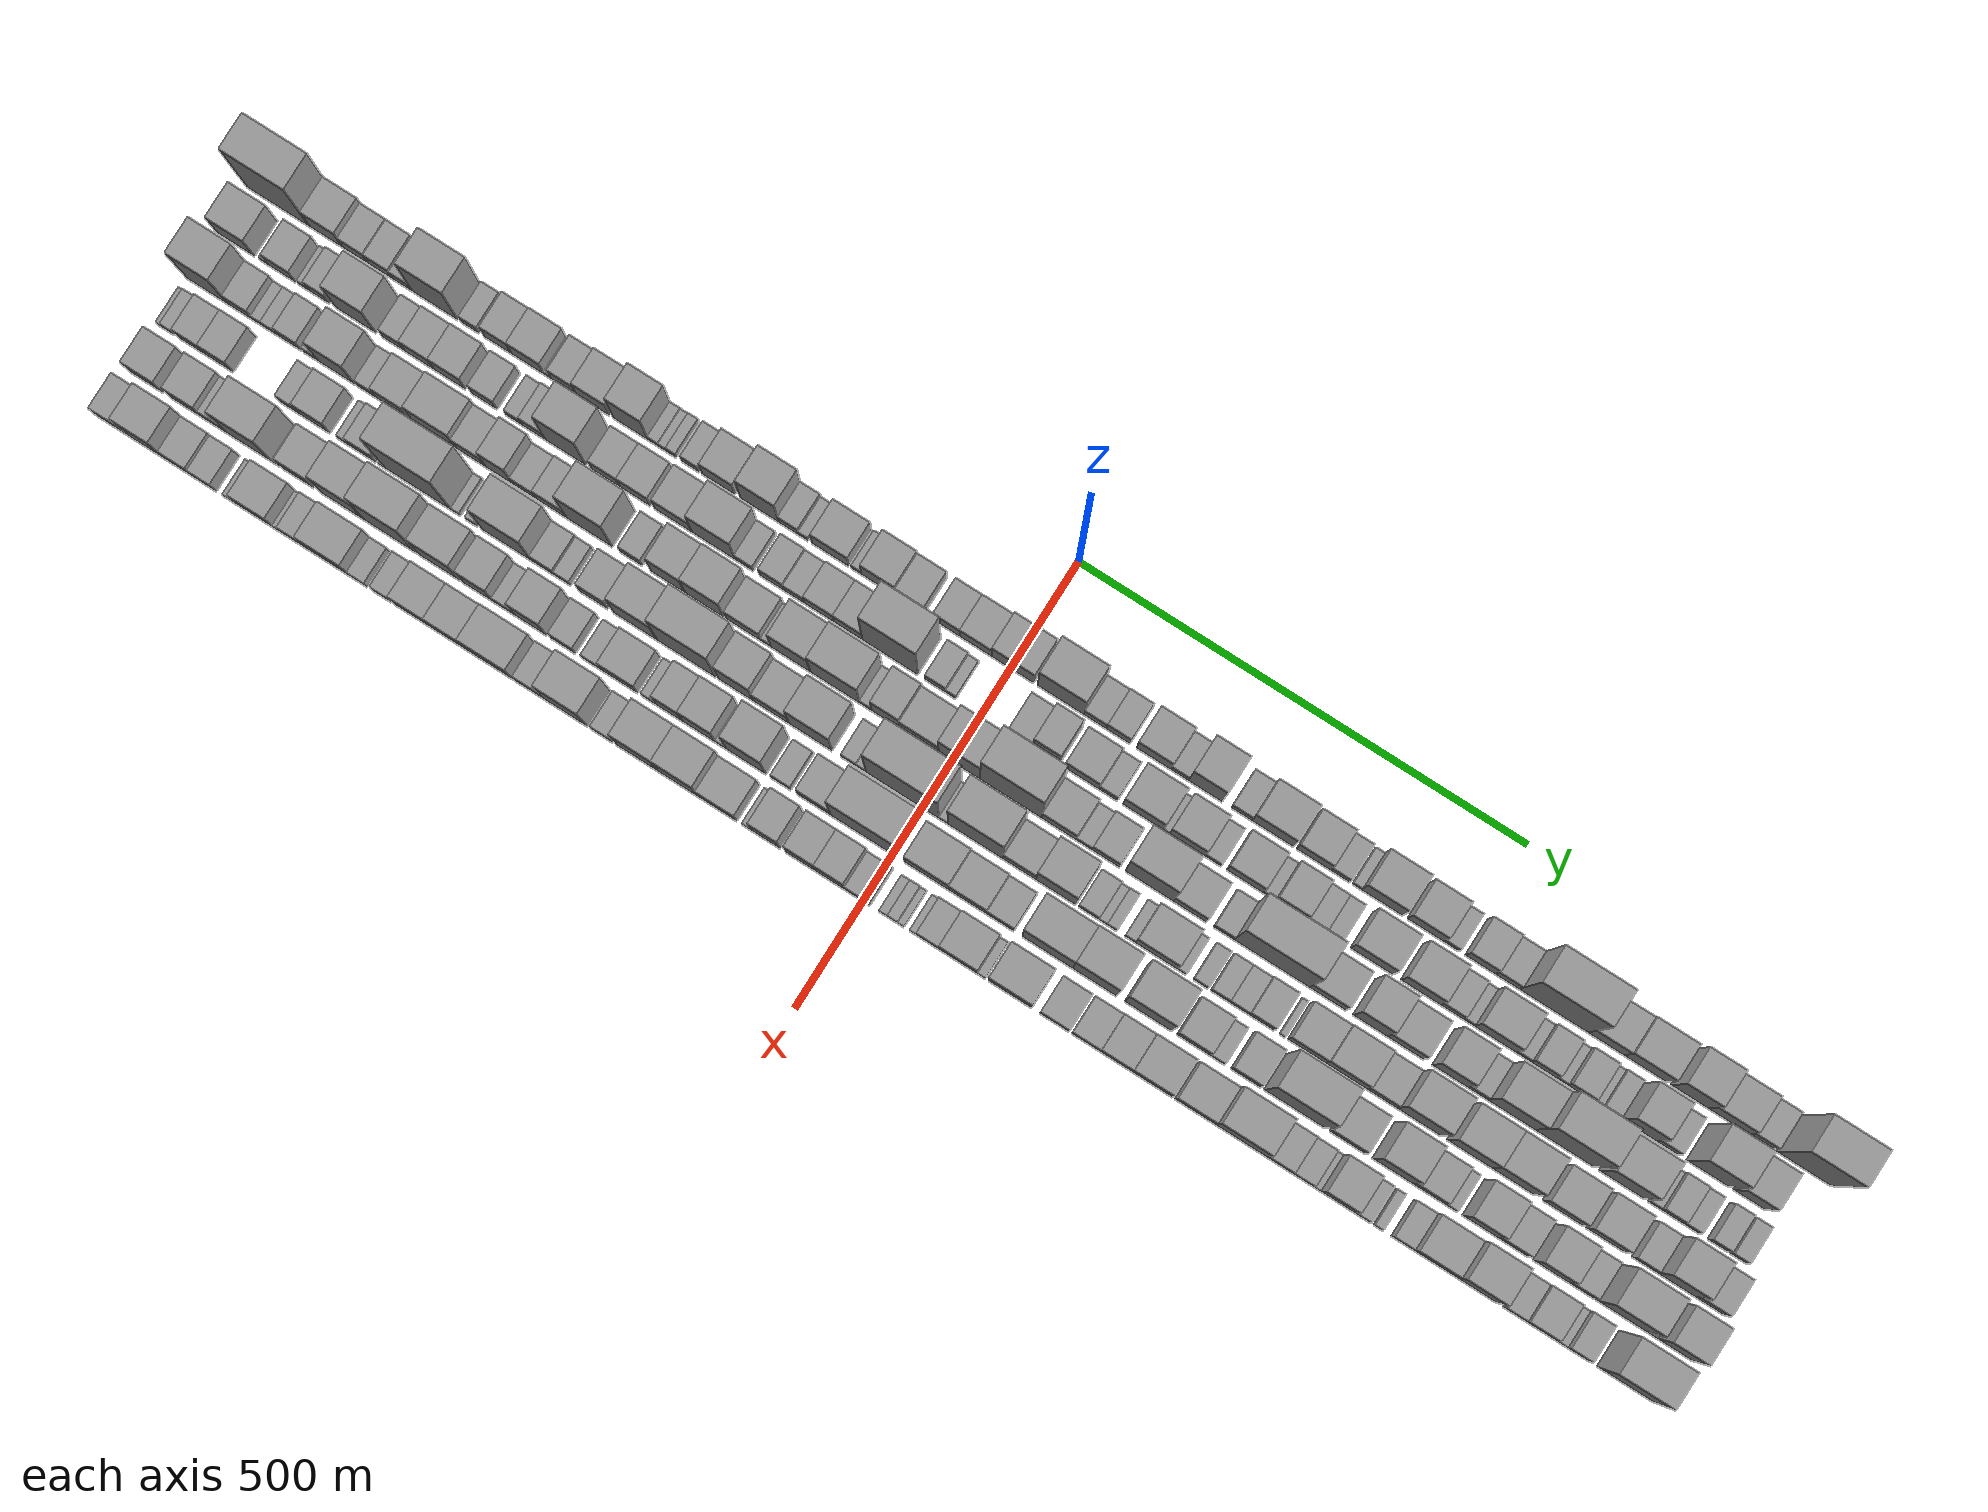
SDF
<sdf version="1.6">
 <world name="default">
  <scene>
   <sky><clouds><speed>12</speed></clouds></sky>
   <ambient>0.4 0.4 0.4 1</ambient>
   <background>0.7 0.7 0.7 1</background>
   <shadows>1</shadows>
  </scene>
  <gravity>0 0 -9.8066</gravity>
  <magnetic_field>6e-06 2.3e-05 -4.2e-05</magnetic_field>
  <physics default="0" name="default_physics" type="ode">
   <ode>
    <solver>
     <type>quick</type>
     <iters>10</iters>
     <sor>1.0</sor>
     <use_dynamic_moi_rescaling>0</use_dynamic_moi_rescaling>
    </solver>
    <constraints>
     <cfm>0</cfm>
     <erp>0.2</erp>
     <contact_max_correcting_vel>100</contact_max_correcting_vel>
     <contact_surface_layer>0.001</contact_surface_layer>
    </constraints>
   </ode>
   <max_step_size>0.004</max_step_size>
   <real_time_factor>1</real_time_factor>
   <real_time_update_rate>250</real_time_update_rate>
  </physics>
  <light name="sun" type="directional">
   <pose>0 0 10 0 0 0</pose>
   <diffuse>0.8 0.8 0.8 1</diffuse>
   <specular>0.2 0.2 0.2 1</specular>
   <attenuation>
    <range>1000</range>
    <constant>0.9</constant>
    <linear>0.01</linear>
    <quadratic>0.001</quadratic>
   </attenuation>
   <direction>-0.5 0.1 -0.9</direction>
  </light>
  <model name="building_1">
   <static>1</static>
   <pose>100.0000 -824.5503 0 0.000000 0.000000 0.000000</pose>
   <link name="link">
    <pose>0 0 91.50 0 0 0</pose>
    <collision name="collision"><geometry><box><size>40.0000 70.8994 183.0000</size></box></geometry></collision>
    <visual name="visual">
     <cast_shadows>0</cast_shadows>
     <geometry><box><size>40.0000 70.8994 183.0000</size></box></geometry>
     <material>
      <script>
       <uri>model://grey_wall/materials/scripts</uri>
       <uri>model://grey_wall/materials/textures</uri>
       <name>vrc/grey_wall</name>
      </script>
     </material>
    </visual>
   </link>
  </model>
  <model name="building_2">
   <static>1</static>
   <pose>100.0000 -770.1328 0 0.000000 0.000000 0.000000</pose>
   <link name="link">
    <pose>0 0 37.50 0 0 0</pose>
    <collision name="collision"><geometry><box><size>40.0000 37.9356 75.0000</size></box></geometry></collision>
    <visual name="visual">
     <cast_shadows>0</cast_shadows>
     <geometry><box><size>40.0000 37.9356 75.0000</size></box></geometry>
     <material>
      <script>
       <uri>model://grey_wall/materials/scripts</uri>
       <uri>model://grey_wall/materials/textures</uri>
       <name>vrc/grey_wall</name>
      </script>
     </material>
    </visual>
   </link>
  </model>
  <model name="building_3">
   <static>1</static>
   <pose>100.0000 -736.9580 0 0.000000 0.000000 0.000000</pose>
   <link name="link">
    <pose>0 0 25.50 0 0 0</pose>
    <collision name="collision"><geometry><box><size>40.0000 28.4142 51.0000</size></box></geometry></collision>
    <visual name="visual">
     <cast_shadows>0</cast_shadows>
     <geometry><box><size>40.0000 28.4142 51.0000</size></box></geometry>
     <material>
      <script>
       <uri>model://grey_wall/materials/scripts</uri>
       <uri>model://grey_wall/materials/textures</uri>
       <name>vrc/grey_wall</name>
      </script>
     </material>
    </visual>
   </link>
  </model>
  <model name="building_4">
   <static>1</static>
   <pose>100.0000 -708.9636 0 0.000000 0.000000 0.000000</pose>
   <link name="link">
    <pose>0 0 24.00 0 0 0</pose>
    <collision name="collision"><geometry><box><size>40.0000 27.5745 48.0000</size></box></geometry></collision>
    <visual name="visual">
     <cast_shadows>0</cast_shadows>
     <geometry><box><size>40.0000 27.5745 48.0000</size></box></geometry>
     <material>
      <script>
       <uri>model://grey_wall/materials/scripts</uri>
       <uri>model://grey_wall/materials/textures</uri>
       <name>vrc/grey_wall</name>
      </script>
     </material>
    </visual>
   </link>
  </model>
  <model name="building_5">
   <static>1</static>
   <pose>100.0000 -684.1588 0 0.000000 0.000000 0.000000</pose>
   <link name="link">
    <pose>0 0 19.50 0 0 0</pose>
    <collision name="collision"><geometry><box><size>40.0000 22.0353 39.0000</size></box></geometry></collision>
    <visual name="visual">
     <cast_shadows>0</cast_shadows>
     <geometry><box><size>40.0000 22.0353 39.0000</size></box></geometry>
     <material>
      <script>
       <uri>model://grey_wall/materials/scripts</uri>
       <uri>model://grey_wall/materials/textures</uri>
       <name>vrc/grey_wall</name>
      </script>
     </material>
    </visual>
   </link>
  </model>
  <model name="building_6">
   <static>1</static>
   <pose>100.0000 -647.2399 0 0.000000 0.000000 0.000000</pose>
   <link name="link">
    <pose>0 0 75.00 0 0 0</pose>
    <collision name="collision"><geometry><box><size>40.0000 51.8024 150.0000</size></box></geometry></collision>
    <visual name="visual">
     <cast_shadows>0</cast_shadows>
     <geometry><box><size>40.0000 51.8024 150.0000</size></box></geometry>
     <material>
      <script>
       <uri>model://grey_wall/materials/scripts</uri>
       <uri>model://grey_wall/materials/textures</uri>
       <name>vrc/grey_wall</name>
      </script>
     </material>
    </visual>
   </link>
  </model>
  <model name="building_7">
   <static>1</static>
   <pose>100.0000 -607.3084 0 0.000000 0.000000 0.000000</pose>
   <link name="link">
    <pose>0 0 18.00 0 0 0</pose>
    <collision name="collision"><geometry><box><size>40.0000 20.0606 36.0000</size></box></geometry></collision>
    <visual name="visual">
     <cast_shadows>0</cast_shadows>
     <geometry><box><size>40.0000 20.0606 36.0000</size></box></geometry>
     <material>
      <script>
       <uri>model://grey_wall/materials/scripts</uri>
       <uri>model://grey_wall/materials/textures</uri>
       <name>vrc/grey_wall</name>
      </script>
     </material>
    </visual>
   </link>
  </model>
  <model name="building_8">
   <static>1</static>
   <pose>100.0000 -576.0887 0 0.000000 0.000000 0.000000</pose>
   <link name="link">
    <pose>0 0 30.00 0 0 0</pose>
    <collision name="collision"><geometry><box><size>40.0000 30.3787 60.0000</size></box></geometry></collision>
    <visual name="visual">
     <cast_shadows>0</cast_shadows>
     <geometry><box><size>40.0000 30.3787 60.0000</size></box></geometry>
     <material>
      <script>
       <uri>model://grey_wall/materials/scripts</uri>
       <uri>model://grey_wall/materials/textures</uri>
       <name>vrc/grey_wall</name>
      </script>
     </material>
    </visual>
   </link>
  </model>
  <model name="building_9">
   <static>1</static>
   <pose>100.0000 -542.3237 0 0.000000 0.000000 0.000000</pose>
   <link name="link">
    <pose>0 0 33.00 0 0 0</pose>
    <collision name="collision"><geometry><box><size>40.0000 37.1513 66.0000</size></box></geometry></collision>
    <visual name="visual">
     <cast_shadows>0</cast_shadows>
     <geometry><box><size>40.0000 37.1513 66.0000</size></box></geometry>
     <material>
      <script>
       <uri>model://grey_wall/materials/scripts</uri>
       <uri>model://grey_wall/materials/textures</uri>
       <name>vrc/grey_wall</name>
      </script>
     </material>
    </visual>
   </link>
  </model>
  <model name="building_10">
   <static>1</static>
   <pose>100.0000 -520.1321 0 0.000000 0.000000 0.000000</pose>
   <link name="link">
    <pose>0 0 9.00 0 0 0</pose>
    <collision name="collision"><geometry><box><size>40.0000 7.2320 18.0000</size></box></geometry></collision>
    <visual name="visual">
     <cast_shadows>0</cast_shadows>
     <geometry><box><size>40.0000 7.2320 18.0000</size></box></geometry>
     <material>
      <script>
       <uri>model://grey_wall/materials/scripts</uri>
       <uri>model://grey_wall/materials/textures</uri>
       <name>vrc/grey_wall</name>
      </script>
     </material>
    </visual>
   </link>
  </model>
  <model name="building_11">
   <static>1</static>
   <pose>100.0000 -502.2497 0 0.000000 0.000000 0.000000</pose>
   <link name="link">
    <pose>0 0 27.00 0 0 0</pose>
    <collision name="collision"><geometry><box><size>40.0000 28.5327 54.0000</size></box></geometry></collision>
    <visual name="visual">
     <cast_shadows>0</cast_shadows>
     <geometry><box><size>40.0000 28.5327 54.0000</size></box></geometry>
     <material>
      <script>
       <uri>model://grey_wall/materials/scripts</uri>
       <uri>model://grey_wall/materials/textures</uri>
       <name>vrc/grey_wall</name>
      </script>
     </material>
    </visual>
   </link>
  </model>
  <model name="building_12">
   <static>1</static>
   <pose>100.0000 -469.1289 0 0.000000 0.000000 0.000000</pose>
   <link name="link">
    <pose>0 0 36.00 0 0 0</pose>
    <collision name="collision"><geometry><box><size>40.0000 37.7090 72.0000</size></box></geometry></collision>
    <visual name="visual">
     <cast_shadows>0</cast_shadows>
     <geometry><box><size>40.0000 37.7090 72.0000</size></box></geometry>
     <material>
      <script>
       <uri>model://grey_wall/materials/scripts</uri>
       <uri>model://grey_wall/materials/textures</uri>
       <name>vrc/grey_wall</name>
      </script>
     </material>
    </visual>
   </link>
  </model>
  <model name="building_13">
   <static>1</static>
   <pose>100.0000 -426.5870 0 0.000000 0.000000 0.000000</pose>
   <link name="link">
    <pose>0 0 61.50 0 0 0</pose>
    <collision name="collision"><geometry><box><size>40.0000 39.3748 123.0000</size></box></geometry></collision>
    <visual name="visual">
     <cast_shadows>0</cast_shadows>
     <geometry><box><size>40.0000 39.3748 123.0000</size></box></geometry>
     <material>
      <script>
       <uri>model://grey_wall/materials/scripts</uri>
       <uri>model://grey_wall/materials/textures</uri>
       <name>vrc/grey_wall</name>
      </script>
     </material>
    </visual>
   </link>
  </model>
  <model name="building_14">
   <static>1</static>
   <pose>100.0000 -401.0186 0 0.000000 0.000000 0.000000</pose>
   <link name="link">
    <pose>0 0 12.00 0 0 0</pose>
    <collision name="collision"><geometry><box><size>40.0000 11.7619 24.0000</size></box></geometry></collision>
    <visual name="visual">
     <cast_shadows>0</cast_shadows>
     <geometry><box><size>40.0000 11.7619 24.0000</size></box></geometry>
     <material>
      <script>
       <uri>model://grey_wall/materials/scripts</uri>
       <uri>model://grey_wall/materials/textures</uri>
       <name>vrc/grey_wall</name>
      </script>
     </material>
    </visual>
   </link>
  </model>
  <model name="building_15">
   <static>1</static>
   <pose>100.0000 -390.6701 0 0.000000 0.000000 0.000000</pose>
   <link name="link">
    <pose>0 0 10.50 0 0 0</pose>
    <collision name="collision"><geometry><box><size>40.0000 8.9351 21.0000</size></box></geometry></collision>
    <visual name="visual">
     <cast_shadows>0</cast_shadows>
     <geometry><box><size>40.0000 8.9351 21.0000</size></box></geometry>
     <material>
      <script>
       <uri>model://grey_wall/materials/scripts</uri>
       <uri>model://grey_wall/materials/textures</uri>
       <name>vrc/grey_wall</name>
      </script>
     </material>
    </visual>
   </link>
  </model>
  <model name="building_16">
   <static>1</static>
   <pose>100.0000 -380.6885 0 0.000000 0.000000 0.000000</pose>
   <link name="link">
    <pose>0 0 13.50 0 0 0</pose>
    <collision name="collision"><geometry><box><size>40.0000 11.0281 27.0000</size></box></geometry></collision>
    <visual name="visual">
     <cast_shadows>0</cast_shadows>
     <geometry><box><size>40.0000 11.0281 27.0000</size></box></geometry>
     <material>
      <script>
       <uri>model://grey_wall/materials/scripts</uri>
       <uri>model://grey_wall/materials/textures</uri>
       <name>vrc/grey_wall</name>
      </script>
     </material>
    </visual>
   </link>
  </model>
  <model name="building_17">
   <static>1</static>
   <pose>100.0000 -359.2277 0 0.000000 0.000000 0.000000</pose>
   <link name="link">
    <pose>0 0 18.00 0 0 0</pose>
    <collision name="collision"><geometry><box><size>40.0000 19.8936 36.0000</size></box></geometry></collision>
    <visual name="visual">
     <cast_shadows>0</cast_shadows>
     <geometry><box><size>40.0000 19.8936 36.0000</size></box></geometry>
     <material>
      <script>
       <uri>model://grey_wall/materials/scripts</uri>
       <uri>model://grey_wall/materials/textures</uri>
       <name>vrc/grey_wall</name>
      </script>
     </material>
    </visual>
   </link>
  </model>
  <model name="building_18">
   <static>1</static>
   <pose>100.0000 -327.8683 0 0.000000 0.000000 0.000000</pose>
   <link name="link">
    <pose>0 0 36.00 0 0 0</pose>
    <collision name="collision"><geometry><box><size>40.0000 36.8251 72.0000</size></box></geometry></collision>
    <visual name="visual">
     <cast_shadows>0</cast_shadows>
     <geometry><box><size>40.0000 36.8251 72.0000</size></box></geometry>
     <material>
      <script>
       <uri>model://grey_wall/materials/scripts</uri>
       <uri>model://grey_wall/materials/textures</uri>
       <name>vrc/grey_wall</name>
      </script>
     </material>
    </visual>
   </link>
  </model>
  <model name="building_19">
   <static>1</static>
   <pose>100.0000 -281.9354 0 0.000000 0.000000 0.000000</pose>
   <link name="link">
    <pose>0 0 61.50 0 0 0</pose>
    <collision name="collision"><geometry><box><size>40.0000 43.0408 123.0000</size></box></geometry></collision>
    <visual name="visual">
     <cast_shadows>0</cast_shadows>
     <geometry><box><size>40.0000 43.0408 123.0000</size></box></geometry>
     <material>
      <script>
       <uri>model://grey_wall/materials/scripts</uri>
       <uri>model://grey_wall/materials/textures</uri>
       <name>vrc/grey_wall</name>
      </script>
     </material>
    </visual>
   </link>
  </model>
  <model name="building_20">
   <static>1</static>
   <pose>100.0000 -249.3155 0 0.000000 0.000000 0.000000</pose>
   <link name="link">
    <pose>0 0 21.00 0 0 0</pose>
    <collision name="collision"><geometry><box><size>40.0000 22.1990 42.0000</size></box></geometry></collision>
    <visual name="visual">
     <cast_shadows>0</cast_shadows>
     <geometry><box><size>40.0000 22.1990 42.0000</size></box></geometry>
     <material>
      <script>
       <uri>model://grey_wall/materials/scripts</uri>
       <uri>model://grey_wall/materials/textures</uri>
       <name>vrc/grey_wall</name>
      </script>
     </material>
    </visual>
   </link>
  </model>
  <model name="building_21">
   <static>1</static>
   <pose>100.0000 -232.7131 0 0.000000 0.000000 0.000000</pose>
   <link name="link">
    <pose>0 0 12.00 0 0 0</pose>
    <collision name="collision"><geometry><box><size>40.0000 11.0057 24.0000</size></box></geometry></collision>
    <visual name="visual">
     <cast_shadows>0</cast_shadows>
     <geometry><box><size>40.0000 11.0057 24.0000</size></box></geometry>
     <material>
      <script>
       <uri>model://grey_wall/materials/scripts</uri>
       <uri>model://grey_wall/materials/textures</uri>
       <name>vrc/grey_wall</name>
      </script>
     </material>
    </visual>
   </link>
  </model>
  <model name="building_22">
   <static>1</static>
   <pose>100.0000 -202.5432 0 0.000000 0.000000 0.000000</pose>
   <link name="link">
    <pose>0 0 34.50 0 0 0</pose>
    <collision name="collision"><geometry><box><size>40.0000 41.3342 69.0000</size></box></geometry></collision>
    <visual name="visual">
     <cast_shadows>0</cast_shadows>
     <geometry><box><size>40.0000 41.3342 69.0000</size></box></geometry>
     <material>
      <script>
       <uri>model://grey_wall/materials/scripts</uri>
       <uri>model://grey_wall/materials/textures</uri>
       <name>vrc/grey_wall</name>
      </script>
     </material>
    </visual>
   </link>
  </model>
  <model name="building_23">
   <static>1</static>
   <pose>100.0000 -173.4580 0 0.000000 0.000000 0.000000</pose>
   <link name="link">
    <pose>0 0 12.00 0 0 0</pose>
    <collision name="collision"><geometry><box><size>40.0000 10.8361 24.0000</size></box></geometry></collision>
    <visual name="visual">
     <cast_shadows>0</cast_shadows>
     <geometry><box><size>40.0000 10.8361 24.0000</size></box></geometry>
     <material>
      <script>
       <uri>model://grey_wall/materials/scripts</uri>
       <uri>model://grey_wall/materials/textures</uri>
       <name>vrc/grey_wall</name>
      </script>
     </material>
    </visual>
   </link>
  </model>
  <model name="building_24">
   <static>1</static>
   <pose>100.0000 -148.9621 0 0.000000 0.000000 0.000000</pose>
   <link name="link">
    <pose>0 0 37.50 0 0 0</pose>
    <collision name="collision"><geometry><box><size>40.0000 38.1556 75.0000</size></box></geometry></collision>
    <visual name="visual">
     <cast_shadows>0</cast_shadows>
     <geometry><box><size>40.0000 38.1556 75.0000</size></box></geometry>
     <material>
      <script>
       <uri>model://grey_wall/materials/scripts</uri>
       <uri>model://grey_wall/materials/textures</uri>
       <name>vrc/grey_wall</name>
      </script>
     </material>
    </visual>
   </link>
  </model>
  <model name="building_25">
   <static>1</static>
   <pose>100.0000 -113.6556 0 0.000000 0.000000 0.000000</pose>
   <link name="link">
    <pose>0 0 30.00 0 0 0</pose>
    <collision name="collision"><geometry><box><size>40.0000 32.4574 60.0000</size></box></geometry></collision>
    <visual name="visual">
     <cast_shadows>0</cast_shadows>
     <geometry><box><size>40.0000 32.4574 60.0000</size></box></geometry>
     <material>
      <script>
       <uri>model://grey_wall/materials/scripts</uri>
       <uri>model://grey_wall/materials/textures</uri>
       <name>vrc/grey_wall</name>
      </script>
     </material>
    </visual>
   </link>
  </model>
  <model name="building_26">
   <static>1</static>
   <pose>100.0000 -72.6445 0 0.000000 0.000000 0.000000</pose>
   <link name="link">
    <pose>0 0 28.50 0 0 0</pose>
    <collision name="collision"><geometry><box><size>40.0000 29.5649 57.0000</size></box></geometry></collision>
    <visual name="visual">
     <cast_shadows>0</cast_shadows>
     <geometry><box><size>40.0000 29.5649 57.0000</size></box></geometry>
     <material>
      <script>
       <uri>model://grey_wall/materials/scripts</uri>
       <uri>model://grey_wall/materials/textures</uri>
       <name>vrc/grey_wall</name>
      </script>
     </material>
    </visual>
   </link>
  </model>
  <model name="building_27">
   <static>1</static>
   <pose>100.0000 -40.1027 0 0.000000 0.000000 0.000000</pose>
   <link name="link">
    <pose>0 0 30.00 0 0 0</pose>
    <collision name="collision"><geometry><box><size>40.0000 35.5187 60.0000</size></box></geometry></collision>
    <visual name="visual">
     <cast_shadows>0</cast_shadows>
     <geometry><box><size>40.0000 35.5187 60.0000</size></box></geometry>
     <material>
      <script>
       <uri>model://grey_wall/materials/scripts</uri>
       <uri>model://grey_wall/materials/textures</uri>
       <name>vrc/grey_wall</name>
      </script>
     </material>
    </visual>
   </link>
  </model>
  <model name="building_28">
   <static>1</static>
   <pose>100.0000 1.4108 0 0.000000 0.000000 0.000000</pose>
   <link name="link">
    <pose>0 0 40.50 0 0 0</pose>
    <collision name="collision"><geometry><box><size>40.0000 47.5083 81.0000</size></box></geometry></collision>
    <visual name="visual">
     <cast_shadows>0</cast_shadows>
     <geometry><box><size>40.0000 47.5083 81.0000</size></box></geometry>
     <material>
      <script>
       <uri>model://grey_wall/materials/scripts</uri>
       <uri>model://grey_wall/materials/textures</uri>
       <name>vrc/grey_wall</name>
      </script>
     </material>
    </visual>
   </link>
  </model>
  <model name="building_29">
   <static>1</static>
   <pose>100.0000 55.0728 0 0.000000 0.000000 0.000000</pose>
   <link name="link">
    <pose>0 0 66.00 0 0 0</pose>
    <collision name="collision"><geometry><box><size>40.0000 51.8157 132.0000</size></box></geometry></collision>
    <visual name="visual">
     <cast_shadows>0</cast_shadows>
     <geometry><box><size>40.0000 51.8157 132.0000</size></box></geometry>
     <material>
      <script>
       <uri>model://grey_wall/materials/scripts</uri>
       <uri>model://grey_wall/materials/textures</uri>
       <name>vrc/grey_wall</name>
      </script>
     </material>
    </visual>
   </link>
  </model>
  <model name="building_30">
   <static>1</static>
   <pose>100.0000 93.5002 0 0.000000 0.000000 0.000000</pose>
   <link name="link">
    <pose>0 0 22.50 0 0 0</pose>
    <collision name="collision"><geometry><box><size>40.0000 25.0390 45.0000</size></box></geometry></collision>
    <visual name="visual">
     <cast_shadows>0</cast_shadows>
     <geometry><box><size>40.0000 25.0390 45.0000</size></box></geometry>
     <material>
      <script>
       <uri>model://grey_wall/materials/scripts</uri>
       <uri>model://grey_wall/materials/textures</uri>
       <name>vrc/grey_wall</name>
      </script>
     </material>
    </visual>
   </link>
  </model>
  <model name="building_31">
   <static>1</static>
   <pose>100.0000 119.2710 0 0.000000 0.000000 0.000000</pose>
   <link name="link">
    <pose>0 0 25.50 0 0 0</pose>
    <collision name="collision"><geometry><box><size>40.0000 26.5027 51.0000</size></box></geometry></collision>
    <visual name="visual">
     <cast_shadows>0</cast_shadows>
     <geometry><box><size>40.0000 26.5027 51.0000</size></box></geometry>
     <material>
      <script>
       <uri>model://grey_wall/materials/scripts</uri>
       <uri>model://grey_wall/materials/textures</uri>
       <name>vrc/grey_wall</name>
      </script>
     </material>
    </visual>
   </link>
  </model>
  <model name="building_32">
   <static>1</static>
   <pose>100.0000 158.8152 0 0.000000 0.000000 0.000000</pose>
   <link name="link">
    <pose>0 0 36.00 0 0 0</pose>
    <collision name="collision"><geometry><box><size>40.0000 38.5856 72.0000</size></box></geometry></collision>
    <visual name="visual">
     <cast_shadows>0</cast_shadows>
     <geometry><box><size>40.0000 38.5856 72.0000</size></box></geometry>
     <material>
      <script>
       <uri>model://grey_wall/materials/scripts</uri>
       <uri>model://grey_wall/materials/textures</uri>
       <name>vrc/grey_wall</name>
      </script>
     </material>
    </visual>
   </link>
  </model>
  <model name="building_33">
   <static>1</static>
   <pose>100.0000 187.8211 0 0.000000 0.000000 0.000000</pose>
   <link name="link">
    <pose>0 0 18.00 0 0 0</pose>
    <collision name="collision"><geometry><box><size>40.0000 19.4261 36.0000</size></box></geometry></collision>
    <visual name="visual">
     <cast_shadows>0</cast_shadows>
     <geometry><box><size>40.0000 19.4261 36.0000</size></box></geometry>
     <material>
      <script>
       <uri>model://grey_wall/materials/scripts</uri>
       <uri>model://grey_wall/materials/textures</uri>
       <name>vrc/grey_wall</name>
      </script>
     </material>
    </visual>
   </link>
  </model>
  <model name="building_34">
   <static>1</static>
   <pose>100.0000 216.2699 0 0.000000 0.000000 0.000000</pose>
   <link name="link">
    <pose>0 0 60.00 0 0 0</pose>
    <collision name="collision"><geometry><box><size>40.0000 37.4716 120.0000</size></box></geometry></collision>
    <visual name="visual">
     <cast_shadows>0</cast_shadows>
     <geometry><box><size>40.0000 37.4716 120.0000</size></box></geometry>
     <material>
      <script>
       <uri>model://grey_wall/materials/scripts</uri>
       <uri>model://grey_wall/materials/textures</uri>
       <name>vrc/grey_wall</name>
      </script>
     </material>
    </visual>
   </link>
  </model>
  <model name="building_35">
   <static>1</static>
   <pose>100.0000 256.4947 0 0.000000 0.000000 0.000000</pose>
   <link name="link">
    <pose>0 0 19.50 0 0 0</pose>
    <collision name="collision"><geometry><box><size>40.0000 22.9780 39.0000</size></box></geometry></collision>
    <visual name="visual">
     <cast_shadows>0</cast_shadows>
     <geometry><box><size>40.0000 22.9780 39.0000</size></box></geometry>
     <material>
      <script>
       <uri>model://grey_wall/materials/scripts</uri>
       <uri>model://grey_wall/materials/textures</uri>
       <name>vrc/grey_wall</name>
      </script>
     </material>
    </visual>
   </link>
  </model>
  <model name="building_36">
   <static>1</static>
   <pose>100.0000 291.1873 0 0.000000 0.000000 0.000000</pose>
   <link name="link">
    <pose>0 0 42.00 0 0 0</pose>
    <collision name="collision"><geometry><box><size>40.0000 46.4072 84.0000</size></box></geometry></collision>
    <visual name="visual">
     <cast_shadows>0</cast_shadows>
     <geometry><box><size>40.0000 46.4072 84.0000</size></box></geometry>
     <material>
      <script>
       <uri>model://grey_wall/materials/scripts</uri>
       <uri>model://grey_wall/materials/textures</uri>
       <name>vrc/grey_wall</name>
      </script>
     </material>
    </visual>
   </link>
  </model>
  <model name="building_37">
   <static>1</static>
   <pose>100.0000 336.2327 0 0.000000 0.000000 0.000000</pose>
   <link name="link">
    <pose>0 0 33.00 0 0 0</pose>
    <collision name="collision"><geometry><box><size>40.0000 37.6837 66.0000</size></box></geometry></collision>
    <visual name="visual">
     <cast_shadows>0</cast_shadows>
     <geometry><box><size>40.0000 37.6837 66.0000</size></box></geometry>
     <material>
      <script>
       <uri>model://grey_wall/materials/scripts</uri>
       <uri>model://grey_wall/materials/textures</uri>
       <name>vrc/grey_wall</name>
      </script>
     </material>
    </visual>
   </link>
  </model>
  <model name="building_38">
   <static>1</static>
   <pose>100.0000 365.7849 0 0.000000 0.000000 0.000000</pose>
   <link name="link">
    <pose>0 0 18.00 0 0 0</pose>
    <collision name="collision"><geometry><box><size>40.0000 21.4206 36.0000</size></box></geometry></collision>
    <visual name="visual">
     <cast_shadows>0</cast_shadows>
     <geometry><box><size>40.0000 21.4206 36.0000</size></box></geometry>
     <material>
      <script>
       <uri>model://grey_wall/materials/scripts</uri>
       <uri>model://grey_wall/materials/textures</uri>
       <name>vrc/grey_wall</name>
      </script>
     </material>
    </visual>
   </link>
  </model>
  <model name="building_39">
   <static>1</static>
   <pose>100.0000 384.5352 0 0.000000 0.000000 0.000000</pose>
   <link name="link">
    <pose>0 0 10.50 0 0 0</pose>
    <collision name="collision"><geometry><box><size>40.0000 10.0801 21.0000</size></box></geometry></collision>
    <visual name="visual">
     <cast_shadows>0</cast_shadows>
     <geometry><box><size>40.0000 10.0801 21.0000</size></box></geometry>
     <material>
      <script>
       <uri>model://grey_wall/materials/scripts</uri>
       <uri>model://grey_wall/materials/textures</uri>
       <name>vrc/grey_wall</name>
      </script>
     </material>
    </visual>
   </link>
  </model>
  <model name="building_40">
   <static>1</static>
   <pose>100.0000 412.4168 0 0.000000 0.000000 0.000000</pose>
   <link name="link">
    <pose>0 0 43.50 0 0 0</pose>
    <collision name="collision"><geometry><box><size>40.0000 45.6829 87.0000</size></box></geometry></collision>
    <visual name="visual">
     <cast_shadows>0</cast_shadows>
     <geometry><box><size>40.0000 45.6829 87.0000</size></box></geometry>
     <material>
      <script>
       <uri>model://grey_wall/materials/scripts</uri>
       <uri>model://grey_wall/materials/textures</uri>
       <name>vrc/grey_wall</name>
      </script>
     </material>
    </visual>
   </link>
  </model>
  <model name="building_41">
   <static>1</static>
   <pose>100.0000 460.4305 0 0.000000 0.000000 0.000000</pose>
   <link name="link">
    <pose>0 0 36.00 0 0 0</pose>
    <collision name="collision"><geometry><box><size>40.0000 40.3446 72.0000</size></box></geometry></collision>
    <visual name="visual">
     <cast_shadows>0</cast_shadows>
     <geometry><box><size>40.0000 40.3446 72.0000</size></box></geometry>
     <material>
      <script>
       <uri>model://grey_wall/materials/scripts</uri>
       <uri>model://grey_wall/materials/textures</uri>
       <name>vrc/grey_wall</name>
      </script>
     </material>
    </visual>
   </link>
  </model>
  <model name="building_42">
   <static>1</static>
   <pose>100.0000 489.0074 0 0.000000 0.000000 0.000000</pose>
   <link name="link">
    <pose>0 0 15.00 0 0 0</pose>
    <collision name="collision"><geometry><box><size>40.0000 16.8091 30.0000</size></box></geometry></collision>
    <visual name="visual">
     <cast_shadows>0</cast_shadows>
     <geometry><box><size>40.0000 16.8091 30.0000</size></box></geometry>
     <material>
      <script>
       <uri>model://grey_wall/materials/scripts</uri>
       <uri>model://grey_wall/materials/textures</uri>
       <name>vrc/grey_wall</name>
      </script>
     </material>
    </visual>
   </link>
  </model>
  <model name="building_43">
   <static>1</static>
   <pose>100.0000 520.6841 0 0.000000 0.000000 0.000000</pose>
   <link name="link">
    <pose>0 0 31.50 0 0 0</pose>
    <collision name="collision"><geometry><box><size>40.0000 32.5442 63.0000</size></box></geometry></collision>
    <visual name="visual">
     <cast_shadows>0</cast_shadows>
     <geometry><box><size>40.0000 32.5442 63.0000</size></box></geometry>
     <material>
      <script>
       <uri>model://grey_wall/materials/scripts</uri>
       <uri>model://grey_wall/materials/textures</uri>
       <name>vrc/grey_wall</name>
      </script>
     </material>
    </visual>
   </link>
  </model>
  <model name="building_44">
   <static>1</static>
   <pose>100.0000 550.2050 0 0.000000 0.000000 0.000000</pose>
   <link name="link">
    <pose>0 0 24.00 0 0 0</pose>
    <collision name="collision"><geometry><box><size>40.0000 26.4977 48.0000</size></box></geometry></collision>
    <visual name="visual">
     <cast_shadows>0</cast_shadows>
     <geometry><box><size>40.0000 26.4977 48.0000</size></box></geometry>
     <material>
      <script>
       <uri>model://grey_wall/materials/scripts</uri>
       <uri>model://grey_wall/materials/textures</uri>
       <name>vrc/grey_wall</name>
      </script>
     </material>
    </visual>
   </link>
  </model>
  <model name="building_45">
   <static>1</static>
   <pose>100.0000 601.4771 0 0.000000 0.000000 0.000000</pose>
   <link name="link">
    <pose>0 0 99.00 0 0 0</pose>
    <collision name="collision"><geometry><box><size>40.0000 76.0464 198.0000</size></box></geometry></collision>
    <visual name="visual">
     <cast_shadows>0</cast_shadows>
     <geometry><box><size>40.0000 76.0464 198.0000</size></box></geometry>
     <material>
      <script>
       <uri>model://grey_wall/materials/scripts</uri>
       <uri>model://grey_wall/materials/textures</uri>
       <name>vrc/grey_wall</name>
      </script>
     </material>
    </visual>
   </link>
  </model>
  <model name="building_46">
   <static>1</static>
   <pose>100.0000 659.3488 0 0.000000 0.000000 0.000000</pose>
   <link name="link">
    <pose>0 0 37.50 0 0 0</pose>
    <collision name="collision"><geometry><box><size>40.0000 39.6969 75.0000</size></box></geometry></collision>
    <visual name="visual">
     <cast_shadows>0</cast_shadows>
     <geometry><box><size>40.0000 39.6969 75.0000</size></box></geometry>
     <material>
      <script>
       <uri>model://grey_wall/materials/scripts</uri>
       <uri>model://grey_wall/materials/textures</uri>
       <name>vrc/grey_wall</name>
      </script>
     </material>
    </visual>
   </link>
  </model>
  <model name="building_47">
   <static>1</static>
   <pose>100.0000 702.9278 0 0.000000 0.000000 0.000000</pose>
   <link name="link">
    <pose>0 0 42.00 0 0 0</pose>
    <collision name="collision"><geometry><box><size>40.0000 47.4612 84.0000</size></box></geometry></collision>
    <visual name="visual">
     <cast_shadows>0</cast_shadows>
     <geometry><box><size>40.0000 47.4612 84.0000</size></box></geometry>
     <material>
      <script>
       <uri>model://grey_wall/materials/scripts</uri>
       <uri>model://grey_wall/materials/textures</uri>
       <name>vrc/grey_wall</name>
      </script>
     </material>
    </visual>
   </link>
  </model>
  <model name="building_48">
   <static>1</static>
   <pose>100.0000 751.9403 0 0.000000 0.000000 0.000000</pose>
   <link name="link">
    <pose>0 0 55.50 0 0 0</pose>
    <collision name="collision"><geometry><box><size>40.0000 40.5638 111.0000</size></box></geometry></collision>
    <visual name="visual">
     <cast_shadows>0</cast_shadows>
     <geometry><box><size>40.0000 40.5638 111.0000</size></box></geometry>
     <material>
      <script>
       <uri>model://grey_wall/materials/scripts</uri>
       <uri>model://grey_wall/materials/textures</uri>
       <name>vrc/grey_wall</name>
      </script>
     </material>
    </visual>
   </link>
  </model>
  <model name="building_49">
   <static>1</static>
   <pose>100.0000 794.2953 0 0.000000 0.000000 0.000000</pose>
   <link name="link">
    <pose>0 0 37.50 0 0 0</pose>
    <collision name="collision"><geometry><box><size>40.0000 44.1461 75.0000</size></box></geometry></collision>
    <visual name="visual">
     <cast_shadows>0</cast_shadows>
     <geometry><box><size>40.0000 44.1461 75.0000</size></box></geometry>
     <material>
      <script>
       <uri>model://grey_wall/materials/scripts</uri>
       <uri>model://grey_wall/materials/textures</uri>
       <name>vrc/grey_wall</name>
      </script>
     </material>
    </visual>
   </link>
  </model>
  <model name="building_50">
   <static>1</static>
   <pose>100.0000 829.9106 0 0.000000 0.000000 0.000000</pose>
   <link name="link">
    <pose>0 0 25.50 0 0 0</pose>
    <collision name="collision"><geometry><box><size>40.0000 27.0845 51.0000</size></box></geometry></collision>
    <visual name="visual">
     <cast_shadows>0</cast_shadows>
     <geometry><box><size>40.0000 27.0845 51.0000</size></box></geometry>
     <material>
      <script>
       <uri>model://grey_wall/materials/scripts</uri>
       <uri>model://grey_wall/materials/textures</uri>
       <name>vrc/grey_wall</name>
      </script>
     </material>
    </visual>
   </link>
  </model>
  <model name="building_51">
   <static>1</static>
   <pose>100.0000 877.7464 0 0.000000 0.000000 0.000000</pose>
   <link name="link">
    <pose>0 0 99.00 0 0 0</pose>
    <collision name="collision"><geometry><box><size>40.0000 60.5870 198.0000</size></box></geometry></collision>
    <visual name="visual">
     <cast_shadows>0</cast_shadows>
     <geometry><box><size>40.0000 60.5870 198.0000</size></box></geometry>
     <material>
      <script>
       <uri>model://grey_wall/materials/scripts</uri>
       <uri>model://grey_wall/materials/textures</uri>
       <name>vrc/grey_wall</name>
      </script>
     </material>
    </visual>
   </link>
  </model>
  <model name="building_52">
   <static>1</static>
   <pose>152.0000 -838.8743 0 0.000000 0.000000 0.000000</pose>
   <link name="link">
    <pose>0 0 40.50 0 0 0</pose>
    <collision name="collision"><geometry><box><size>40.0000 42.2515 81.0000</size></box></geometry></collision>
    <visual name="visual">
     <cast_shadows>0</cast_shadows>
     <geometry><box><size>40.0000 42.2515 81.0000</size></box></geometry>
     <material>
      <script>
       <uri>model://grey_wall/materials/scripts</uri>
       <uri>model://grey_wall/materials/textures</uri>
       <name>vrc/grey_wall</name>
      </script>
     </material>
    </visual>
   </link>
  </model>
  <model name="building_53">
   <static>1</static>
   <pose>152.0000 -806.5218 0 0.000000 0.000000 0.000000</pose>
   <link name="link">
    <pose>0 0 9.00 0 0 0</pose>
    <collision name="collision"><geometry><box><size>40.0000 8.4535 18.0000</size></box></geometry></collision>
    <visual name="visual">
     <cast_shadows>0</cast_shadows>
     <geometry><box><size>40.0000 8.4535 18.0000</size></box></geometry>
     <material>
      <script>
       <uri>model://grey_wall/materials/scripts</uri>
       <uri>model://grey_wall/materials/textures</uri>
       <name>vrc/grey_wall</name>
      </script>
     </material>
    </visual>
   </link>
  </model>
  <model name="building_54">
   <static>1</static>
   <pose>152.0000 -786.6653 0 0.000000 0.000000 0.000000</pose>
   <link name="link">
    <pose>0 0 28.50 0 0 0</pose>
    <collision name="collision"><geometry><box><size>40.0000 31.2594 57.0000</size></box></geometry></collision>
    <visual name="visual">
     <cast_shadows>0</cast_shadows>
     <geometry><box><size>40.0000 31.2594 57.0000</size></box></geometry>
     <material>
      <script>
       <uri>model://grey_wall/materials/scripts</uri>
       <uri>model://grey_wall/materials/textures</uri>
       <name>vrc/grey_wall</name>
      </script>
     </material>
    </visual>
   </link>
  </model>
  <model name="building_55">
   <static>1</static>
   <pose>152.0000 -761.8692 0 0.000000 0.000000 0.000000</pose>
   <link name="link">
    <pose>0 0 12.00 0 0 0</pose>
    <collision name="collision"><geometry><box><size>40.0000 10.3329 24.0000</size></box></geometry></collision>
    <visual name="visual">
     <cast_shadows>0</cast_shadows>
     <geometry><box><size>40.0000 10.3329 24.0000</size></box></geometry>
     <material>
      <script>
       <uri>model://grey_wall/materials/scripts</uri>
       <uri>model://grey_wall/materials/textures</uri>
       <name>vrc/grey_wall</name>
      </script>
     </material>
    </visual>
   </link>
  </model>
  <model name="building_56">
   <static>1</static>
   <pose>152.0000 -744.6874 0 0.000000 0.000000 0.000000</pose>
   <link name="link">
    <pose>0 0 24.00 0 0 0</pose>
    <collision name="collision"><geometry><box><size>40.0000 24.0308 48.0000</size></box></geometry></collision>
    <visual name="visual">
     <cast_shadows>0</cast_shadows>
     <geometry><box><size>40.0000 24.0308 48.0000</size></box></geometry>
     <material>
      <script>
       <uri>model://grey_wall/materials/scripts</uri>
       <uri>model://grey_wall/materials/textures</uri>
       <name>vrc/grey_wall</name>
      </script>
     </material>
    </visual>
   </link>
  </model>
  <model name="building_57">
   <static>1</static>
   <pose>152.0000 -702.9129 0 0.000000 0.000000 0.000000</pose>
   <link name="link">
    <pose>0 0 60.00 0 0 0</pose>
    <collision name="collision"><geometry><box><size>40.0000 45.5181 120.0000</size></box></geometry></collision>
    <visual name="visual">
     <cast_shadows>0</cast_shadows>
     <geometry><box><size>40.0000 45.5181 120.0000</size></box></geometry>
     <material>
      <script>
       <uri>model://grey_wall/materials/scripts</uri>
       <uri>model://grey_wall/materials/textures</uri>
       <name>vrc/grey_wall</name>
      </script>
     </material>
    </visual>
   </link>
  </model>
  <model name="building_58">
   <static>1</static>
   <pose>152.0000 -660.0208 0 0.000000 0.000000 0.000000</pose>
   <link name="link">
    <pose>0 0 24.00 0 0 0</pose>
    <collision name="collision"><geometry><box><size>40.0000 24.2662 48.0000</size></box></geometry></collision>
    <visual name="visual">
     <cast_shadows>0</cast_shadows>
     <geometry><box><size>40.0000 24.2662 48.0000</size></box></geometry>
     <material>
      <script>
       <uri>model://grey_wall/materials/scripts</uri>
       <uri>model://grey_wall/materials/textures</uri>
       <name>vrc/grey_wall</name>
      </script>
     </material>
    </visual>
   </link>
  </model>
  <model name="building_59">
   <static>1</static>
   <pose>152.0000 -631.2633 0 0.000000 0.000000 0.000000</pose>
   <link name="link">
    <pose>0 0 30.00 0 0 0</pose>
    <collision name="collision"><geometry><box><size>40.0000 33.2488 60.0000</size></box></geometry></collision>
    <visual name="visual">
     <cast_shadows>0</cast_shadows>
     <geometry><box><size>40.0000 33.2488 60.0000</size></box></geometry>
     <material>
      <script>
       <uri>model://grey_wall/materials/scripts</uri>
       <uri>model://grey_wall/materials/textures</uri>
       <name>vrc/grey_wall</name>
      </script>
     </material>
    </visual>
   </link>
  </model>
  <model name="building_60">
   <static>1</static>
   <pose>152.0000 -596.8617 0 0.000000 0.000000 0.000000</pose>
   <link name="link">
    <pose>0 0 33.00 0 0 0</pose>
    <collision name="collision"><geometry><box><size>40.0000 35.5542 66.0000</size></box></geometry></collision>
    <visual name="visual">
     <cast_shadows>0</cast_shadows>
     <geometry><box><size>40.0000 35.5542 66.0000</size></box></geometry>
     <material>
      <script>
       <uri>model://grey_wall/materials/scripts</uri>
       <uri>model://grey_wall/materials/textures</uri>
       <name>vrc/grey_wall</name>
      </script>
     </material>
    </visual>
   </link>
  </model>
  <model name="building_61">
   <static>1</static>
   <pose>152.0000 -557.7539 0 0.000000 0.000000 0.000000</pose>
   <link name="link">
    <pose>0 0 25.50 0 0 0</pose>
    <collision name="collision"><geometry><box><size>40.0000 28.6614 51.0000</size></box></geometry></collision>
    <visual name="visual">
     <cast_shadows>0</cast_shadows>
     <geometry><box><size>40.0000 28.6614 51.0000</size></box></geometry>
     <material>
      <script>
       <uri>model://grey_wall/materials/scripts</uri>
       <uri>model://grey_wall/materials/textures</uri>
       <name>vrc/grey_wall</name>
      </script>
     </material>
    </visual>
   </link>
  </model>
  <model name="building_62">
   <static>1</static>
   <pose>152.0000 -524.5875 0 0.000000 0.000000 0.000000</pose>
   <link name="link">
    <pose>0 0 16.50 0 0 0</pose>
    <collision name="collision"><geometry><box><size>40.0000 17.6715 33.0000</size></box></geometry></collision>
    <visual name="visual">
     <cast_shadows>0</cast_shadows>
     <geometry><box><size>40.0000 17.6715 33.0000</size></box></geometry>
     <material>
      <script>
       <uri>model://grey_wall/materials/scripts</uri>
       <uri>model://grey_wall/materials/textures</uri>
       <name>vrc/grey_wall</name>
      </script>
     </material>
    </visual>
   </link>
  </model>
  <model name="building_63">
   <static>1</static>
   <pose>152.0000 -502.6047 0 0.000000 0.000000 0.000000</pose>
   <link name="link">
    <pose>0 0 24.00 0 0 0</pose>
    <collision name="collision"><geometry><box><size>40.0000 26.2942 48.0000</size></box></geometry></collision>
    <visual name="visual">
     <cast_shadows>0</cast_shadows>
     <geometry><box><size>40.0000 26.2942 48.0000</size></box></geometry>
     <material>
      <script>
       <uri>model://grey_wall/materials/scripts</uri>
       <uri>model://grey_wall/materials/textures</uri>
       <name>vrc/grey_wall</name>
      </script>
     </material>
    </visual>
   </link>
  </model>
  <model name="building_64">
   <static>1</static>
   <pose>152.0000 -466.3434 0 0.000000 0.000000 0.000000</pose>
   <link name="link">
    <pose>0 0 75.00 0 0 0</pose>
    <collision name="collision"><geometry><box><size>40.0000 46.2285 150.0000</size></box></geometry></collision>
    <visual name="visual">
     <cast_shadows>0</cast_shadows>
     <geometry><box><size>40.0000 46.2285 150.0000</size></box></geometry>
     <material>
      <script>
       <uri>model://grey_wall/materials/scripts</uri>
       <uri>model://grey_wall/materials/textures</uri>
       <name>vrc/grey_wall</name>
      </script>
     </material>
    </visual>
   </link>
  </model>
  <model name="building_65">
   <static>1</static>
   <pose>152.0000 -421.4302 0 0.000000 0.000000 0.000000</pose>
   <link name="link">
    <pose>0 0 28.50 0 0 0</pose>
    <collision name="collision"><geometry><box><size>40.0000 31.5978 57.0000</size></box></geometry></collision>
    <visual name="visual">
     <cast_shadows>0</cast_shadows>
     <geometry><box><size>40.0000 31.5978 57.0000</size></box></geometry>
     <material>
      <script>
       <uri>model://grey_wall/materials/scripts</uri>
       <uri>model://grey_wall/materials/textures</uri>
       <name>vrc/grey_wall</name>
      </script>
     </material>
    </visual>
   </link>
  </model>
  <model name="building_66">
   <static>1</static>
   <pose>152.0000 -388.2753 0 0.000000 0.000000 0.000000</pose>
   <link name="link">
    <pose>0 0 30.00 0 0 0</pose>
    <collision name="collision"><geometry><box><size>40.0000 34.7120 60.0000</size></box></geometry></collision>
    <visual name="visual">
     <cast_shadows>0</cast_shadows>
     <geometry><box><size>40.0000 34.7120 60.0000</size></box></geometry>
     <material>
      <script>
       <uri>model://grey_wall/materials/scripts</uri>
       <uri>model://grey_wall/materials/textures</uri>
       <name>vrc/grey_wall</name>
      </script>
     </material>
    </visual>
   </link>
  </model>
  <model name="building_67">
   <static>1</static>
   <pose>152.0000 -345.3251 0 0.000000 0.000000 0.000000</pose>
   <link name="link">
    <pose>0 0 34.50 0 0 0</pose>
    <collision name="collision"><geometry><box><size>40.0000 41.1885 69.0000</size></box></geometry></collision>
    <visual name="visual">
     <cast_shadows>0</cast_shadows>
     <geometry><box><size>40.0000 41.1885 69.0000</size></box></geometry>
     <material>
      <script>
       <uri>model://grey_wall/materials/scripts</uri>
       <uri>model://grey_wall/materials/textures</uri>
       <name>vrc/grey_wall</name>
      </script>
     </material>
    </visual>
   </link>
  </model>
  <model name="building_68">
   <static>1</static>
   <pose>152.0000 -300.4010 0 0.000000 0.000000 0.000000</pose>
   <link name="link">
    <pose>0 0 61.50 0 0 0</pose>
    <collision name="collision"><geometry><box><size>40.0000 48.6596 123.0000</size></box></geometry></collision>
    <visual name="visual">
     <cast_shadows>0</cast_shadows>
     <geometry><box><size>40.0000 48.6596 123.0000</size></box></geometry>
     <material>
      <script>
       <uri>model://grey_wall/materials/scripts</uri>
       <uri>model://grey_wall/materials/textures</uri>
       <name>vrc/grey_wall</name>
      </script>
     </material>
    </visual>
   </link>
  </model>
  <model name="building_69">
   <static>1</static>
   <pose>152.0000 -265.8453 0 0.000000 0.000000 0.000000</pose>
   <link name="link">
    <pose>0 0 18.00 0 0 0</pose>
    <collision name="collision"><geometry><box><size>40.0000 20.4519 36.0000</size></box></geometry></collision>
    <visual name="visual">
     <cast_shadows>0</cast_shadows>
     <geometry><box><size>40.0000 20.4519 36.0000</size></box></geometry>
     <material>
      <script>
       <uri>model://grey_wall/materials/scripts</uri>
       <uri>model://grey_wall/materials/textures</uri>
       <name>vrc/grey_wall</name>
      </script>
     </material>
    </visual>
   </link>
  </model>
  <model name="building_70">
   <static>1</static>
   <pose>152.0000 -235.1128 0 0.000000 0.000000 0.000000</pose>
   <link name="link">
    <pose>0 0 25.50 0 0 0</pose>
    <collision name="collision"><geometry><box><size>40.0000 27.0131 51.0000</size></box></geometry></collision>
    <visual name="visual">
     <cast_shadows>0</cast_shadows>
     <geometry><box><size>40.0000 27.0131 51.0000</size></box></geometry>
     <material>
      <script>
       <uri>model://grey_wall/materials/scripts</uri>
       <uri>model://grey_wall/materials/textures</uri>
       <name>vrc/grey_wall</name>
      </script>
     </material>
    </visual>
   </link>
  </model>
  <model name="building_71">
   <static>1</static>
   <pose>152.0000 -210.0470 0 0.000000 0.000000 0.000000</pose>
   <link name="link">
    <pose>0 0 21.00 0 0 0</pose>
    <collision name="collision"><geometry><box><size>40.0000 23.1183 42.0000</size></box></geometry></collision>
    <visual name="visual">
     <cast_shadows>0</cast_shadows>
     <geometry><box><size>40.0000 23.1183 42.0000</size></box></geometry>
     <material>
      <script>
       <uri>model://grey_wall/materials/scripts</uri>
       <uri>model://grey_wall/materials/textures</uri>
       <name>vrc/grey_wall</name>
      </script>
     </material>
    </visual>
   </link>
  </model>
  <model name="building_72">
   <static>1</static>
   <pose>152.0000 -182.0243 0 0.000000 0.000000 0.000000</pose>
   <link name="link">
    <pose>0 0 28.50 0 0 0</pose>
    <collision name="collision"><geometry><box><size>40.0000 32.9272 57.0000</size></box></geometry></collision>
    <visual name="visual">
     <cast_shadows>0</cast_shadows>
     <geometry><box><size>40.0000 32.9272 57.0000</size></box></geometry>
     <material>
      <script>
       <uri>model://grey_wall/materials/scripts</uri>
       <uri>model://grey_wall/materials/textures</uri>
       <name>vrc/grey_wall</name>
      </script>
     </material>
    </visual>
   </link>
  </model>
  <model name="building_73">
   <static>1</static>
   <pose>152.0000 -149.5915 0 0.000000 0.000000 0.000000</pose>
   <link name="link">
    <pose>0 0 28.50 0 0 0</pose>
    <collision name="collision"><geometry><box><size>40.0000 31.9384 57.0000</size></box></geometry></collision>
    <visual name="visual">
     <cast_shadows>0</cast_shadows>
     <geometry><box><size>40.0000 31.9384 57.0000</size></box></geometry>
     <material>
      <script>
       <uri>model://grey_wall/materials/scripts</uri>
       <uri>model://grey_wall/materials/textures</uri>
       <name>vrc/grey_wall</name>
      </script>
     </material>
    </visual>
   </link>
  </model>
  <model name="building_74">
   <static>1</static>
   <pose>152.0000 -102.5661 0 0.000000 0.000000 0.000000</pose>
   <link name="link">
    <pose>0 0 100.50 0 0 0</pose>
    <collision name="collision"><geometry><box><size>40.0000 62.1123 201.0000</size></box></geometry></collision>
    <visual name="visual">
     <cast_shadows>0</cast_shadows>
     <geometry><box><size>40.0000 62.1123 201.0000</size></box></geometry>
     <material>
      <script>
       <uri>model://grey_wall/materials/scripts</uri>
       <uri>model://grey_wall/materials/textures</uri>
       <name>vrc/grey_wall</name>
      </script>
     </material>
    </visual>
   </link>
  </model>
  <model name="building_75">
   <static>1</static>
   <pose>152.0000 -51.9739 0 0.000000 0.000000 0.000000</pose>
   <link name="link">
    <pose>0 0 22.50 0 0 0</pose>
    <collision name="collision"><geometry><box><size>40.0000 23.0721 45.0000</size></box></geometry></collision>
    <visual name="visual">
     <cast_shadows>0</cast_shadows>
     <geometry><box><size>40.0000 23.0721 45.0000</size></box></geometry>
     <material>
      <script>
       <uri>model://grey_wall/materials/scripts</uri>
       <uri>model://grey_wall/materials/textures</uri>
       <name>vrc/grey_wall</name>
      </script>
     </material>
    </visual>
   </link>
  </model>
  <model name="building_76">
   <static>1</static>
   <pose>152.0000 -34.7064 0 0.000000 0.000000 0.000000</pose>
   <link name="link">
    <pose>0 0 13.50 0 0 0</pose>
    <collision name="collision"><geometry><box><size>40.0000 11.4629 27.0000</size></box></geometry></collision>
    <visual name="visual">
     <cast_shadows>0</cast_shadows>
     <geometry><box><size>40.0000 11.4629 27.0000</size></box></geometry>
     <material>
      <script>
       <uri>model://grey_wall/materials/scripts</uri>
       <uri>model://grey_wall/materials/textures</uri>
       <name>vrc/grey_wall</name>
      </script>
     </material>
    </visual>
   </link>
  </model>
  <model name="building_77">
   <static>1</static>
   <pose>152.0000 43.3466 0 0.000000 0.000000 0.000000</pose>
   <link name="link">
    <pose>0 0 25.50 0 0 0</pose>
    <collision name="collision"><geometry><box><size>40.0000 26.8811 51.0000</size></box></geometry></collision>
    <visual name="visual">
     <cast_shadows>0</cast_shadows>
     <geometry><box><size>40.0000 26.8811 51.0000</size></box></geometry>
     <material>
      <script>
       <uri>model://grey_wall/materials/scripts</uri>
       <uri>model://grey_wall/materials/textures</uri>
       <name>vrc/grey_wall</name>
      </script>
     </material>
    </visual>
   </link>
  </model>
  <model name="building_78">
   <static>1</static>
   <pose>152.0000 71.6934 0 0.000000 0.000000 0.000000</pose>
   <link name="link">
    <pose>0 0 49.50 0 0 0</pose>
    <collision name="collision"><geometry><box><size>40.0000 29.8125 99.0000</size></box></geometry></collision>
    <visual name="visual">
     <cast_shadows>0</cast_shadows>
     <geometry><box><size>40.0000 29.8125 99.0000</size></box></geometry>
     <material>
      <script>
       <uri>model://grey_wall/materials/scripts</uri>
       <uri>model://grey_wall/materials/textures</uri>
       <name>vrc/grey_wall</name>
      </script>
     </material>
    </visual>
   </link>
  </model>
  <model name="building_79">
   <static>1</static>
   <pose>152.0000 111.6881 0 0.000000 0.000000 0.000000</pose>
   <link name="link">
    <pose>0 0 33.00 0 0 0</pose>
    <collision name="collision"><geometry><box><size>40.0000 38.1770 66.0000</size></box></geometry></collision>
    <visual name="visual">
     <cast_shadows>0</cast_shadows>
     <geometry><box><size>40.0000 38.1770 66.0000</size></box></geometry>
     <material>
      <script>
       <uri>model://grey_wall/materials/scripts</uri>
       <uri>model://grey_wall/materials/textures</uri>
       <name>vrc/grey_wall</name>
      </script>
     </material>
    </visual>
   </link>
  </model>
  <model name="building_80">
   <static>1</static>
   <pose>152.0000 141.0211 0 0.000000 0.000000 0.000000</pose>
   <link name="link">
    <pose>0 0 19.50 0 0 0</pose>
    <collision name="collision"><geometry><box><size>40.0000 20.4890 39.0000</size></box></geometry></collision>
    <visual name="visual">
     <cast_shadows>0</cast_shadows>
     <geometry><box><size>40.0000 20.4890 39.0000</size></box></geometry>
     <material>
      <script>
       <uri>model://grey_wall/materials/scripts</uri>
       <uri>model://grey_wall/materials/textures</uri>
       <name>vrc/grey_wall</name>
      </script>
     </material>
    </visual>
   </link>
  </model>
  <model name="building_81">
   <static>1</static>
   <pose>152.0000 179.8842 0 0.000000 0.000000 0.000000</pose>
   <link name="link">
    <pose>0 0 39.00 0 0 0</pose>
    <collision name="collision"><geometry><box><size>40.0000 45.2372 78.0000</size></box></geometry></collision>
    <visual name="visual">
     <cast_shadows>0</cast_shadows>
     <geometry><box><size>40.0000 45.2372 78.0000</size></box></geometry>
     <material>
      <script>
       <uri>model://grey_wall/materials/scripts</uri>
       <uri>model://grey_wall/materials/textures</uri>
       <name>vrc/grey_wall</name>
      </script>
     </material>
    </visual>
   </link>
  </model>
  <model name="building_82">
   <static>1</static>
   <pose>152.0000 205.7646 0 0.000000 0.000000 0.000000</pose>
   <link name="link">
    <pose>0 0 7.50 0 0 0</pose>
    <collision name="collision"><geometry><box><size>40.0000 6.5236 15.0000</size></box></geometry></collision>
    <visual name="visual">
     <cast_shadows>0</cast_shadows>
     <geometry><box><size>40.0000 6.5236 15.0000</size></box></geometry>
     <material>
      <script>
       <uri>model://grey_wall/materials/scripts</uri>
       <uri>model://grey_wall/materials/textures</uri>
       <name>vrc/grey_wall</name>
      </script>
     </material>
    </visual>
   </link>
  </model>
  <model name="building_83">
   <static>1</static>
   <pose>152.0000 228.8896 0 0.000000 0.000000 0.000000</pose>
   <link name="link">
    <pose>0 0 36.00 0 0 0</pose>
    <collision name="collision"><geometry><box><size>40.0000 39.7264 72.0000</size></box></geometry></collision>
    <visual name="visual">
     <cast_shadows>0</cast_shadows>
     <geometry><box><size>40.0000 39.7264 72.0000</size></box></geometry>
     <material>
      <script>
       <uri>model://grey_wall/materials/scripts</uri>
       <uri>model://grey_wall/materials/textures</uri>
       <name>vrc/grey_wall</name>
      </script>
     </material>
    </visual>
   </link>
  </model>
  <model name="building_84">
   <static>1</static>
   <pose>152.0000 257.6277 0 0.000000 0.000000 0.000000</pose>
   <link name="link">
    <pose>0 0 15.00 0 0 0</pose>
    <collision name="collision"><geometry><box><size>40.0000 17.7496 30.0000</size></box></geometry></collision>
    <visual name="visual">
     <cast_shadows>0</cast_shadows>
     <geometry><box><size>40.0000 17.7496 30.0000</size></box></geometry>
     <material>
      <script>
       <uri>model://grey_wall/materials/scripts</uri>
       <uri>model://grey_wall/materials/textures</uri>
       <name>vrc/grey_wall</name>
      </script>
     </material>
    </visual>
   </link>
  </model>
  <model name="building_85">
   <static>1</static>
   <pose>152.0000 292.7494 0 0.000000 0.000000 0.000000</pose>
   <link name="link">
    <pose>0 0 34.50 0 0 0</pose>
    <collision name="collision"><geometry><box><size>40.0000 40.4939 69.0000</size></box></geometry></collision>
    <visual name="visual">
     <cast_shadows>0</cast_shadows>
     <geometry><box><size>40.0000 40.4939 69.0000</size></box></geometry>
     <material>
      <script>
       <uri>model://grey_wall/materials/scripts</uri>
       <uri>model://grey_wall/materials/textures</uri>
       <name>vrc/grey_wall</name>
      </script>
     </material>
    </visual>
   </link>
  </model>
  <model name="building_86">
   <static>1</static>
   <pose>152.0000 319.6080 0 0.000000 0.000000 0.000000</pose>
   <link name="link">
    <pose>0 0 13.50 0 0 0</pose>
    <collision name="collision"><geometry><box><size>40.0000 13.2233 27.0000</size></box></geometry></collision>
    <visual name="visual">
     <cast_shadows>0</cast_shadows>
     <geometry><box><size>40.0000 13.2233 27.0000</size></box></geometry>
     <material>
      <script>
       <uri>model://grey_wall/materials/scripts</uri>
       <uri>model://grey_wall/materials/textures</uri>
       <name>vrc/grey_wall</name>
      </script>
     </material>
    </visual>
   </link>
  </model>
  <model name="building_87">
   <static>1</static>
   <pose>152.0000 343.7480 0 0.000000 0.000000 0.000000</pose>
   <link name="link">
    <pose>0 0 34.50 0 0 0</pose>
    <collision name="collision"><geometry><box><size>40.0000 35.0568 69.0000</size></box></geometry></collision>
    <visual name="visual">
     <cast_shadows>0</cast_shadows>
     <geometry><box><size>40.0000 35.0568 69.0000</size></box></geometry>
     <material>
      <script>
       <uri>model://grey_wall/materials/scripts</uri>
       <uri>model://grey_wall/materials/textures</uri>
       <name>vrc/grey_wall</name>
      </script>
     </material>
    </visual>
   </link>
  </model>
  <model name="building_88">
   <static>1</static>
   <pose>152.0000 371.9129 0 0.000000 0.000000 0.000000</pose>
   <link name="link">
    <pose>0 0 18.00 0 0 0</pose>
    <collision name="collision"><geometry><box><size>40.0000 21.2729 36.0000</size></box></geometry></collision>
    <visual name="visual">
     <cast_shadows>0</cast_shadows>
     <geometry><box><size>40.0000 21.2729 36.0000</size></box></geometry>
     <material>
      <script>
       <uri>model://grey_wall/materials/scripts</uri>
       <uri>model://grey_wall/materials/textures</uri>
       <name>vrc/grey_wall</name>
      </script>
     </material>
    </visual>
   </link>
  </model>
  <model name="building_89">
   <static>1</static>
   <pose>152.0000 391.1874 0 0.000000 0.000000 0.000000</pose>
   <link name="link">
    <pose>0 0 16.50 0 0 0</pose>
    <collision name="collision"><geometry><box><size>40.0000 17.2762 33.0000</size></box></geometry></collision>
    <visual name="visual">
     <cast_shadows>0</cast_shadows>
     <geometry><box><size>40.0000 17.2762 33.0000</size></box></geometry>
     <material>
      <script>
       <uri>model://grey_wall/materials/scripts</uri>
       <uri>model://grey_wall/materials/textures</uri>
       <name>vrc/grey_wall</name>
      </script>
     </material>
    </visual>
   </link>
  </model>
  <model name="building_90">
   <static>1</static>
   <pose>152.0000 433.1948 0 0.000000 0.000000 0.000000</pose>
   <link name="link">
    <pose>0 0 42.00 0 0 0</pose>
    <collision name="collision"><geometry><box><size>40.0000 46.7386 84.0000</size></box></geometry></collision>
    <visual name="visual">
     <cast_shadows>0</cast_shadows>
     <geometry><box><size>40.0000 46.7386 84.0000</size></box></geometry>
     <material>
      <script>
       <uri>model://grey_wall/materials/scripts</uri>
       <uri>model://grey_wall/materials/textures</uri>
       <name>vrc/grey_wall</name>
      </script>
     </material>
    </visual>
   </link>
  </model>
  <model name="building_91">
   <static>1</static>
   <pose>152.0000 487.4092 0 0.000000 0.000000 0.000000</pose>
   <link name="link">
    <pose>0 0 42.00 0 0 0</pose>
    <collision name="collision"><geometry><box><size>40.0000 43.6901 84.0000</size></box></geometry></collision>
    <visual name="visual">
     <cast_shadows>0</cast_shadows>
     <geometry><box><size>40.0000 43.6901 84.0000</size></box></geometry>
     <material>
      <script>
       <uri>model://grey_wall/materials/scripts</uri>
       <uri>model://grey_wall/materials/textures</uri>
       <name>vrc/grey_wall</name>
      </script>
     </material>
    </visual>
   </link>
  </model>
  <model name="building_92">
   <static>1</static>
   <pose>152.0000 521.8158 0 0.000000 0.000000 0.000000</pose>
   <link name="link">
    <pose>0 0 22.50 0 0 0</pose>
    <collision name="collision"><geometry><box><size>40.0000 25.1232 45.0000</size></box></geometry></collision>
    <visual name="visual">
     <cast_shadows>0</cast_shadows>
     <geometry><box><size>40.0000 25.1232 45.0000</size></box></geometry>
     <material>
      <script>
       <uri>model://grey_wall/materials/scripts</uri>
       <uri>model://grey_wall/materials/textures</uri>
       <name>vrc/grey_wall</name>
      </script>
     </material>
    </visual>
   </link>
  </model>
  <model name="building_93">
   <static>1</static>
   <pose>152.0000 540.1732 0 0.000000 0.000000 0.000000</pose>
   <link name="link">
    <pose>0 0 13.50 0 0 0</pose>
    <collision name="collision"><geometry><box><size>40.0000 11.5915 27.0000</size></box></geometry></collision>
    <visual name="visual">
     <cast_shadows>0</cast_shadows>
     <geometry><box><size>40.0000 11.5915 27.0000</size></box></geometry>
     <material>
      <script>
       <uri>model://grey_wall/materials/scripts</uri>
       <uri>model://grey_wall/materials/textures</uri>
       <name>vrc/grey_wall</name>
      </script>
     </material>
    </visual>
   </link>
  </model>
  <model name="building_94">
   <static>1</static>
   <pose>152.0000 569.0286 0 0.000000 0.000000 0.000000</pose>
   <link name="link">
    <pose>0 0 43.50 0 0 0</pose>
    <collision name="collision"><geometry><box><size>40.0000 46.1193 87.0000</size></box></geometry></collision>
    <visual name="visual">
     <cast_shadows>0</cast_shadows>
     <geometry><box><size>40.0000 46.1193 87.0000</size></box></geometry>
     <material>
      <script>
       <uri>model://grey_wall/materials/scripts</uri>
       <uri>model://grey_wall/materials/textures</uri>
       <name>vrc/grey_wall</name>
      </script>
     </material>
    </visual>
   </link>
  </model>
  <model name="building_95">
   <static>1</static>
   <pose>152.0000 600.2725 0 0.000000 0.000000 0.000000</pose>
   <link name="link">
    <pose>0 0 15.00 0 0 0</pose>
    <collision name="collision"><geometry><box><size>40.0000 16.3685 30.0000</size></box></geometry></collision>
    <visual name="visual">
     <cast_shadows>0</cast_shadows>
     <geometry><box><size>40.0000 16.3685 30.0000</size></box></geometry>
     <material>
      <script>
       <uri>model://grey_wall/materials/scripts</uri>
       <uri>model://grey_wall/materials/textures</uri>
       <name>vrc/grey_wall</name>
      </script>
     </material>
    </visual>
   </link>
  </model>
  <model name="building_96">
   <static>1</static>
   <pose>152.0000 622.7803 0 0.000000 0.000000 0.000000</pose>
   <link name="link">
    <pose>0 0 27.00 0 0 0</pose>
    <collision name="collision"><geometry><box><size>40.0000 28.6470 54.0000</size></box></geometry></collision>
    <visual name="visual">
     <cast_shadows>0</cast_shadows>
     <geometry><box><size>40.0000 28.6470 54.0000</size></box></geometry>
     <material>
      <script>
       <uri>model://grey_wall/materials/scripts</uri>
       <uri>model://grey_wall/materials/textures</uri>
       <name>vrc/grey_wall</name>
      </script>
     </material>
    </visual>
   </link>
  </model>
  <model name="building_97">
   <static>1</static>
   <pose>152.0000 643.0475 0 0.000000 0.000000 0.000000</pose>
   <link name="link">
    <pose>0 0 12.00 0 0 0</pose>
    <collision name="collision"><geometry><box><size>40.0000 11.8875 24.0000</size></box></geometry></collision>
    <visual name="visual">
     <cast_shadows>0</cast_shadows>
     <geometry><box><size>40.0000 11.8875 24.0000</size></box></geometry>
     <material>
      <script>
       <uri>model://grey_wall/materials/scripts</uri>
       <uri>model://grey_wall/materials/textures</uri>
       <name>vrc/grey_wall</name>
      </script>
     </material>
    </visual>
   </link>
  </model>
  <model name="building_98">
   <static>1</static>
   <pose>152.0000 662.9806 0 0.000000 0.000000 0.000000</pose>
   <link name="link">
    <pose>0 0 25.50 0 0 0</pose>
    <collision name="collision"><geometry><box><size>40.0000 27.9787 51.0000</size></box></geometry></collision>
    <visual name="visual">
     <cast_shadows>0</cast_shadows>
     <geometry><box><size>40.0000 27.9787 51.0000</size></box></geometry>
     <material>
      <script>
       <uri>model://grey_wall/materials/scripts</uri>
       <uri>model://grey_wall/materials/textures</uri>
       <name>vrc/grey_wall</name>
      </script>
     </material>
    </visual>
   </link>
  </model>
  <model name="building_99">
   <static>1</static>
   <pose>152.0000 682.0288 0 0.000000 0.000000 0.000000</pose>
   <link name="link">
    <pose>0 0 12.00 0 0 0</pose>
    <collision name="collision"><geometry><box><size>40.0000 10.1176 24.0000</size></box></geometry></collision>
    <visual name="visual">
     <cast_shadows>0</cast_shadows>
     <geometry><box><size>40.0000 10.1176 24.0000</size></box></geometry>
     <material>
      <script>
       <uri>model://grey_wall/materials/scripts</uri>
       <uri>model://grey_wall/materials/textures</uri>
       <name>vrc/grey_wall</name>
      </script>
     </material>
    </visual>
   </link>
  </model>
  <model name="building_100">
   <static>1</static>
   <pose>152.0000 696.5672 0 0.000000 0.000000 0.000000</pose>
   <link name="link">
    <pose>0 0 18.00 0 0 0</pose>
    <collision name="collision"><geometry><box><size>40.0000 18.9594 36.0000</size></box></geometry></collision>
    <visual name="visual">
     <cast_shadows>0</cast_shadows>
     <geometry><box><size>40.0000 18.9594 36.0000</size></box></geometry>
     <material>
      <script>
       <uri>model://grey_wall/materials/scripts</uri>
       <uri>model://grey_wall/materials/textures</uri>
       <name>vrc/grey_wall</name>
      </script>
     </material>
    </visual>
   </link>
  </model>
  <model name="building_101">
   <static>1</static>
   <pose>152.0000 727.6724 0 0.000000 0.000000 0.000000</pose>
   <link name="link">
    <pose>0 0 58.50 0 0 0</pose>
    <collision name="collision"><geometry><box><size>40.0000 37.2510 117.0000</size></box></geometry></collision>
    <visual name="visual">
     <cast_shadows>0</cast_shadows>
     <geometry><box><size>40.0000 37.2510 117.0000</size></box></geometry>
     <material>
      <script>
       <uri>model://grey_wall/materials/scripts</uri>
       <uri>model://grey_wall/materials/textures</uri>
       <name>vrc/grey_wall</name>
      </script>
     </material>
    </visual>
   </link>
  </model>
  <model name="building_102">
   <static>1</static>
   <pose>152.0000 758.6101 0 0.000000 0.000000 0.000000</pose>
   <link name="link">
    <pose>0 0 22.50 0 0 0</pose>
    <collision name="collision"><geometry><box><size>40.0000 24.6244 45.0000</size></box></geometry></collision>
    <visual name="visual">
     <cast_shadows>0</cast_shadows>
     <geometry><box><size>40.0000 24.6244 45.0000</size></box></geometry>
     <material>
      <script>
       <uri>model://grey_wall/materials/scripts</uri>
       <uri>model://grey_wall/materials/textures</uri>
       <name>vrc/grey_wall</name>
      </script>
     </material>
    </visual>
   </link>
  </model>
  <model name="building_103">
   <static>1</static>
   <pose>152.0000 804.1231 0 0.000000 0.000000 0.000000</pose>
   <link name="link">
    <pose>0 0 75.00 0 0 0</pose>
    <collision name="collision"><geometry><box><size>40.0000 46.4016 150.0000</size></box></geometry></collision>
    <visual name="visual">
     <cast_shadows>0</cast_shadows>
     <geometry><box><size>40.0000 46.4016 150.0000</size></box></geometry>
     <material>
      <script>
       <uri>model://grey_wall/materials/scripts</uri>
       <uri>model://grey_wall/materials/textures</uri>
       <name>vrc/grey_wall</name>
      </script>
     </material>
    </visual>
   </link>
  </model>
  <model name="building_104">
   <static>1</static>
   <pose>152.0000 849.6271 0 0.000000 0.000000 0.000000</pose>
   <link name="link">
    <pose>0 0 46.50 0 0 0</pose>
    <collision name="collision"><geometry><box><size>40.0000 34.6065 93.0000</size></box></geometry></collision>
    <visual name="visual">
     <cast_shadows>0</cast_shadows>
     <geometry><box><size>40.0000 34.6065 93.0000</size></box></geometry>
     <material>
      <script>
       <uri>model://grey_wall/materials/scripts</uri>
       <uri>model://grey_wall/materials/textures</uri>
       <name>vrc/grey_wall</name>
      </script>
     </material>
    </visual>
   </link>
  </model>
  <model name="building_105">
   <static>1</static>
   <pose>204.0000 -836.2265 0 0.000000 0.000000 0.000000</pose>
   <link name="link">
    <pose>0 0 69.00 0 0 0</pose>
    <collision name="collision"><geometry><box><size>40.0000 47.5469 138.0000</size></box></geometry></collision>
    <visual name="visual">
     <cast_shadows>0</cast_shadows>
     <geometry><box><size>40.0000 47.5469 138.0000</size></box></geometry>
     <material>
      <script>
       <uri>model://grey_wall/materials/scripts</uri>
       <uri>model://grey_wall/materials/textures</uri>
       <name>vrc/grey_wall</name>
      </script>
     </material>
    </visual>
   </link>
  </model>
  <model name="building_106">
   <static>1</static>
   <pose>204.0000 -798.6100 0 0.000000 0.000000 0.000000</pose>
   <link name="link">
    <pose>0 0 27.00 0 0 0</pose>
    <collision name="collision"><geometry><box><size>40.0000 27.6861 54.0000</size></box></geometry></collision>
    <visual name="visual">
     <cast_shadows>0</cast_shadows>
     <geometry><box><size>40.0000 27.6861 54.0000</size></box></geometry>
     <material>
      <script>
       <uri>model://grey_wall/materials/scripts</uri>
       <uri>model://grey_wall/materials/textures</uri>
       <name>vrc/grey_wall</name>
      </script>
     </material>
    </visual>
   </link>
  </model>
  <model name="building_107">
   <static>1</static>
   <pose>204.0000 -779.1388 0 0.000000 0.000000 0.000000</pose>
   <link name="link">
    <pose>0 0 13.50 0 0 0</pose>
    <collision name="collision"><geometry><box><size>40.0000 11.2562 27.0000</size></box></geometry></collision>
    <visual name="visual">
     <cast_shadows>0</cast_shadows>
     <geometry><box><size>40.0000 11.2562 27.0000</size></box></geometry>
     <material>
      <script>
       <uri>model://grey_wall/materials/scripts</uri>
       <uri>model://grey_wall/materials/textures</uri>
       <name>vrc/grey_wall</name>
      </script>
     </material>
    </visual>
   </link>
  </model>
  <model name="building_108">
   <static>1</static>
   <pose>204.0000 -765.1282 0 0.000000 0.000000 0.000000</pose>
   <link name="link">
    <pose>0 0 15.00 0 0 0</pose>
    <collision name="collision"><geometry><box><size>40.0000 16.7650 30.0000</size></box></geometry></collision>
    <visual name="visual">
     <cast_shadows>0</cast_shadows>
     <geometry><box><size>40.0000 16.7650 30.0000</size></box></geometry>
     <material>
      <script>
       <uri>model://grey_wall/materials/scripts</uri>
       <uri>model://grey_wall/materials/textures</uri>
       <name>vrc/grey_wall</name>
      </script>
     </material>
    </visual>
   </link>
  </model>
  <model name="building_109">
   <static>1</static>
   <pose>204.0000 -743.6783 0 0.000000 0.000000 0.000000</pose>
   <link name="link">
    <pose>0 0 24.00 0 0 0</pose>
    <collision name="collision"><geometry><box><size>40.0000 26.1348 48.0000</size></box></geometry></collision>
    <visual name="visual">
     <cast_shadows>0</cast_shadows>
     <geometry><box><size>40.0000 26.1348 48.0000</size></box></geometry>
     <material>
      <script>
       <uri>model://grey_wall/materials/scripts</uri>
       <uri>model://grey_wall/materials/textures</uri>
       <name>vrc/grey_wall</name>
      </script>
     </material>
    </visual>
   </link>
  </model>
  <model name="building_110">
   <static>1</static>
   <pose>204.0000 -719.7931 0 0.000000 0.000000 0.000000</pose>
   <link name="link">
    <pose>0 0 15.00 0 0 0</pose>
    <collision name="collision"><geometry><box><size>40.0000 15.6357 30.0000</size></box></geometry></collision>
    <visual name="visual">
     <cast_shadows>0</cast_shadows>
     <geometry><box><size>40.0000 15.6357 30.0000</size></box></geometry>
     <material>
      <script>
       <uri>model://grey_wall/materials/scripts</uri>
       <uri>model://grey_wall/materials/textures</uri>
       <name>vrc/grey_wall</name>
      </script>
     </material>
    </visual>
   </link>
  </model>
  <model name="building_111">
   <static>1</static>
   <pose>204.0000 -690.8707 0 0.000000 0.000000 0.000000</pose>
   <link name="link">
    <pose>0 0 55.50 0 0 0</pose>
    <collision name="collision"><geometry><box><size>40.0000 42.2090 111.0000</size></box></geometry></collision>
    <visual name="visual">
     <cast_shadows>0</cast_shadows>
     <geometry><box><size>40.0000 42.2090 111.0000</size></box></geometry>
     <material>
      <script>
       <uri>model://grey_wall/materials/scripts</uri>
       <uri>model://grey_wall/materials/textures</uri>
       <name>vrc/grey_wall</name>
      </script>
     </material>
    </visual>
   </link>
  </model>
  <model name="building_112">
   <static>1</static>
   <pose>204.0000 -656.4438 0 0.000000 0.000000 0.000000</pose>
   <link name="link">
    <pose>0 0 19.50 0 0 0</pose>
    <collision name="collision"><geometry><box><size>40.0000 20.6449 39.0000</size></box></geometry></collision>
    <visual name="visual">
     <cast_shadows>0</cast_shadows>
     <geometry><box><size>40.0000 20.6449 39.0000</size></box></geometry>
     <material>
      <script>
       <uri>model://grey_wall/materials/scripts</uri>
       <uri>model://grey_wall/materials/textures</uri>
       <name>vrc/grey_wall</name>
      </script>
     </material>
    </visual>
   </link>
  </model>
  <model name="building_113">
   <static>1</static>
   <pose>204.0000 -628.1800 0 0.000000 0.000000 0.000000</pose>
   <link name="link">
    <pose>0 0 31.50 0 0 0</pose>
    <collision name="collision"><geometry><box><size>40.0000 35.8825 63.0000</size></box></geometry></collision>
    <visual name="visual">
     <cast_shadows>0</cast_shadows>
     <geometry><box><size>40.0000 35.8825 63.0000</size></box></geometry>
     <material>
      <script>
       <uri>model://grey_wall/materials/scripts</uri>
       <uri>model://grey_wall/materials/textures</uri>
       <name>vrc/grey_wall</name>
      </script>
     </material>
    </visual>
   </link>
  </model>
  <model name="building_114">
   <static>1</static>
   <pose>204.0000 -581.2128 0 0.000000 0.000000 0.000000</pose>
   <link name="link">
    <pose>0 0 43.50 0 0 0</pose>
    <collision name="collision"><geometry><box><size>40.0000 50.0518 87.0000</size></box></geometry></collision>
    <visual name="visual">
     <cast_shadows>0</cast_shadows>
     <geometry><box><size>40.0000 50.0518 87.0000</size></box></geometry>
     <material>
      <script>
       <uri>model://grey_wall/materials/scripts</uri>
       <uri>model://grey_wall/materials/textures</uri>
       <name>vrc/grey_wall</name>
      </script>
     </material>
    </visual>
   </link>
  </model>
  <model name="building_115">
   <static>1</static>
   <pose>204.0000 -539.4484 0 0.000000 0.000000 0.000000</pose>
   <link name="link">
    <pose>0 0 30.00 0 0 0</pose>
    <collision name="collision"><geometry><box><size>40.0000 33.4770 60.0000</size></box></geometry></collision>
    <visual name="visual">
     <cast_shadows>0</cast_shadows>
     <geometry><box><size>40.0000 33.4770 60.0000</size></box></geometry>
     <material>
      <script>
       <uri>model://grey_wall/materials/scripts</uri>
       <uri>model://grey_wall/materials/textures</uri>
       <name>vrc/grey_wall</name>
      </script>
     </material>
    </visual>
   </link>
  </model>
  <model name="building_116">
   <static>1</static>
   <pose>204.0000 -507.4795 0 0.000000 0.000000 0.000000</pose>
   <link name="link">
    <pose>0 0 49.50 0 0 0</pose>
    <collision name="collision"><geometry><box><size>40.0000 30.4608 99.0000</size></box></geometry></collision>
    <visual name="visual">
     <cast_shadows>0</cast_shadows>
     <geometry><box><size>40.0000 30.4608 99.0000</size></box></geometry>
     <material>
      <script>
       <uri>model://grey_wall/materials/scripts</uri>
       <uri>model://grey_wall/materials/textures</uri>
       <name>vrc/grey_wall</name>
      </script>
     </material>
    </visual>
   </link>
  </model>
  <model name="building_117">
   <static>1</static>
   <pose>204.0000 -479.2169 0 0.000000 0.000000 0.000000</pose>
   <link name="link">
    <pose>0 0 22.50 0 0 0</pose>
    <collision name="collision"><geometry><box><size>40.0000 26.0646 45.0000</size></box></geometry></collision>
    <visual name="visual">
     <cast_shadows>0</cast_shadows>
     <geometry><box><size>40.0000 26.0646 45.0000</size></box></geometry>
     <material>
      <script>
       <uri>model://grey_wall/materials/scripts</uri>
       <uri>model://grey_wall/materials/textures</uri>
       <name>vrc/grey_wall</name>
      </script>
     </material>
    </visual>
   </link>
  </model>
  <model name="building_118">
   <static>1</static>
   <pose>204.0000 -449.1512 0 0.000000 0.000000 0.000000</pose>
   <link name="link">
    <pose>0 0 28.50 0 0 0</pose>
    <collision name="collision"><geometry><box><size>40.0000 34.0669 57.0000</size></box></geometry></collision>
    <visual name="visual">
     <cast_shadows>0</cast_shadows>
     <geometry><box><size>40.0000 34.0669 57.0000</size></box></geometry>
     <material>
      <script>
       <uri>model://grey_wall/materials/scripts</uri>
       <uri>model://grey_wall/materials/textures</uri>
       <name>vrc/grey_wall</name>
      </script>
     </material>
    </visual>
   </link>
  </model>
  <model name="building_119">
   <static>1</static>
   <pose>204.0000 -406.2856 0 0.000000 0.000000 0.000000</pose>
   <link name="link">
    <pose>0 0 78.00 0 0 0</pose>
    <collision name="collision"><geometry><box><size>40.0000 51.6643 156.0000</size></box></geometry></collision>
    <visual name="visual">
     <cast_shadows>0</cast_shadows>
     <geometry><box><size>40.0000 51.6643 156.0000</size></box></geometry>
     <material>
      <script>
       <uri>model://grey_wall/materials/scripts</uri>
       <uri>model://grey_wall/materials/textures</uri>
       <name>vrc/grey_wall</name>
      </script>
     </material>
    </visual>
   </link>
  </model>
  <model name="building_120">
   <static>1</static>
   <pose>204.0000 -359.1246 0 0.000000 0.000000 0.000000</pose>
   <link name="link">
    <pose>0 0 22.50 0 0 0</pose>
    <collision name="collision"><geometry><box><size>40.0000 24.6578 45.0000</size></box></geometry></collision>
    <visual name="visual">
     <cast_shadows>0</cast_shadows>
     <geometry><box><size>40.0000 24.6578 45.0000</size></box></geometry>
     <material>
      <script>
       <uri>model://grey_wall/materials/scripts</uri>
       <uri>model://grey_wall/materials/textures</uri>
       <name>vrc/grey_wall</name>
      </script>
     </material>
    </visual>
   </link>
  </model>
  <model name="building_121">
   <static>1</static>
   <pose>204.0000 -317.7752 0 0.000000 0.000000 0.000000</pose>
   <link name="link">
    <pose>0 0 52.50 0 0 0</pose>
    <collision name="collision"><geometry><box><size>40.0000 38.0410 105.0000</size></box></geometry></collision>
    <visual name="visual">
     <cast_shadows>0</cast_shadows>
     <geometry><box><size>40.0000 38.0410 105.0000</size></box></geometry>
     <material>
      <script>
       <uri>model://grey_wall/materials/scripts</uri>
       <uri>model://grey_wall/materials/textures</uri>
       <name>vrc/grey_wall</name>
      </script>
     </material>
    </visual>
   </link>
  </model>
  <model name="building_122">
   <static>1</static>
   <pose>204.0000 -277.1395 0 0.000000 0.000000 0.000000</pose>
   <link name="link">
    <pose>0 0 57.00 0 0 0</pose>
    <collision name="collision"><geometry><box><size>40.0000 43.2304 114.0000</size></box></geometry></collision>
    <visual name="visual">
     <cast_shadows>0</cast_shadows>
     <geometry><box><size>40.0000 43.2304 114.0000</size></box></geometry>
     <material>
      <script>
       <uri>model://grey_wall/materials/scripts</uri>
       <uri>model://grey_wall/materials/textures</uri>
       <name>vrc/grey_wall</name>
      </script>
     </material>
    </visual>
   </link>
  </model>
  <model name="building_123">
   <static>1</static>
   <pose>204.0000 -233.1092 0 0.000000 0.000000 0.000000</pose>
   <link name="link">
    <pose>0 0 33.00 0 0 0</pose>
    <collision name="collision"><geometry><box><size>40.0000 38.8304 66.0000</size></box></geometry></collision>
    <visual name="visual">
     <cast_shadows>0</cast_shadows>
     <geometry><box><size>40.0000 38.8304 66.0000</size></box></geometry>
     <material>
      <script>
       <uri>model://grey_wall/materials/scripts</uri>
       <uri>model://grey_wall/materials/textures</uri>
       <name>vrc/grey_wall</name>
      </script>
     </material>
    </visual>
   </link>
  </model>
  <model name="building_124">
   <static>1</static>
   <pose>204.0000 -208.1800 0 0.000000 0.000000 0.000000</pose>
   <link name="link">
    <pose>0 0 13.50 0 0 0</pose>
    <collision name="collision"><geometry><box><size>40.0000 11.0280 27.0000</size></box></geometry></collision>
    <visual name="visual">
     <cast_shadows>0</cast_shadows>
     <geometry><box><size>40.0000 11.0280 27.0000</size></box></geometry>
     <material>
      <script>
       <uri>model://grey_wall/materials/scripts</uri>
       <uri>model://grey_wall/materials/textures</uri>
       <name>vrc/grey_wall</name>
      </script>
     </material>
    </visual>
   </link>
  </model>
  <model name="building_125">
   <static>1</static>
   <pose>204.0000 -180.7176 0 0.000000 0.000000 0.000000</pose>
   <link name="link">
    <pose>0 0 57.00 0 0 0</pose>
    <collision name="collision"><geometry><box><size>40.0000 43.8968 114.0000</size></box></geometry></collision>
    <visual name="visual">
     <cast_shadows>0</cast_shadows>
     <geometry><box><size>40.0000 43.8968 114.0000</size></box></geometry>
     <material>
      <script>
       <uri>model://grey_wall/materials/scripts</uri>
       <uri>model://grey_wall/materials/textures</uri>
       <name>vrc/grey_wall</name>
      </script>
     </material>
    </visual>
   </link>
  </model>
  <model name="building_126">
   <static>1</static>
   <pose>204.0000 -131.1946 0 0.000000 0.000000 0.000000</pose>
   <link name="link">
    <pose>0 0 69.00 0 0 0</pose>
    <collision name="collision"><geometry><box><size>40.0000 55.1492 138.0000</size></box></geometry></collision>
    <visual name="visual">
     <cast_shadows>0</cast_shadows>
     <geometry><box><size>40.0000 55.1492 138.0000</size></box></geometry>
     <material>
      <script>
       <uri>model://grey_wall/materials/scripts</uri>
       <uri>model://grey_wall/materials/textures</uri>
       <name>vrc/grey_wall</name>
      </script>
     </material>
    </visual>
   </link>
  </model>
  <model name="building_127">
   <static>1</static>
   <pose>204.0000 -96.9513 0 0.000000 0.000000 0.000000</pose>
   <link name="link">
    <pose>0 0 13.50 0 0 0</pose>
    <collision name="collision"><geometry><box><size>40.0000 13.3374 27.0000</size></box></geometry></collision>
    <visual name="visual">
     <cast_shadows>0</cast_shadows>
     <geometry><box><size>40.0000 13.3374 27.0000</size></box></geometry>
     <material>
      <script>
       <uri>model://grey_wall/materials/scripts</uri>
       <uri>model://grey_wall/materials/textures</uri>
       <name>vrc/grey_wall</name>
      </script>
     </material>
    </visual>
   </link>
  </model>
  <model name="building_128">
   <static>1</static>
   <pose>204.0000 -74.5805 0 0.000000 0.000000 0.000000</pose>
   <link name="link">
    <pose>0 0 48.00 0 0 0</pose>
    <collision name="collision"><geometry><box><size>40.0000 31.4042 96.0000</size></box></geometry></collision>
    <visual name="visual">
     <cast_shadows>0</cast_shadows>
     <geometry><box><size>40.0000 31.4042 96.0000</size></box></geometry>
     <material>
      <script>
       <uri>model://grey_wall/materials/scripts</uri>
       <uri>model://grey_wall/materials/textures</uri>
       <name>vrc/grey_wall</name>
      </script>
     </material>
    </visual>
   </link>
  </model>
  <model name="building_129">
   <static>1</static>
   <pose>204.0000 -37.1238 0 0.000000 0.000000 0.000000</pose>
   <link name="link">
    <pose>0 0 37.50 0 0 0</pose>
    <collision name="collision"><geometry><box><size>40.0000 43.5092 75.0000</size></box></geometry></collision>
    <visual name="visual">
     <cast_shadows>0</cast_shadows>
     <geometry><box><size>40.0000 43.5092 75.0000</size></box></geometry>
     <material>
      <script>
       <uri>model://grey_wall/materials/scripts</uri>
       <uri>model://grey_wall/materials/textures</uri>
       <name>vrc/grey_wall</name>
      </script>
     </material>
    </visual>
   </link>
  </model>
  <model name="building_130">
   <static>1</static>
   <pose>204.0000 7.7186 0 0.000000 0.000000 0.000000</pose>
   <link name="link">
    <pose>0 0 69.00 0 0 0</pose>
    <collision name="collision"><geometry><box><size>40.0000 46.1756 138.0000</size></box></geometry></collision>
    <visual name="visual">
     <cast_shadows>0</cast_shadows>
     <geometry><box><size>40.0000 46.1756 138.0000</size></box></geometry>
     <material>
      <script>
       <uri>model://grey_wall/materials/scripts</uri>
       <uri>model://grey_wall/materials/textures</uri>
       <name>vrc/grey_wall</name>
      </script>
     </material>
    </visual>
   </link>
  </model>
  <model name="building_131">
   <static>1</static>
   <pose>204.0000 65.0907 0 0.000000 0.000000 0.000000</pose>
   <link name="link">
    <pose>0 0 105.00 0 0 0</pose>
    <collision name="collision"><geometry><box><size>40.0000 68.5685 210.0000</size></box></geometry></collision>
    <visual name="visual">
     <cast_shadows>0</cast_shadows>
     <geometry><box><size>40.0000 68.5685 210.0000</size></box></geometry>
     <material>
      <script>
       <uri>model://grey_wall/materials/scripts</uri>
       <uri>model://grey_wall/materials/textures</uri>
       <name>vrc/grey_wall</name>
      </script>
     </material>
    </visual>
   </link>
  </model>
  <model name="building_132">
   <static>1</static>
   <pose>204.0000 118.6937 0 0.000000 0.000000 0.000000</pose>
   <link name="link">
    <pose>0 0 33.00 0 0 0</pose>
    <collision name="collision"><geometry><box><size>40.0000 38.6375 66.0000</size></box></geometry></collision>
    <visual name="visual">
     <cast_shadows>0</cast_shadows>
     <geometry><box><size>40.0000 38.6375 66.0000</size></box></geometry>
     <material>
      <script>
       <uri>model://grey_wall/materials/scripts</uri>
       <uri>model://grey_wall/materials/textures</uri>
       <name>vrc/grey_wall</name>
      </script>
     </material>
    </visual>
   </link>
  </model>
  <model name="building_133">
   <static>1</static>
   <pose>204.0000 146.8710 0 0.000000 0.000000 0.000000</pose>
   <link name="link">
    <pose>0 0 15.00 0 0 0</pose>
    <collision name="collision"><geometry><box><size>40.0000 17.7170 30.0000</size></box></geometry></collision>
    <visual name="visual">
     <cast_shadows>0</cast_shadows>
     <geometry><box><size>40.0000 17.7170 30.0000</size></box></geometry>
     <material>
      <script>
       <uri>model://grey_wall/materials/scripts</uri>
       <uri>model://grey_wall/materials/textures</uri>
       <name>vrc/grey_wall</name>
      </script>
     </material>
    </visual>
   </link>
  </model>
  <model name="building_134">
   <static>1</static>
   <pose>204.0000 171.1594 0 0.000000 0.000000 0.000000</pose>
   <link name="link">
    <pose>0 0 27.00 0 0 0</pose>
    <collision name="collision"><geometry><box><size>40.0000 30.8599 54.0000</size></box></geometry></collision>
    <visual name="visual">
     <cast_shadows>0</cast_shadows>
     <geometry><box><size>40.0000 30.8599 54.0000</size></box></geometry>
     <material>
      <script>
       <uri>model://grey_wall/materials/scripts</uri>
       <uri>model://grey_wall/materials/textures</uri>
       <name>vrc/grey_wall</name>
      </script>
     </material>
    </visual>
   </link>
  </model>
  <model name="building_135">
   <static>1</static>
   <pose>204.0000 219.2989 0 0.000000 0.000000 0.000000</pose>
   <link name="link">
    <pose>0 0 82.50 0 0 0</pose>
    <collision name="collision"><geometry><box><size>40.0000 53.4190 165.0000</size></box></geometry></collision>
    <visual name="visual">
     <cast_shadows>0</cast_shadows>
     <geometry><box><size>40.0000 53.4190 165.0000</size></box></geometry>
     <material>
      <script>
       <uri>model://grey_wall/materials/scripts</uri>
       <uri>model://grey_wall/materials/textures</uri>
       <name>vrc/grey_wall</name>
      </script>
     </material>
    </visual>
   </link>
  </model>
  <model name="building_136">
   <static>1</static>
   <pose>204.0000 264.3498 0 0.000000 0.000000 0.000000</pose>
   <link name="link">
    <pose>0 0 31.50 0 0 0</pose>
    <collision name="collision"><geometry><box><size>40.0000 36.6829 63.0000</size></box></geometry></collision>
    <visual name="visual">
     <cast_shadows>0</cast_shadows>
     <geometry><box><size>40.0000 36.6829 63.0000</size></box></geometry>
     <material>
      <script>
       <uri>model://grey_wall/materials/scripts</uri>
       <uri>model://grey_wall/materials/textures</uri>
       <name>vrc/grey_wall</name>
      </script>
     </material>
    </visual>
   </link>
  </model>
  <model name="building_137">
   <static>1</static>
   <pose>204.0000 302.0714 0 0.000000 0.000000 0.000000</pose>
   <link name="link">
    <pose>0 0 19.50 0 0 0</pose>
    <collision name="collision"><geometry><box><size>40.0000 22.7604 39.0000</size></box></geometry></collision>
    <visual name="visual">
     <cast_shadows>0</cast_shadows>
     <geometry><box><size>40.0000 22.7604 39.0000</size></box></geometry>
     <material>
      <script>
       <uri>model://grey_wall/materials/scripts</uri>
       <uri>model://grey_wall/materials/textures</uri>
       <name>vrc/grey_wall</name>
      </script>
     </material>
    </visual>
   </link>
  </model>
  <model name="building_138">
   <static>1</static>
   <pose>204.0000 354.9777 0 0.000000 0.000000 0.000000</pose>
   <link name="link">
    <pose>0 0 105.00 0 0 0</pose>
    <collision name="collision"><geometry><box><size>40.0000 83.0522 210.0000</size></box></geometry></collision>
    <visual name="visual">
     <cast_shadows>0</cast_shadows>
     <geometry><box><size>40.0000 83.0522 210.0000</size></box></geometry>
     <material>
      <script>
       <uri>model://grey_wall/materials/scripts</uri>
       <uri>model://grey_wall/materials/textures</uri>
       <name>vrc/grey_wall</name>
      </script>
     </material>
    </visual>
   </link>
  </model>
  <model name="building_139">
   <static>1</static>
   <pose>204.0000 416.7626 0 0.000000 0.000000 0.000000</pose>
   <link name="link">
    <pose>0 0 34.50 0 0 0</pose>
    <collision name="collision"><geometry><box><size>40.0000 40.5176 69.0000</size></box></geometry></collision>
    <visual name="visual">
     <cast_shadows>0</cast_shadows>
     <geometry><box><size>40.0000 40.5176 69.0000</size></box></geometry>
     <material>
      <script>
       <uri>model://grey_wall/materials/scripts</uri>
       <uri>model://grey_wall/materials/textures</uri>
       <name>vrc/grey_wall</name>
      </script>
     </material>
    </visual>
   </link>
  </model>
  <model name="building_140">
   <static>1</static>
   <pose>204.0000 463.6547 0 0.000000 0.000000 0.000000</pose>
   <link name="link">
    <pose>0 0 61.50 0 0 0</pose>
    <collision name="collision"><geometry><box><size>40.0000 37.2666 123.0000</size></box></geometry></collision>
    <visual name="visual">
     <cast_shadows>0</cast_shadows>
     <geometry><box><size>40.0000 37.2666 123.0000</size></box></geometry>
     <material>
      <script>
       <uri>model://grey_wall/materials/scripts</uri>
       <uri>model://grey_wall/materials/textures</uri>
       <name>vrc/grey_wall</name>
      </script>
     </material>
    </visual>
   </link>
  </model>
  <model name="building_141">
   <static>1</static>
   <pose>204.0000 502.5289 0 0.000000 0.000000 0.000000</pose>
   <link name="link">
    <pose>0 0 36.00 0 0 0</pose>
    <collision name="collision"><geometry><box><size>40.0000 40.4818 72.0000</size></box></geometry></collision>
    <visual name="visual">
     <cast_shadows>0</cast_shadows>
     <geometry><box><size>40.0000 40.4818 72.0000</size></box></geometry>
     <material>
      <script>
       <uri>model://grey_wall/materials/scripts</uri>
       <uri>model://grey_wall/materials/textures</uri>
       <name>vrc/grey_wall</name>
      </script>
     </material>
    </visual>
   </link>
  </model>
  <model name="building_142">
   <static>1</static>
   <pose>204.0000 552.2413 0 0.000000 0.000000 0.000000</pose>
   <link name="link">
    <pose>0 0 51.00 0 0 0</pose>
    <collision name="collision"><geometry><box><size>40.0000 38.9431 102.0000</size></box></geometry></collision>
    <visual name="visual">
     <cast_shadows>0</cast_shadows>
     <geometry><box><size>40.0000 38.9431 102.0000</size></box></geometry>
     <material>
      <script>
       <uri>model://grey_wall/materials/scripts</uri>
       <uri>model://grey_wall/materials/textures</uri>
       <name>vrc/grey_wall</name>
      </script>
     </material>
    </visual>
   </link>
  </model>
  <model name="building_143">
   <static>1</static>
   <pose>204.0000 582.3987 0 0.000000 0.000000 0.000000</pose>
   <link name="link">
    <pose>0 0 21.00 0 0 0</pose>
    <collision name="collision"><geometry><box><size>40.0000 21.3717 42.0000</size></box></geometry></collision>
    <visual name="visual">
     <cast_shadows>0</cast_shadows>
     <geometry><box><size>40.0000 21.3717 42.0000</size></box></geometry>
     <material>
      <script>
       <uri>model://grey_wall/materials/scripts</uri>
       <uri>model://grey_wall/materials/textures</uri>
       <name>vrc/grey_wall</name>
      </script>
     </material>
    </visual>
   </link>
  </model>
  <model name="building_144">
   <static>1</static>
   <pose>204.0000 619.0191 0 0.000000 0.000000 0.000000</pose>
   <link name="link">
    <pose>0 0 67.50 0 0 0</pose>
    <collision name="collision"><geometry><box><size>40.0000 51.8690 135.0000</size></box></geometry></collision>
    <visual name="visual">
     <cast_shadows>0</cast_shadows>
     <geometry><box><size>40.0000 51.8690 135.0000</size></box></geometry>
     <material>
      <script>
       <uri>model://grey_wall/materials/scripts</uri>
       <uri>model://grey_wall/materials/textures</uri>
       <name>vrc/grey_wall</name>
      </script>
     </material>
    </visual>
   </link>
  </model>
  <model name="building_145">
   <static>1</static>
   <pose>204.0000 677.3726 0 0.000000 0.000000 0.000000</pose>
   <link name="link">
    <pose>0 0 99.00 0 0 0</pose>
    <collision name="collision"><geometry><box><size>40.0000 64.8381 198.0000</size></box></geometry></collision>
    <visual name="visual">
     <cast_shadows>0</cast_shadows>
     <geometry><box><size>40.0000 64.8381 198.0000</size></box></geometry>
     <material>
      <script>
       <uri>model://grey_wall/materials/scripts</uri>
       <uri>model://grey_wall/materials/textures</uri>
       <name>vrc/grey_wall</name>
      </script>
     </material>
    </visual>
   </link>
  </model>
  <model name="building_146">
   <static>1</static>
   <pose>204.0000 741.1813 0 0.000000 0.000000 0.000000</pose>
   <link name="link">
    <pose>0 0 66.00 0 0 0</pose>
    <collision name="collision"><geometry><box><size>40.0000 48.7793 132.0000</size></box></geometry></collision>
    <visual name="visual">
     <cast_shadows>0</cast_shadows>
     <geometry><box><size>40.0000 48.7793 132.0000</size></box></geometry>
     <material>
      <script>
       <uri>model://grey_wall/materials/scripts</uri>
       <uri>model://grey_wall/materials/textures</uri>
       <name>vrc/grey_wall</name>
      </script>
     </material>
    </visual>
   </link>
  </model>
  <model name="building_147">
   <static>1</static>
   <pose>204.0000 777.0443 0 0.000000 0.000000 0.000000</pose>
   <link name="link">
    <pose>0 0 13.50 0 0 0</pose>
    <collision name="collision"><geometry><box><size>40.0000 12.9466 27.0000</size></box></geometry></collision>
    <visual name="visual">
     <cast_shadows>0</cast_shadows>
     <geometry><box><size>40.0000 12.9466 27.0000</size></box></geometry>
     <material>
      <script>
       <uri>model://grey_wall/materials/scripts</uri>
       <uri>model://grey_wall/materials/textures</uri>
       <name>vrc/grey_wall</name>
      </script>
     </material>
    </visual>
   </link>
  </model>
  <model name="building_148">
   <static>1</static>
   <pose>204.0000 795.7457 0 0.000000 0.000000 0.000000</pose>
   <link name="link">
    <pose>0 0 22.50 0 0 0</pose>
    <collision name="collision"><geometry><box><size>40.0000 24.4561 45.0000</size></box></geometry></collision>
    <visual name="visual">
     <cast_shadows>0</cast_shadows>
     <geometry><box><size>40.0000 24.4561 45.0000</size></box></geometry>
     <material>
      <script>
       <uri>model://grey_wall/materials/scripts</uri>
       <uri>model://grey_wall/materials/textures</uri>
       <name>vrc/grey_wall</name>
      </script>
     </material>
    </visual>
   </link>
  </model>
  <model name="building_149">
   <static>1</static>
   <pose>204.0000 817.1471 0 0.000000 0.000000 0.000000</pose>
   <link name="link">
    <pose>0 0 16.50 0 0 0</pose>
    <collision name="collision"><geometry><box><size>40.0000 18.3468 33.0000</size></box></geometry></collision>
    <visual name="visual">
     <cast_shadows>0</cast_shadows>
     <geometry><box><size>40.0000 18.3468 33.0000</size></box></geometry>
     <material>
      <script>
       <uri>model://grey_wall/materials/scripts</uri>
       <uri>model://grey_wall/materials/textures</uri>
       <name>vrc/grey_wall</name>
      </script>
     </material>
    </visual>
   </link>
  </model>
  <model name="building_150">
   <static>1</static>
   <pose>204.0000 847.0164 0 0.000000 0.000000 0.000000</pose>
   <link name="link">
    <pose>0 0 21.00 0 0 0</pose>
    <collision name="collision"><geometry><box><size>40.0000 21.3917 42.0000</size></box></geometry></collision>
    <visual name="visual">
     <cast_shadows>0</cast_shadows>
     <geometry><box><size>40.0000 21.3917 42.0000</size></box></geometry>
     <material>
      <script>
       <uri>model://grey_wall/materials/scripts</uri>
       <uri>model://grey_wall/materials/textures</uri>
       <name>vrc/grey_wall</name>
      </script>
     </material>
    </visual>
   </link>
  </model>
  <model name="building_151">
   <static>1</static>
   <pose>204.0000 869.5550 0 0.000000 0.000000 0.000000</pose>
   <link name="link">
    <pose>0 0 16.50 0 0 0</pose>
    <collision name="collision"><geometry><box><size>40.0000 17.6856 33.0000</size></box></geometry></collision>
    <visual name="visual">
     <cast_shadows>0</cast_shadows>
     <geometry><box><size>40.0000 17.6856 33.0000</size></box></geometry>
     <material>
      <script>
       <uri>model://grey_wall/materials/scripts</uri>
       <uri>model://grey_wall/materials/textures</uri>
       <name>vrc/grey_wall</name>
      </script>
     </material>
    </visual>
   </link>
  </model>
  <model name="building_152">
   <static>1</static>
   <pose>256.0000 -856.6260 0 0.000000 0.000000 0.000000</pose>
   <link name="link">
    <pose>0 0 7.50 0 0 0</pose>
    <collision name="collision"><geometry><box><size>40.0000 6.7480 15.0000</size></box></geometry></collision>
    <visual name="visual">
     <cast_shadows>0</cast_shadows>
     <geometry><box><size>40.0000 6.7480 15.0000</size></box></geometry>
     <material>
      <script>
       <uri>model://grey_wall/materials/scripts</uri>
       <uri>model://grey_wall/materials/textures</uri>
       <name>vrc/grey_wall</name>
      </script>
     </material>
    </visual>
   </link>
  </model>
  <model name="building_153">
   <static>1</static>
   <pose>256.0000 -847.1265 0 0.000000 0.000000 0.000000</pose>
   <link name="link">
    <pose>0 0 13.50 0 0 0</pose>
    <collision name="collision"><geometry><box><size>40.0000 12.2511 27.0000</size></box></geometry></collision>
    <visual name="visual">
     <cast_shadows>0</cast_shadows>
     <geometry><box><size>40.0000 12.2511 27.0000</size></box></geometry>
     <material>
      <script>
       <uri>model://grey_wall/materials/scripts</uri>
       <uri>model://grey_wall/materials/textures</uri>
       <name>vrc/grey_wall</name>
      </script>
     </material>
    </visual>
   </link>
  </model>
  <model name="building_154">
   <static>1</static>
   <pose>256.0000 -820.1076 0 0.000000 0.000000 0.000000</pose>
   <link name="link">
    <pose>0 0 27.00 0 0 0</pose>
    <collision name="collision"><geometry><box><size>40.0000 29.7866 54.0000</size></box></geometry></collision>
    <visual name="visual">
     <cast_shadows>0</cast_shadows>
     <geometry><box><size>40.0000 29.7866 54.0000</size></box></geometry>
     <material>
      <script>
       <uri>model://grey_wall/materials/scripts</uri>
       <uri>model://grey_wall/materials/textures</uri>
       <name>vrc/grey_wall</name>
      </script>
     </material>
    </visual>
   </link>
  </model>
  <model name="building_155">
   <static>1</static>
   <pose>256.0000 -789.6545 0 0.000000 0.000000 0.000000</pose>
   <link name="link">
    <pose>0 0 30.00 0 0 0</pose>
    <collision name="collision"><geometry><box><size>40.0000 31.1197 60.0000</size></box></geometry></collision>
    <visual name="visual">
     <cast_shadows>0</cast_shadows>
     <geometry><box><size>40.0000 31.1197 60.0000</size></box></geometry>
     <material>
      <script>
       <uri>model://grey_wall/materials/scripts</uri>
       <uri>model://grey_wall/materials/textures</uri>
       <name>vrc/grey_wall</name>
      </script>
     </material>
    </visual>
   </link>
  </model>
  <model name="building_156">
   <static>1</static>
   <pose>256.0000 -710.5164 0 0.000000 0.000000 0.000000</pose>
   <link name="link">
    <pose>0 0 21.00 0 0 0</pose>
    <collision name="collision"><geometry><box><size>40.0000 21.7188 42.0000</size></box></geometry></collision>
    <visual name="visual">
     <cast_shadows>0</cast_shadows>
     <geometry><box><size>40.0000 21.7188 42.0000</size></box></geometry>
     <material>
      <script>
       <uri>model://grey_wall/materials/scripts</uri>
       <uri>model://grey_wall/materials/textures</uri>
       <name>vrc/grey_wall</name>
      </script>
     </material>
    </visual>
   </link>
  </model>
  <model name="building_157">
   <static>1</static>
   <pose>256.0000 -682.2342 0 0.000000 0.000000 0.000000</pose>
   <link name="link">
    <pose>0 0 33.00 0 0 0</pose>
    <collision name="collision"><geometry><box><size>40.0000 34.8455 66.0000</size></box></geometry></collision>
    <visual name="visual">
     <cast_shadows>0</cast_shadows>
     <geometry><box><size>40.0000 34.8455 66.0000</size></box></geometry>
     <material>
      <script>
       <uri>model://grey_wall/materials/scripts</uri>
       <uri>model://grey_wall/materials/textures</uri>
       <name>vrc/grey_wall</name>
      </script>
     </material>
    </visual>
   </link>
  </model>
  <model name="building_158">
   <static>1</static>
   <pose>256.0000 -648.9905 0 0.000000 0.000000 0.000000</pose>
   <link name="link">
    <pose>0 0 13.50 0 0 0</pose>
    <collision name="collision"><geometry><box><size>40.0000 11.6420 27.0000</size></box></geometry></collision>
    <visual name="visual">
     <cast_shadows>0</cast_shadows>
     <geometry><box><size>40.0000 11.6420 27.0000</size></box></geometry>
     <material>
      <script>
       <uri>model://grey_wall/materials/scripts</uri>
       <uri>model://grey_wall/materials/textures</uri>
       <name>vrc/grey_wall</name>
      </script>
     </material>
    </visual>
   </link>
  </model>
  <model name="building_159">
   <static>1</static>
   <pose>256.0000 -628.1024 0 0.000000 0.000000 0.000000</pose>
   <link name="link">
    <pose>0 0 25.50 0 0 0</pose>
    <collision name="collision"><geometry><box><size>40.0000 30.1342 51.0000</size></box></geometry></collision>
    <visual name="visual">
     <cast_shadows>0</cast_shadows>
     <geometry><box><size>40.0000 30.1342 51.0000</size></box></geometry>
     <material>
      <script>
       <uri>model://grey_wall/materials/scripts</uri>
       <uri>model://grey_wall/materials/textures</uri>
       <name>vrc/grey_wall</name>
      </script>
     </material>
    </visual>
   </link>
  </model>
  <model name="building_160">
   <static>1</static>
   <pose>256.0000 -605.8731 0 0.000000 0.000000 0.000000</pose>
   <link name="link">
    <pose>0 0 7.50 0 0 0</pose>
    <collision name="collision"><geometry><box><size>40.0000 6.3244 15.0000</size></box></geometry></collision>
    <visual name="visual">
     <cast_shadows>0</cast_shadows>
     <geometry><box><size>40.0000 6.3244 15.0000</size></box></geometry>
     <material>
      <script>
       <uri>model://grey_wall/materials/scripts</uri>
       <uri>model://grey_wall/materials/textures</uri>
       <name>vrc/grey_wall</name>
      </script>
     </material>
    </visual>
   </link>
  </model>
  <model name="building_161">
   <static>1</static>
   <pose>256.0000 -564.8693 0 0.000000 0.000000 0.000000</pose>
   <link name="link">
    <pose>0 0 100.50 0 0 0</pose>
    <collision name="collision"><geometry><box><size>40.0000 75.6833 201.0000</size></box></geometry></collision>
    <visual name="visual">
     <cast_shadows>0</cast_shadows>
     <geometry><box><size>40.0000 75.6833 201.0000</size></box></geometry>
     <material>
      <script>
       <uri>model://grey_wall/materials/scripts</uri>
       <uri>model://grey_wall/materials/textures</uri>
       <name>vrc/grey_wall</name>
      </script>
     </material>
    </visual>
   </link>
  </model>
  <model name="building_162">
   <static>1</static>
   <pose>256.0000 -522.3831 0 0.000000 0.000000 0.000000</pose>
   <link name="link">
    <pose>0 0 10.50 0 0 0</pose>
    <collision name="collision"><geometry><box><size>40.0000 9.2890 21.0000</size></box></geometry></collision>
    <visual name="visual">
     <cast_shadows>0</cast_shadows>
     <geometry><box><size>40.0000 9.2890 21.0000</size></box></geometry>
     <material>
      <script>
       <uri>model://grey_wall/materials/scripts</uri>
       <uri>model://grey_wall/materials/textures</uri>
       <name>vrc/grey_wall</name>
      </script>
     </material>
    </visual>
   </link>
  </model>
  <model name="building_163">
   <static>1</static>
   <pose>256.0000 -504.7860 0 0.000000 0.000000 0.000000</pose>
   <link name="link">
    <pose>0 0 12.00 0 0 0</pose>
    <collision name="collision"><geometry><box><size>40.0000 11.9053 24.0000</size></box></geometry></collision>
    <visual name="visual">
     <cast_shadows>0</cast_shadows>
     <geometry><box><size>40.0000 11.9053 24.0000</size></box></geometry>
     <material>
      <script>
       <uri>model://grey_wall/materials/scripts</uri>
       <uri>model://grey_wall/materials/textures</uri>
       <name>vrc/grey_wall</name>
      </script>
     </material>
    </visual>
   </link>
  </model>
  <model name="building_164">
   <static>1</static>
   <pose>256.0000 -464.8384 0 0.000000 0.000000 0.000000</pose>
   <link name="link">
    <pose>0 0 75.00 0 0 0</pose>
    <collision name="collision"><geometry><box><size>40.0000 55.9898 150.0000</size></box></geometry></collision>
    <visual name="visual">
     <cast_shadows>0</cast_shadows>
     <geometry><box><size>40.0000 55.9898 150.0000</size></box></geometry>
     <material>
      <script>
       <uri>model://grey_wall/materials/scripts</uri>
       <uri>model://grey_wall/materials/textures</uri>
       <name>vrc/grey_wall</name>
      </script>
     </material>
    </visual>
   </link>
  </model>
  <model name="building_165">
   <static>1</static>
   <pose>256.0000 -424.0616 0 0.000000 0.000000 0.000000</pose>
   <link name="link">
    <pose>0 0 22.50 0 0 0</pose>
    <collision name="collision"><geometry><box><size>40.0000 25.5638 45.0000</size></box></geometry></collision>
    <visual name="visual">
     <cast_shadows>0</cast_shadows>
     <geometry><box><size>40.0000 25.5638 45.0000</size></box></geometry>
     <material>
      <script>
       <uri>model://grey_wall/materials/scripts</uri>
       <uri>model://grey_wall/materials/textures</uri>
       <name>vrc/grey_wall</name>
      </script>
     </material>
    </visual>
   </link>
  </model>
  <model name="building_166">
   <static>1</static>
   <pose>256.0000 -402.5750 0 0.000000 0.000000 0.000000</pose>
   <link name="link">
    <pose>0 0 16.50 0 0 0</pose>
    <collision name="collision"><geometry><box><size>40.0000 17.4094 33.0000</size></box></geometry></collision>
    <visual name="visual">
     <cast_shadows>0</cast_shadows>
     <geometry><box><size>40.0000 17.4094 33.0000</size></box></geometry>
     <material>
      <script>
       <uri>model://grey_wall/materials/scripts</uri>
       <uri>model://grey_wall/materials/textures</uri>
       <name>vrc/grey_wall</name>
      </script>
     </material>
    </visual>
   </link>
  </model>
  <model name="building_167">
   <static>1</static>
   <pose>256.0000 -368.0214 0 0.000000 0.000000 0.000000</pose>
   <link name="link">
    <pose>0 0 31.50 0 0 0</pose>
    <collision name="collision"><geometry><box><size>40.0000 31.6977 63.0000</size></box></geometry></collision>
    <visual name="visual">
     <cast_shadows>0</cast_shadows>
     <geometry><box><size>40.0000 31.6977 63.0000</size></box></geometry>
     <material>
      <script>
       <uri>model://grey_wall/materials/scripts</uri>
       <uri>model://grey_wall/materials/textures</uri>
       <name>vrc/grey_wall</name>
      </script>
     </material>
    </visual>
   </link>
  </model>
  <model name="building_168">
   <static>1</static>
   <pose>256.0000 -320.9266 0 0.000000 0.000000 0.000000</pose>
   <link name="link">
    <pose>0 0 63.00 0 0 0</pose>
    <collision name="collision"><geometry><box><size>40.0000 48.4920 126.0000</size></box></geometry></collision>
    <visual name="visual">
     <cast_shadows>0</cast_shadows>
     <geometry><box><size>40.0000 48.4920 126.0000</size></box></geometry>
     <material>
      <script>
       <uri>model://grey_wall/materials/scripts</uri>
       <uri>model://grey_wall/materials/textures</uri>
       <name>vrc/grey_wall</name>
      </script>
     </material>
    </visual>
   </link>
  </model>
  <model name="building_169">
   <static>1</static>
   <pose>256.0000 -263.8178 0 0.000000 0.000000 0.000000</pose>
   <link name="link">
    <pose>0 0 91.50 0 0 0</pose>
    <collision name="collision"><geometry><box><size>40.0000 65.7257 183.0000</size></box></geometry></collision>
    <visual name="visual">
     <cast_shadows>0</cast_shadows>
     <geometry><box><size>40.0000 65.7257 183.0000</size></box></geometry>
     <material>
      <script>
       <uri>model://grey_wall/materials/scripts</uri>
       <uri>model://grey_wall/materials/textures</uri>
       <name>vrc/grey_wall</name>
      </script>
     </material>
    </visual>
   </link>
  </model>
  <model name="building_170">
   <static>1</static>
   <pose>256.0000 -208.4702 0 0.000000 0.000000 0.000000</pose>
   <link name="link">
    <pose>0 0 60.00 0 0 0</pose>
    <collision name="collision"><geometry><box><size>40.0000 38.9695 120.0000</size></box></geometry></collision>
    <visual name="visual">
     <cast_shadows>0</cast_shadows>
     <geometry><box><size>40.0000 38.9695 120.0000</size></box></geometry>
     <material>
      <script>
       <uri>model://grey_wall/materials/scripts</uri>
       <uri>model://grey_wall/materials/textures</uri>
       <name>vrc/grey_wall</name>
      </script>
     </material>
    </visual>
   </link>
  </model>
  <model name="building_171">
   <static>1</static>
   <pose>256.0000 -169.2510 0 0.000000 0.000000 0.000000</pose>
   <link name="link">
    <pose>0 0 36.00 0 0 0</pose>
    <collision name="collision"><geometry><box><size>40.0000 39.4691 72.0000</size></box></geometry></collision>
    <visual name="visual">
     <cast_shadows>0</cast_shadows>
     <geometry><box><size>40.0000 39.4691 72.0000</size></box></geometry>
     <material>
      <script>
       <uri>model://grey_wall/materials/scripts</uri>
       <uri>model://grey_wall/materials/textures</uri>
       <name>vrc/grey_wall</name>
      </script>
     </material>
    </visual>
   </link>
  </model>
  <model name="building_172">
   <static>1</static>
   <pose>256.0000 -125.2549 0 0.000000 0.000000 0.000000</pose>
   <link name="link">
    <pose>0 0 69.00 0 0 0</pose>
    <collision name="collision"><geometry><box><size>40.0000 48.5230 138.0000</size></box></geometry></collision>
    <visual name="visual">
     <cast_shadows>0</cast_shadows>
     <geometry><box><size>40.0000 48.5230 138.0000</size></box></geometry>
     <material>
      <script>
       <uri>model://grey_wall/materials/scripts</uri>
       <uri>model://grey_wall/materials/textures</uri>
       <name>vrc/grey_wall</name>
      </script>
     </material>
    </visual>
   </link>
  </model>
  <model name="building_173">
   <static>1</static>
   <pose>256.0000 -82.6310 0 0.000000 0.000000 0.000000</pose>
   <link name="link">
    <pose>0 0 15.00 0 0 0</pose>
    <collision name="collision"><geometry><box><size>40.0000 16.7250 30.0000</size></box></geometry></collision>
    <visual name="visual">
     <cast_shadows>0</cast_shadows>
     <geometry><box><size>40.0000 16.7250 30.0000</size></box></geometry>
     <material>
      <script>
       <uri>model://grey_wall/materials/scripts</uri>
       <uri>model://grey_wall/materials/textures</uri>
       <name>vrc/grey_wall</name>
      </script>
     </material>
    </visual>
   </link>
  </model>
  <model name="building_174">
   <static>1</static>
   <pose>256.0000 -68.7638 0 0.000000 0.000000 0.000000</pose>
   <link name="link">
    <pose>0 0 12.00 0 0 0</pose>
    <collision name="collision"><geometry><box><size>40.0000 11.0093 24.0000</size></box></geometry></collision>
    <visual name="visual">
     <cast_shadows>0</cast_shadows>
     <geometry><box><size>40.0000 11.0093 24.0000</size></box></geometry>
     <material>
      <script>
       <uri>model://grey_wall/materials/scripts</uri>
       <uri>model://grey_wall/materials/textures</uri>
       <name>vrc/grey_wall</name>
      </script>
     </material>
    </visual>
   </link>
  </model>
  <model name="building_175">
   <static>1</static>
   <pose>256.0000 -22.6596 0 0.000000 0.000000 0.000000</pose>
   <link name="link">
    <pose>0 0 106.50 0 0 0</pose>
    <collision name="collision"><geometry><box><size>40.0000 81.1991 213.0000</size></box></geometry></collision>
    <visual name="visual">
     <cast_shadows>0</cast_shadows>
     <geometry><box><size>40.0000 81.1991 213.0000</size></box></geometry>
     <material>
      <script>
       <uri>model://grey_wall/materials/scripts</uri>
       <uri>model://grey_wall/materials/textures</uri>
       <name>vrc/grey_wall</name>
      </script>
     </material>
    </visual>
   </link>
  </model>
  <model name="building_176">
   <static>1</static>
   <pose>256.0000 23.0009 0 0.000000 0.000000 0.000000</pose>
   <link name="link">
    <pose>0 0 10.50 0 0 0</pose>
    <collision name="collision"><geometry><box><size>40.0000 10.1221 21.0000</size></box></geometry></collision>
    <visual name="visual">
     <cast_shadows>0</cast_shadows>
     <geometry><box><size>40.0000 10.1221 21.0000</size></box></geometry>
     <material>
      <script>
       <uri>model://grey_wall/materials/scripts</uri>
       <uri>model://grey_wall/materials/textures</uri>
       <name>vrc/grey_wall</name>
      </script>
     </material>
    </visual>
   </link>
  </model>
  <model name="building_177">
   <static>1</static>
   <pose>256.0000 58.6805 0 0.000000 0.000000 0.000000</pose>
   <link name="link">
    <pose>0 0 93.00 0 0 0</pose>
    <collision name="collision"><geometry><box><size>40.0000 61.2370 186.0000</size></box></geometry></collision>
    <visual name="visual">
     <cast_shadows>0</cast_shadows>
     <geometry><box><size>40.0000 61.2370 186.0000</size></box></geometry>
     <material>
      <script>
       <uri>model://grey_wall/materials/scripts</uri>
       <uri>model://grey_wall/materials/textures</uri>
       <name>vrc/grey_wall</name>
      </script>
     </material>
    </visual>
   </link>
  </model>
  <model name="building_178">
   <static>1</static>
   <pose>256.0000 107.6754 0 0.000000 0.000000 0.000000</pose>
   <link name="link">
    <pose>0 0 33.00 0 0 0</pose>
    <collision name="collision"><geometry><box><size>40.0000 36.7529 66.0000</size></box></geometry></collision>
    <visual name="visual">
     <cast_shadows>0</cast_shadows>
     <geometry><box><size>40.0000 36.7529 66.0000</size></box></geometry>
     <material>
      <script>
       <uri>model://grey_wall/materials/scripts</uri>
       <uri>model://grey_wall/materials/textures</uri>
       <name>vrc/grey_wall</name>
      </script>
     </material>
    </visual>
   </link>
  </model>
  <model name="building_179">
   <static>1</static>
   <pose>256.0000 148.3080 0 0.000000 0.000000 0.000000</pose>
   <link name="link">
    <pose>0 0 63.00 0 0 0</pose>
    <collision name="collision"><geometry><box><size>40.0000 44.5122 126.0000</size></box></geometry></collision>
    <visual name="visual">
     <cast_shadows>0</cast_shadows>
     <geometry><box><size>40.0000 44.5122 126.0000</size></box></geometry>
     <material>
      <script>
       <uri>model://grey_wall/materials/scripts</uri>
       <uri>model://grey_wall/materials/textures</uri>
       <name>vrc/grey_wall</name>
      </script>
     </material>
    </visual>
   </link>
  </model>
  <model name="building_180">
   <static>1</static>
   <pose>256.0000 184.8159 0 0.000000 0.000000 0.000000</pose>
   <link name="link">
    <pose>0 0 19.50 0 0 0</pose>
    <collision name="collision"><geometry><box><size>40.0000 22.5035 39.0000</size></box></geometry></collision>
    <visual name="visual">
     <cast_shadows>0</cast_shadows>
     <geometry><box><size>40.0000 22.5035 39.0000</size></box></geometry>
     <material>
      <script>
       <uri>model://grey_wall/materials/scripts</uri>
       <uri>model://grey_wall/materials/textures</uri>
       <name>vrc/grey_wall</name>
      </script>
     </material>
    </visual>
   </link>
  </model>
  <model name="building_181">
   <static>1</static>
   <pose>256.0000 200.5486 0 0.000000 0.000000 0.000000</pose>
   <link name="link">
    <pose>0 0 9.00 0 0 0</pose>
    <collision name="collision"><geometry><box><size>40.0000 8.9617 18.0000</size></box></geometry></collision>
    <visual name="visual">
     <cast_shadows>0</cast_shadows>
     <geometry><box><size>40.0000 8.9617 18.0000</size></box></geometry>
     <material>
      <script>
       <uri>model://grey_wall/materials/scripts</uri>
       <uri>model://grey_wall/materials/textures</uri>
       <name>vrc/grey_wall</name>
      </script>
     </material>
    </visual>
   </link>
  </model>
  <model name="building_182">
   <static>1</static>
   <pose>256.0000 210.5303 0 0.000000 0.000000 0.000000</pose>
   <link name="link">
    <pose>0 0 12.00 0 0 0</pose>
    <collision name="collision"><geometry><box><size>40.0000 11.0018 24.0000</size></box></geometry></collision>
    <visual name="visual">
     <cast_shadows>0</cast_shadows>
     <geometry><box><size>40.0000 11.0018 24.0000</size></box></geometry>
     <material>
      <script>
       <uri>model://grey_wall/materials/scripts</uri>
       <uri>model://grey_wall/materials/textures</uri>
       <name>vrc/grey_wall</name>
      </script>
     </material>
    </visual>
   </link>
  </model>
  <model name="building_183">
   <static>1</static>
   <pose>256.0000 230.8470 0 0.000000 0.000000 0.000000</pose>
   <link name="link">
    <pose>0 0 13.50 0 0 0</pose>
    <collision name="collision"><geometry><box><size>40.0000 11.6315 27.0000</size></box></geometry></collision>
    <visual name="visual">
     <cast_shadows>0</cast_shadows>
     <geometry><box><size>40.0000 11.6315 27.0000</size></box></geometry>
     <material>
      <script>
       <uri>model://grey_wall/materials/scripts</uri>
       <uri>model://grey_wall/materials/textures</uri>
       <name>vrc/grey_wall</name>
      </script>
     </material>
    </visual>
   </link>
  </model>
  <model name="building_184">
   <static>1</static>
   <pose>256.0000 260.0971 0 0.000000 0.000000 0.000000</pose>
   <link name="link">
    <pose>0 0 42.00 0 0 0</pose>
    <collision name="collision"><geometry><box><size>40.0000 46.8687 84.0000</size></box></geometry></collision>
    <visual name="visual">
     <cast_shadows>0</cast_shadows>
     <geometry><box><size>40.0000 46.8687 84.0000</size></box></geometry>
     <material>
      <script>
       <uri>model://grey_wall/materials/scripts</uri>
       <uri>model://grey_wall/materials/textures</uri>
       <name>vrc/grey_wall</name>
      </script>
     </material>
    </visual>
   </link>
  </model>
  <model name="building_185">
   <static>1</static>
   <pose>256.0000 288.1989 0 0.000000 0.000000 0.000000</pose>
   <link name="link">
    <pose>0 0 10.50 0 0 0</pose>
    <collision name="collision"><geometry><box><size>40.0000 9.3348 21.0000</size></box></geometry></collision>
    <visual name="visual">
     <cast_shadows>0</cast_shadows>
     <geometry><box><size>40.0000 9.3348 21.0000</size></box></geometry>
     <material>
      <script>
       <uri>model://grey_wall/materials/scripts</uri>
       <uri>model://grey_wall/materials/textures</uri>
       <name>vrc/grey_wall</name>
      </script>
     </material>
    </visual>
   </link>
  </model>
  <model name="building_186">
   <static>1</static>
   <pose>256.0000 308.9904 0 0.000000 0.000000 0.000000</pose>
   <link name="link">
    <pose>0 0 15.00 0 0 0</pose>
    <collision name="collision"><geometry><box><size>40.0000 16.2481 30.0000</size></box></geometry></collision>
    <visual name="visual">
     <cast_shadows>0</cast_shadows>
     <geometry><box><size>40.0000 16.2481 30.0000</size></box></geometry>
     <material>
      <script>
       <uri>model://grey_wall/materials/scripts</uri>
       <uri>model://grey_wall/materials/textures</uri>
       <name>vrc/grey_wall</name>
      </script>
     </material>
    </visual>
   </link>
  </model>
  <model name="building_187">
   <static>1</static>
   <pose>256.0000 330.3264 0 0.000000 0.000000 0.000000</pose>
   <link name="link">
    <pose>0 0 19.50 0 0 0</pose>
    <collision name="collision"><geometry><box><size>40.0000 20.4239 39.0000</size></box></geometry></collision>
    <visual name="visual">
     <cast_shadows>0</cast_shadows>
     <geometry><box><size>40.0000 20.4239 39.0000</size></box></geometry>
     <material>
      <script>
       <uri>model://grey_wall/materials/scripts</uri>
       <uri>model://grey_wall/materials/textures</uri>
       <name>vrc/grey_wall</name>
      </script>
     </material>
    </visual>
   </link>
  </model>
  <model name="building_188">
   <static>1</static>
   <pose>256.0000 351.3649 0 0.000000 0.000000 0.000000</pose>
   <link name="link">
    <pose>0 0 19.50 0 0 0</pose>
    <collision name="collision"><geometry><box><size>40.0000 21.6531 39.0000</size></box></geometry></collision>
    <visual name="visual">
     <cast_shadows>0</cast_shadows>
     <geometry><box><size>40.0000 21.6531 39.0000</size></box></geometry>
     <material>
      <script>
       <uri>model://grey_wall/materials/scripts</uri>
       <uri>model://grey_wall/materials/textures</uri>
       <name>vrc/grey_wall</name>
      </script>
     </material>
    </visual>
   </link>
  </model>
  <model name="building_189">
   <static>1</static>
   <pose>256.0000 376.2227 0 0.000000 0.000000 0.000000</pose>
   <link name="link">
    <pose>0 0 27.00 0 0 0</pose>
    <collision name="collision"><geometry><box><size>40.0000 28.0626 54.0000</size></box></geometry></collision>
    <visual name="visual">
     <cast_shadows>0</cast_shadows>
     <geometry><box><size>40.0000 28.0626 54.0000</size></box></geometry>
     <material>
      <script>
       <uri>model://grey_wall/materials/scripts</uri>
       <uri>model://grey_wall/materials/textures</uri>
       <name>vrc/grey_wall</name>
      </script>
     </material>
    </visual>
   </link>
  </model>
  <model name="building_190">
   <static>1</static>
   <pose>256.0000 399.3882 0 0.000000 0.000000 0.000000</pose>
   <link name="link">
    <pose>0 0 7.50 0 0 0</pose>
    <collision name="collision"><geometry><box><size>40.0000 6.2684 15.0000</size></box></geometry></collision>
    <visual name="visual">
     <cast_shadows>0</cast_shadows>
     <geometry><box><size>40.0000 6.2684 15.0000</size></box></geometry>
     <material>
      <script>
       <uri>model://grey_wall/materials/scripts</uri>
       <uri>model://grey_wall/materials/textures</uri>
       <name>vrc/grey_wall</name>
      </script>
     </material>
    </visual>
   </link>
  </model>
  <model name="building_191">
   <static>1</static>
   <pose>256.0000 426.2054 0 0.000000 0.000000 0.000000</pose>
   <link name="link">
    <pose>0 0 36.00 0 0 0</pose>
    <collision name="collision"><geometry><box><size>40.0000 41.3659 72.0000</size></box></geometry></collision>
    <visual name="visual">
     <cast_shadows>0</cast_shadows>
     <geometry><box><size>40.0000 41.3659 72.0000</size></box></geometry>
     <material>
      <script>
       <uri>model://grey_wall/materials/scripts</uri>
       <uri>model://grey_wall/materials/textures</uri>
       <name>vrc/grey_wall</name>
      </script>
     </material>
    </visual>
   </link>
  </model>
  <model name="building_192">
   <static>1</static>
   <pose>256.0000 469.5997 0 0.000000 0.000000 0.000000</pose>
   <link name="link">
    <pose>0 0 40.50 0 0 0</pose>
    <collision name="collision"><geometry><box><size>40.0000 45.4228 81.0000</size></box></geometry></collision>
    <visual name="visual">
     <cast_shadows>0</cast_shadows>
     <geometry><box><size>40.0000 45.4228 81.0000</size></box></geometry>
     <material>
      <script>
       <uri>model://grey_wall/materials/scripts</uri>
       <uri>model://grey_wall/materials/textures</uri>
       <name>vrc/grey_wall</name>
      </script>
     </material>
    </visual>
   </link>
  </model>
  <model name="building_193">
   <static>1</static>
   <pose>256.0000 508.7458 0 0.000000 0.000000 0.000000</pose>
   <link name="link">
    <pose>0 0 30.00 0 0 0</pose>
    <collision name="collision"><geometry><box><size>40.0000 32.8696 60.0000</size></box></geometry></collision>
    <visual name="visual">
     <cast_shadows>0</cast_shadows>
     <geometry><box><size>40.0000 32.8696 60.0000</size></box></geometry>
     <material>
      <script>
       <uri>model://grey_wall/materials/scripts</uri>
       <uri>model://grey_wall/materials/textures</uri>
       <name>vrc/grey_wall</name>
      </script>
     </material>
    </visual>
   </link>
  </model>
  <model name="building_194">
   <static>1</static>
   <pose>256.0000 549.7750 0 0.000000 0.000000 0.000000</pose>
   <link name="link">
    <pose>0 0 69.00 0 0 0</pose>
    <collision name="collision"><geometry><box><size>40.0000 49.1887 138.0000</size></box></geometry></collision>
    <visual name="visual">
     <cast_shadows>0</cast_shadows>
     <geometry><box><size>40.0000 49.1887 138.0000</size></box></geometry>
     <material>
      <script>
       <uri>model://grey_wall/materials/scripts</uri>
       <uri>model://grey_wall/materials/textures</uri>
       <name>vrc/grey_wall</name>
      </script>
     </material>
    </visual>
   </link>
  </model>
  <model name="building_195">
   <static>1</static>
   <pose>256.0000 605.2740 0 0.000000 0.000000 0.000000</pose>
   <link name="link">
    <pose>0 0 60.00 0 0 0</pose>
    <collision name="collision"><geometry><box><size>40.0000 47.8093 120.0000</size></box></geometry></collision>
    <visual name="visual">
     <cast_shadows>0</cast_shadows>
     <geometry><box><size>40.0000 47.8093 120.0000</size></box></geometry>
     <material>
      <script>
       <uri>model://grey_wall/materials/scripts</uri>
       <uri>model://grey_wall/materials/textures</uri>
       <name>vrc/grey_wall</name>
      </script>
     </material>
    </visual>
   </link>
  </model>
  <model name="building_196">
   <static>1</static>
   <pose>256.0000 652.9921 0 0.000000 0.000000 0.000000</pose>
   <link name="link">
    <pose>0 0 60.00 0 0 0</pose>
    <collision name="collision"><geometry><box><size>40.0000 47.6268 120.0000</size></box></geometry></collision>
    <visual name="visual">
     <cast_shadows>0</cast_shadows>
     <geometry><box><size>40.0000 47.6268 120.0000</size></box></geometry>
     <material>
      <script>
       <uri>model://grey_wall/materials/scripts</uri>
       <uri>model://grey_wall/materials/textures</uri>
       <name>vrc/grey_wall</name>
      </script>
     </material>
    </visual>
   </link>
  </model>
  <model name="building_197">
   <static>1</static>
   <pose>256.0000 708.3618 0 0.000000 0.000000 0.000000</pose>
   <link name="link">
    <pose>0 0 36.00 0 0 0</pose>
    <collision name="collision"><geometry><box><size>40.0000 43.1126 72.0000</size></box></geometry></collision>
    <visual name="visual">
     <cast_shadows>0</cast_shadows>
     <geometry><box><size>40.0000 43.1126 72.0000</size></box></geometry>
     <material>
      <script>
       <uri>model://grey_wall/materials/scripts</uri>
       <uri>model://grey_wall/materials/textures</uri>
       <name>vrc/grey_wall</name>
      </script>
     </material>
    </visual>
   </link>
  </model>
  <model name="building_198">
   <static>1</static>
   <pose>256.0000 755.5880 0 0.000000 0.000000 0.000000</pose>
   <link name="link">
    <pose>0 0 36.00 0 0 0</pose>
    <collision name="collision"><geometry><box><size>40.0000 41.3399 72.0000</size></box></geometry></collision>
    <visual name="visual">
     <cast_shadows>0</cast_shadows>
     <geometry><box><size>40.0000 41.3399 72.0000</size></box></geometry>
     <material>
      <script>
       <uri>model://grey_wall/materials/scripts</uri>
       <uri>model://grey_wall/materials/textures</uri>
       <name>vrc/grey_wall</name>
      </script>
     </material>
    </visual>
   </link>
  </model>
  <model name="building_199">
   <static>1</static>
   <pose>256.0000 797.8937 0 0.000000 0.000000 0.000000</pose>
   <link name="link">
    <pose>0 0 22.50 0 0 0</pose>
    <collision name="collision"><geometry><box><size>40.0000 25.2714 45.0000</size></box></geometry></collision>
    <visual name="visual">
     <cast_shadows>0</cast_shadows>
     <geometry><box><size>40.0000 25.2714 45.0000</size></box></geometry>
     <material>
      <script>
       <uri>model://grey_wall/materials/scripts</uri>
       <uri>model://grey_wall/materials/textures</uri>
       <name>vrc/grey_wall</name>
      </script>
     </material>
    </visual>
   </link>
  </model>
  <model name="building_200">
   <static>1</static>
   <pose>256.0000 831.9176 0 0.000000 0.000000 0.000000</pose>
   <link name="link">
    <pose>0 0 63.00 0 0 0</pose>
    <collision name="collision"><geometry><box><size>40.0000 42.7765 126.0000</size></box></geometry></collision>
    <visual name="visual">
     <cast_shadows>0</cast_shadows>
     <geometry><box><size>40.0000 42.7765 126.0000</size></box></geometry>
     <material>
      <script>
       <uri>model://grey_wall/materials/scripts</uri>
       <uri>model://grey_wall/materials/textures</uri>
       <name>vrc/grey_wall</name>
      </script>
     </material>
    </visual>
   </link>
  </model>
  <model name="building_201">
   <static>1</static>
   <pose>256.0000 869.6098 0 0.000000 0.000000 0.000000</pose>
   <link name="link">
    <pose>0 0 28.50 0 0 0</pose>
    <collision name="collision"><geometry><box><size>40.0000 32.6079 57.0000</size></box></geometry></collision>
    <visual name="visual">
     <cast_shadows>0</cast_shadows>
     <geometry><box><size>40.0000 32.6079 57.0000</size></box></geometry>
     <material>
      <script>
       <uri>model://grey_wall/materials/scripts</uri>
       <uri>model://grey_wall/materials/textures</uri>
       <name>vrc/grey_wall</name>
      </script>
     </material>
    </visual>
   </link>
  </model>
  <model name="building_202">
   <static>1</static>
   <pose>308.0000 -837.6870 0 0.000000 0.000000 0.000000</pose>
   <link name="link">
    <pose>0 0 33.00 0 0 0</pose>
    <collision name="collision"><geometry><box><size>40.0000 36.6260 66.0000</size></box></geometry></collision>
    <visual name="visual">
     <cast_shadows>0</cast_shadows>
     <geometry><box><size>40.0000 36.6260 66.0000</size></box></geometry>
     <material>
      <script>
       <uri>model://grey_wall/materials/scripts</uri>
       <uri>model://grey_wall/materials/textures</uri>
       <name>vrc/grey_wall</name>
      </script>
     </material>
    </visual>
   </link>
  </model>
  <model name="building_203">
   <static>1</static>
   <pose>308.0000 -791.6857 0 0.000000 0.000000 0.000000</pose>
   <link name="link">
    <pose>0 0 34.50 0 0 0</pose>
    <collision name="collision"><geometry><box><size>40.0000 35.3766 69.0000</size></box></geometry></collision>
    <visual name="visual">
     <cast_shadows>0</cast_shadows>
     <geometry><box><size>40.0000 35.3766 69.0000</size></box></geometry>
     <material>
      <script>
       <uri>model://grey_wall/materials/scripts</uri>
       <uri>model://grey_wall/materials/textures</uri>
       <name>vrc/grey_wall</name>
      </script>
     </material>
    </visual>
   </link>
  </model>
  <model name="building_204">
   <static>1</static>
   <pose>308.0000 -760.8427 0 0.000000 0.000000 0.000000</pose>
   <link name="link">
    <pose>0 0 22.50 0 0 0</pose>
    <collision name="collision"><geometry><box><size>40.0000 26.3092 45.0000</size></box></geometry></collision>
    <visual name="visual">
     <cast_shadows>0</cast_shadows>
     <geometry><box><size>40.0000 26.3092 45.0000</size></box></geometry>
     <material>
      <script>
       <uri>model://grey_wall/materials/scripts</uri>
       <uri>model://grey_wall/materials/textures</uri>
       <name>vrc/grey_wall</name>
      </script>
     </material>
    </visual>
   </link>
  </model>
  <model name="building_205">
   <static>1</static>
   <pose>308.0000 -721.4095 0 0.000000 0.000000 0.000000</pose>
   <link name="link">
    <pose>0 0 69.00 0 0 0</pose>
    <collision name="collision"><geometry><box><size>40.0000 52.5573 138.0000</size></box></geometry></collision>
    <visual name="visual">
     <cast_shadows>0</cast_shadows>
     <geometry><box><size>40.0000 52.5573 138.0000</size></box></geometry>
     <material>
      <script>
       <uri>model://grey_wall/materials/scripts</uri>
       <uri>model://grey_wall/materials/textures</uri>
       <name>vrc/grey_wall</name>
      </script>
     </material>
    </visual>
   </link>
  </model>
  <model name="building_206">
   <static>1</static>
   <pose>308.0000 -691.4892 0 0.000000 0.000000 0.000000</pose>
   <link name="link">
    <pose>0 0 9.00 0 0 0</pose>
    <collision name="collision"><geometry><box><size>40.0000 7.2832 18.0000</size></box></geometry></collision>
    <visual name="visual">
     <cast_shadows>0</cast_shadows>
     <geometry><box><size>40.0000 7.2832 18.0000</size></box></geometry>
     <material>
      <script>
       <uri>model://grey_wall/materials/scripts</uri>
       <uri>model://grey_wall/materials/textures</uri>
       <name>vrc/grey_wall</name>
      </script>
     </material>
    </visual>
   </link>
  </model>
  <model name="building_207">
   <static>1</static>
   <pose>308.0000 -667.1778 0 0.000000 0.000000 0.000000</pose>
   <link name="link">
    <pose>0 0 33.00 0 0 0</pose>
    <collision name="collision"><geometry><box><size>40.0000 35.3398 66.0000</size></box></geometry></collision>
    <visual name="visual">
     <cast_shadows>0</cast_shadows>
     <geometry><box><size>40.0000 35.3398 66.0000</size></box></geometry>
     <material>
      <script>
       <uri>model://grey_wall/materials/scripts</uri>
       <uri>model://grey_wall/materials/textures</uri>
       <name>vrc/grey_wall</name>
      </script>
     </material>
    </visual>
   </link>
  </model>
  <model name="building_208">
   <static>1</static>
   <pose>308.0000 -615.1337 0 0.000000 0.000000 0.000000</pose>
   <link name="link">
    <pose>0 0 61.50 0 0 0</pose>
    <collision name="collision"><geometry><box><size>40.0000 48.7484 123.0000</size></box></geometry></collision>
    <visual name="visual">
     <cast_shadows>0</cast_shadows>
     <geometry><box><size>40.0000 48.7484 123.0000</size></box></geometry>
     <material>
      <script>
       <uri>model://grey_wall/materials/scripts</uri>
       <uri>model://grey_wall/materials/textures</uri>
       <name>vrc/grey_wall</name>
      </script>
     </material>
    </visual>
   </link>
  </model>
  <model name="building_209">
   <static>1</static>
   <pose>308.0000 -562.1556 0 0.000000 0.000000 0.000000</pose>
   <link name="link">
    <pose>0 0 85.50 0 0 0</pose>
    <collision name="collision"><geometry><box><size>40.0000 57.2077 171.0000</size></box></geometry></collision>
    <visual name="visual">
     <cast_shadows>0</cast_shadows>
     <geometry><box><size>40.0000 57.2077 171.0000</size></box></geometry>
     <material>
      <script>
       <uri>model://grey_wall/materials/scripts</uri>
       <uri>model://grey_wall/materials/textures</uri>
       <name>vrc/grey_wall</name>
      </script>
     </material>
    </visual>
   </link>
  </model>
  <model name="building_210">
   <static>1</static>
   <pose>308.0000 -507.4162 0 0.000000 0.000000 0.000000</pose>
   <link name="link">
    <pose>0 0 60.00 0 0 0</pose>
    <collision name="collision"><geometry><box><size>40.0000 46.2712 120.0000</size></box></geometry></collision>
    <visual name="visual">
     <cast_shadows>0</cast_shadows>
     <geometry><box><size>40.0000 46.2712 120.0000</size></box></geometry>
     <material>
      <script>
       <uri>model://grey_wall/materials/scripts</uri>
       <uri>model://grey_wall/materials/textures</uri>
       <name>vrc/grey_wall</name>
      </script>
     </material>
    </visual>
   </link>
  </model>
  <model name="building_211">
   <static>1</static>
   <pose>308.0000 -463.1676 0 0.000000 0.000000 0.000000</pose>
   <link name="link">
    <pose>0 0 49.50 0 0 0</pose>
    <collision name="collision"><geometry><box><size>40.0000 34.2258 99.0000</size></box></geometry></collision>
    <visual name="visual">
     <cast_shadows>0</cast_shadows>
     <geometry><box><size>40.0000 34.2258 99.0000</size></box></geometry>
     <material>
      <script>
       <uri>model://grey_wall/materials/scripts</uri>
       <uri>model://grey_wall/materials/textures</uri>
       <name>vrc/grey_wall</name>
      </script>
     </material>
    </visual>
   </link>
  </model>
  <model name="building_212">
   <static>1</static>
   <pose>308.0000 -434.6651 0 0.000000 0.000000 0.000000</pose>
   <link name="link">
    <pose>0 0 19.50 0 0 0</pose>
    <collision name="collision"><geometry><box><size>40.0000 22.7791 39.0000</size></box></geometry></collision>
    <visual name="visual">
     <cast_shadows>0</cast_shadows>
     <geometry><box><size>40.0000 22.7791 39.0000</size></box></geometry>
     <material>
      <script>
       <uri>model://grey_wall/materials/scripts</uri>
       <uri>model://grey_wall/materials/textures</uri>
       <name>vrc/grey_wall</name>
      </script>
     </material>
    </visual>
   </link>
  </model>
  <model name="building_213">
   <static>1</static>
   <pose>308.0000 -405.1629 0 0.000000 0.000000 0.000000</pose>
   <link name="link">
    <pose>0 0 51.00 0 0 0</pose>
    <collision name="collision"><geometry><box><size>40.0000 36.2253 102.0000</size></box></geometry></collision>
    <visual name="visual">
     <cast_shadows>0</cast_shadows>
     <geometry><box><size>40.0000 36.2253 102.0000</size></box></geometry>
     <material>
      <script>
       <uri>model://grey_wall/materials/scripts</uri>
       <uri>model://grey_wall/materials/textures</uri>
       <name>vrc/grey_wall</name>
      </script>
     </material>
    </visual>
   </link>
  </model>
  <model name="building_214">
   <static>1</static>
   <pose>308.0000 -368.5347 0 0.000000 0.000000 0.000000</pose>
   <link name="link">
    <pose>0 0 25.50 0 0 0</pose>
    <collision name="collision"><geometry><box><size>40.0000 27.0311 51.0000</size></box></geometry></collision>
    <visual name="visual">
     <cast_shadows>0</cast_shadows>
     <geometry><box><size>40.0000 27.0311 51.0000</size></box></geometry>
     <material>
      <script>
       <uri>model://grey_wall/materials/scripts</uri>
       <uri>model://grey_wall/materials/textures</uri>
       <name>vrc/grey_wall</name>
      </script>
     </material>
    </visual>
   </link>
  </model>
  <model name="building_215">
   <static>1</static>
   <pose>308.0000 -336.4729 0 0.000000 0.000000 0.000000</pose>
   <link name="link">
    <pose>0 0 18.00 0 0 0</pose>
    <collision name="collision"><geometry><box><size>40.0000 21.0926 36.0000</size></box></geometry></collision>
    <visual name="visual">
     <cast_shadows>0</cast_shadows>
     <geometry><box><size>40.0000 21.0926 36.0000</size></box></geometry>
     <material>
      <script>
       <uri>model://grey_wall/materials/scripts</uri>
       <uri>model://grey_wall/materials/textures</uri>
       <name>vrc/grey_wall</name>
      </script>
     </material>
    </visual>
   </link>
  </model>
  <model name="building_216">
   <static>1</static>
   <pose>308.0000 -305.6387 0 0.000000 0.000000 0.000000</pose>
   <link name="link">
    <pose>0 0 36.00 0 0 0</pose>
    <collision name="collision"><geometry><box><size>40.0000 40.5757 72.0000</size></box></geometry></collision>
    <visual name="visual">
     <cast_shadows>0</cast_shadows>
     <geometry><box><size>40.0000 40.5757 72.0000</size></box></geometry>
     <material>
      <script>
       <uri>model://grey_wall/materials/scripts</uri>
       <uri>model://grey_wall/materials/textures</uri>
       <name>vrc/grey_wall</name>
      </script>
     </material>
    </visual>
   </link>
  </model>
  <model name="building_217">
   <static>1</static>
   <pose>308.0000 -272.3273 0 0.000000 0.000000 0.000000</pose>
   <link name="link">
    <pose>0 0 15.00 0 0 0</pose>
    <collision name="collision"><geometry><box><size>40.0000 16.0472 30.0000</size></box></geometry></collision>
    <visual name="visual">
     <cast_shadows>0</cast_shadows>
     <geometry><box><size>40.0000 16.0472 30.0000</size></box></geometry>
     <material>
      <script>
       <uri>model://grey_wall/materials/scripts</uri>
       <uri>model://grey_wall/materials/textures</uri>
       <name>vrc/grey_wall</name>
      </script>
     </material>
    </visual>
   </link>
  </model>
  <model name="building_218">
   <static>1</static>
   <pose>308.0000 -249.5408 0 0.000000 0.000000 0.000000</pose>
   <link name="link">
    <pose>0 0 48.00 0 0 0</pose>
    <collision name="collision"><geometry><box><size>40.0000 29.5258 96.0000</size></box></geometry></collision>
    <visual name="visual">
     <cast_shadows>0</cast_shadows>
     <geometry><box><size>40.0000 29.5258 96.0000</size></box></geometry>
     <material>
      <script>
       <uri>model://grey_wall/materials/scripts</uri>
       <uri>model://grey_wall/materials/textures</uri>
       <name>vrc/grey_wall</name>
      </script>
     </material>
    </visual>
   </link>
  </model>
  <model name="building_219">
   <static>1</static>
   <pose>308.0000 -216.4071 0 0.000000 0.000000 0.000000</pose>
   <link name="link">
    <pose>0 0 54.00 0 0 0</pose>
    <collision name="collision"><geometry><box><size>40.0000 36.7417 108.0000</size></box></geometry></collision>
    <visual name="visual">
     <cast_shadows>0</cast_shadows>
     <geometry><box><size>40.0000 36.7417 108.0000</size></box></geometry>
     <material>
      <script>
       <uri>model://grey_wall/materials/scripts</uri>
       <uri>model://grey_wall/materials/textures</uri>
       <name>vrc/grey_wall</name>
      </script>
     </material>
    </visual>
   </link>
  </model>
  <model name="building_220">
   <static>1</static>
   <pose>308.0000 -192.1602 0 0.000000 0.000000 0.000000</pose>
   <link name="link">
    <pose>0 0 13.50 0 0 0</pose>
    <collision name="collision"><geometry><box><size>40.0000 11.7519 27.0000</size></box></geometry></collision>
    <visual name="visual">
     <cast_shadows>0</cast_shadows>
     <geometry><box><size>40.0000 11.7519 27.0000</size></box></geometry>
     <material>
      <script>
       <uri>model://grey_wall/materials/scripts</uri>
       <uri>model://grey_wall/materials/textures</uri>
       <name>vrc/grey_wall</name>
      </script>
     </material>
    </visual>
   </link>
  </model>
  <model name="building_221">
   <static>1</static>
   <pose>308.0000 -163.9890 0 0.000000 0.000000 0.000000</pose>
   <link name="link">
    <pose>0 0 73.50 0 0 0</pose>
    <collision name="collision"><geometry><box><size>40.0000 44.5906 147.0000</size></box></geometry></collision>
    <visual name="visual">
     <cast_shadows>0</cast_shadows>
     <geometry><box><size>40.0000 44.5906 147.0000</size></box></geometry>
     <material>
      <script>
       <uri>model://grey_wall/materials/scripts</uri>
       <uri>model://grey_wall/materials/textures</uri>
       <name>vrc/grey_wall</name>
      </script>
     </material>
    </visual>
   </link>
  </model>
  <model name="building_222">
   <static>1</static>
   <pose>308.0000 -124.8100 0 0.000000 0.000000 0.000000</pose>
   <link name="link">
    <pose>0 0 19.50 0 0 0</pose>
    <collision name="collision"><geometry><box><size>40.0000 21.7674 39.0000</size></box></geometry></collision>
    <visual name="visual">
     <cast_shadows>0</cast_shadows>
     <geometry><box><size>40.0000 21.7674 39.0000</size></box></geometry>
     <material>
      <script>
       <uri>model://grey_wall/materials/scripts</uri>
       <uri>model://grey_wall/materials/textures</uri>
       <name>vrc/grey_wall</name>
      </script>
     </material>
    </visual>
   </link>
  </model>
  <model name="building_223">
   <static>1</static>
   <pose>308.0000 -88.2662 0 0.000000 0.000000 0.000000</pose>
   <link name="link">
    <pose>0 0 31.50 0 0 0</pose>
    <collision name="collision"><geometry><box><size>40.0000 37.3202 63.0000</size></box></geometry></collision>
    <visual name="visual">
     <cast_shadows>0</cast_shadows>
     <geometry><box><size>40.0000 37.3202 63.0000</size></box></geometry>
     <material>
      <script>
       <uri>model://grey_wall/materials/scripts</uri>
       <uri>model://grey_wall/materials/textures</uri>
       <name>vrc/grey_wall</name>
      </script>
     </material>
    </visual>
   </link>
  </model>
  <model name="building_224">
   <static>1</static>
   <pose>308.0000 -33.4326 0 0.000000 0.000000 0.000000</pose>
   <link name="link">
    <pose>0 0 93.00 0 0 0</pose>
    <collision name="collision"><geometry><box><size>40.0000 72.3470 186.0000</size></box></geometry></collision>
    <visual name="visual">
     <cast_shadows>0</cast_shadows>
     <geometry><box><size>40.0000 72.3470 186.0000</size></box></geometry>
     <material>
      <script>
       <uri>model://grey_wall/materials/scripts</uri>
       <uri>model://grey_wall/materials/textures</uri>
       <name>vrc/grey_wall</name>
      </script>
     </material>
    </visual>
   </link>
  </model>
  <model name="building_225">
   <static>1</static>
   <pose>308.0000 37.2971 0 0.000000 0.000000 0.000000</pose>
   <link name="link">
    <pose>0 0 43.50 0 0 0</pose>
    <collision name="collision"><geometry><box><size>40.0000 49.1125 87.0000</size></box></geometry></collision>
    <visual name="visual">
     <cast_shadows>0</cast_shadows>
     <geometry><box><size>40.0000 49.1125 87.0000</size></box></geometry>
     <material>
      <script>
       <uri>model://grey_wall/materials/scripts</uri>
       <uri>model://grey_wall/materials/textures</uri>
       <name>vrc/grey_wall</name>
      </script>
     </material>
    </visual>
   </link>
  </model>
  <model name="building_226">
   <static>1</static>
   <pose>308.0000 82.9499 0 0.000000 0.000000 0.000000</pose>
   <link name="link">
    <pose>0 0 36.00 0 0 0</pose>
    <collision name="collision"><geometry><box><size>40.0000 42.1931 72.0000</size></box></geometry></collision>
    <visual name="visual">
     <cast_shadows>0</cast_shadows>
     <geometry><box><size>40.0000 42.1931 72.0000</size></box></geometry>
     <material>
      <script>
       <uri>model://grey_wall/materials/scripts</uri>
       <uri>model://grey_wall/materials/textures</uri>
       <name>vrc/grey_wall</name>
      </script>
     </material>
    </visual>
   </link>
  </model>
  <model name="building_227">
   <static>1</static>
   <pose>308.0000 119.3010 0 0.000000 0.000000 0.000000</pose>
   <link name="link">
    <pose>0 0 27.00 0 0 0</pose>
    <collision name="collision"><geometry><box><size>40.0000 30.5091 54.0000</size></box></geometry></collision>
    <visual name="visual">
     <cast_shadows>0</cast_shadows>
     <geometry><box><size>40.0000 30.5091 54.0000</size></box></geometry>
     <material>
      <script>
       <uri>model://grey_wall/materials/scripts</uri>
       <uri>model://grey_wall/materials/textures</uri>
       <name>vrc/grey_wall</name>
      </script>
     </material>
    </visual>
   </link>
  </model>
  <model name="building_228">
   <static>1</static>
   <pose>308.0000 171.6152 0 0.000000 0.000000 0.000000</pose>
   <link name="link">
    <pose>0 0 75.00 0 0 0</pose>
    <collision name="collision"><geometry><box><size>40.0000 56.1193 150.0000</size></box></geometry></collision>
    <visual name="visual">
     <cast_shadows>0</cast_shadows>
     <geometry><box><size>40.0000 56.1193 150.0000</size></box></geometry>
     <material>
      <script>
       <uri>model://grey_wall/materials/scripts</uri>
       <uri>model://grey_wall/materials/textures</uri>
       <name>vrc/grey_wall</name>
      </script>
     </material>
    </visual>
   </link>
  </model>
  <model name="building_229">
   <static>1</static>
   <pose>308.0000 224.0520 0 0.000000 0.000000 0.000000</pose>
   <link name="link">
    <pose>0 0 81.00 0 0 0</pose>
    <collision name="collision"><geometry><box><size>40.0000 48.7543 162.0000</size></box></geometry></collision>
    <visual name="visual">
     <cast_shadows>0</cast_shadows>
     <geometry><box><size>40.0000 48.7543 162.0000</size></box></geometry>
     <material>
      <script>
       <uri>model://grey_wall/materials/scripts</uri>
       <uri>model://grey_wall/materials/textures</uri>
       <name>vrc/grey_wall</name>
      </script>
     </material>
    </visual>
   </link>
  </model>
  <model name="building_230">
   <static>1</static>
   <pose>308.0000 283.3712 0 0.000000 0.000000 0.000000</pose>
   <link name="link">
    <pose>0 0 81.00 0 0 0</pose>
    <collision name="collision"><geometry><box><size>40.0000 51.8841 162.0000</size></box></geometry></collision>
    <visual name="visual">
     <cast_shadows>0</cast_shadows>
     <geometry><box><size>40.0000 51.8841 162.0000</size></box></geometry>
     <material>
      <script>
       <uri>model://grey_wall/materials/scripts</uri>
       <uri>model://grey_wall/materials/textures</uri>
       <name>vrc/grey_wall</name>
      </script>
     </material>
    </visual>
   </link>
  </model>
  <model name="building_231">
   <static>1</static>
   <pose>308.0000 333.7793 0 0.000000 0.000000 0.000000</pose>
   <link name="link">
    <pose>0 0 34.50 0 0 0</pose>
    <collision name="collision"><geometry><box><size>40.0000 36.9321 69.0000</size></box></geometry></collision>
    <visual name="visual">
     <cast_shadows>0</cast_shadows>
     <geometry><box><size>40.0000 36.9321 69.0000</size></box></geometry>
     <material>
      <script>
       <uri>model://grey_wall/materials/scripts</uri>
       <uri>model://grey_wall/materials/textures</uri>
       <name>vrc/grey_wall</name>
      </script>
     </material>
    </visual>
   </link>
  </model>
  <model name="building_232">
   <static>1</static>
   <pose>308.0000 360.2006 0 0.000000 0.000000 0.000000</pose>
   <link name="link">
    <pose>0 0 15.00 0 0 0</pose>
    <collision name="collision"><geometry><box><size>40.0000 15.9105 30.0000</size></box></geometry></collision>
    <visual name="visual">
     <cast_shadows>0</cast_shadows>
     <geometry><box><size>40.0000 15.9105 30.0000</size></box></geometry>
     <material>
      <script>
       <uri>model://grey_wall/materials/scripts</uri>
       <uri>model://grey_wall/materials/textures</uri>
       <name>vrc/grey_wall</name>
      </script>
     </material>
    </visual>
   </link>
  </model>
  <model name="building_233">
   <static>1</static>
   <pose>308.0000 391.4553 0 0.000000 0.000000 0.000000</pose>
   <link name="link">
    <pose>0 0 31.50 0 0 0</pose>
    <collision name="collision"><geometry><box><size>40.0000 32.5989 63.0000</size></box></geometry></collision>
    <visual name="visual">
     <cast_shadows>0</cast_shadows>
     <geometry><box><size>40.0000 32.5989 63.0000</size></box></geometry>
     <material>
      <script>
       <uri>model://grey_wall/materials/scripts</uri>
       <uri>model://grey_wall/materials/textures</uri>
       <name>vrc/grey_wall</name>
      </script>
     </material>
    </visual>
   </link>
  </model>
  <model name="building_234">
   <static>1</static>
   <pose>308.0000 444.9642 0 0.000000 0.000000 0.000000</pose>
   <link name="link">
    <pose>0 0 106.50 0 0 0</pose>
    <collision name="collision"><geometry><box><size>40.0000 66.4189 213.0000</size></box></geometry></collision>
    <visual name="visual">
     <cast_shadows>0</cast_shadows>
     <geometry><box><size>40.0000 66.4189 213.0000</size></box></geometry>
     <material>
      <script>
       <uri>model://grey_wall/materials/scripts</uri>
       <uri>model://grey_wall/materials/textures</uri>
       <name>vrc/grey_wall</name>
      </script>
     </material>
    </visual>
   </link>
  </model>
  <model name="building_235">
   <static>1</static>
   <pose>308.0000 503.3267 0 0.000000 0.000000 0.000000</pose>
   <link name="link">
    <pose>0 0 33.00 0 0 0</pose>
    <collision name="collision"><geometry><box><size>40.0000 38.3062 66.0000</size></box></geometry></collision>
    <visual name="visual">
     <cast_shadows>0</cast_shadows>
     <geometry><box><size>40.0000 38.3062 66.0000</size></box></geometry>
     <material>
      <script>
       <uri>model://grey_wall/materials/scripts</uri>
       <uri>model://grey_wall/materials/textures</uri>
       <name>vrc/grey_wall</name>
      </script>
     </material>
    </visual>
   </link>
  </model>
  <model name="building_236">
   <static>1</static>
   <pose>308.0000 552.9648 0 0.000000 0.000000 0.000000</pose>
   <link name="link">
    <pose>0 0 69.00 0 0 0</pose>
    <collision name="collision"><geometry><box><size>40.0000 42.9699 138.0000</size></box></geometry></collision>
    <visual name="visual">
     <cast_shadows>0</cast_shadows>
     <geometry><box><size>40.0000 42.9699 138.0000</size></box></geometry>
     <material>
      <script>
       <uri>model://grey_wall/materials/scripts</uri>
       <uri>model://grey_wall/materials/textures</uri>
       <name>vrc/grey_wall</name>
      </script>
     </material>
    </visual>
   </link>
  </model>
  <model name="building_237">
   <static>1</static>
   <pose>308.0000 592.6022 0 0.000000 0.000000 0.000000</pose>
   <link name="link">
    <pose>0 0 33.00 0 0 0</pose>
    <collision name="collision"><geometry><box><size>40.0000 36.3050 66.0000</size></box></geometry></collision>
    <visual name="visual">
     <cast_shadows>0</cast_shadows>
     <geometry><box><size>40.0000 36.3050 66.0000</size></box></geometry>
     <material>
      <script>
       <uri>model://grey_wall/materials/scripts</uri>
       <uri>model://grey_wall/materials/textures</uri>
       <name>vrc/grey_wall</name>
      </script>
     </material>
    </visual>
   </link>
  </model>
  <model name="building_238">
   <static>1</static>
   <pose>308.0000 617.2981 0 0.000000 0.000000 0.000000</pose>
   <link name="link">
    <pose>0 0 13.50 0 0 0</pose>
    <collision name="collision"><geometry><box><size>40.0000 13.0868 27.0000</size></box></geometry></collision>
    <visual name="visual">
     <cast_shadows>0</cast_shadows>
     <geometry><box><size>40.0000 13.0868 27.0000</size></box></geometry>
     <material>
      <script>
       <uri>model://grey_wall/materials/scripts</uri>
       <uri>model://grey_wall/materials/textures</uri>
       <name>vrc/grey_wall</name>
      </script>
     </material>
    </visual>
   </link>
  </model>
  <model name="building_239">
   <static>1</static>
   <pose>308.0000 650.1296 0 0.000000 0.000000 0.000000</pose>
   <link name="link">
    <pose>0 0 52.50 0 0 0</pose>
    <collision name="collision"><geometry><box><size>40.0000 38.5762 105.0000</size></box></geometry></collision>
    <visual name="visual">
     <cast_shadows>0</cast_shadows>
     <geometry><box><size>40.0000 38.5762 105.0000</size></box></geometry>
     <material>
      <script>
       <uri>model://grey_wall/materials/scripts</uri>
       <uri>model://grey_wall/materials/textures</uri>
       <name>vrc/grey_wall</name>
      </script>
     </material>
    </visual>
   </link>
  </model>
  <model name="building_240">
   <static>1</static>
   <pose>308.0000 685.6534 0 0.000000 0.000000 0.000000</pose>
   <link name="link">
    <pose>0 0 30.00 0 0 0</pose>
    <collision name="collision"><geometry><box><size>40.0000 32.4712 60.0000</size></box></geometry></collision>
    <visual name="visual">
     <cast_shadows>0</cast_shadows>
     <geometry><box><size>40.0000 32.4712 60.0000</size></box></geometry>
     <material>
      <script>
       <uri>model://grey_wall/materials/scripts</uri>
       <uri>model://grey_wall/materials/textures</uri>
       <name>vrc/grey_wall</name>
      </script>
     </material>
    </visual>
   </link>
  </model>
  <model name="building_241">
   <static>1</static>
   <pose>308.0000 727.7702 0 0.000000 0.000000 0.000000</pose>
   <link name="link">
    <pose>0 0 48.00 0 0 0</pose>
    <collision name="collision"><geometry><box><size>40.0000 37.7623 96.0000</size></box></geometry></collision>
    <visual name="visual">
     <cast_shadows>0</cast_shadows>
     <geometry><box><size>40.0000 37.7623 96.0000</size></box></geometry>
     <material>
      <script>
       <uri>model://grey_wall/materials/scripts</uri>
       <uri>model://grey_wall/materials/textures</uri>
       <name>vrc/grey_wall</name>
      </script>
     </material>
    </visual>
   </link>
  </model>
  <model name="building_242">
   <static>1</static>
   <pose>308.0000 760.7582 0 0.000000 0.000000 0.000000</pose>
   <link name="link">
    <pose>0 0 27.00 0 0 0</pose>
    <collision name="collision"><geometry><box><size>40.0000 28.2138 54.0000</size></box></geometry></collision>
    <visual name="visual">
     <cast_shadows>0</cast_shadows>
     <geometry><box><size>40.0000 28.2138 54.0000</size></box></geometry>
     <material>
      <script>
       <uri>model://grey_wall/materials/scripts</uri>
       <uri>model://grey_wall/materials/textures</uri>
       <name>vrc/grey_wall</name>
      </script>
     </material>
    </visual>
   </link>
  </model>
  <model name="building_243">
   <static>1</static>
   <pose>308.0000 804.9554 0 0.000000 0.000000 0.000000</pose>
   <link name="link">
    <pose>0 0 75.00 0 0 0</pose>
    <collision name="collision"><geometry><box><size>40.0000 54.1804 150.0000</size></box></geometry></collision>
    <visual name="visual">
     <cast_shadows>0</cast_shadows>
     <geometry><box><size>40.0000 54.1804 150.0000</size></box></geometry>
     <material>
      <script>
       <uri>model://grey_wall/materials/scripts</uri>
       <uri>model://grey_wall/materials/textures</uri>
       <name>vrc/grey_wall</name>
      </script>
     </material>
    </visual>
   </link>
  </model>
  <model name="building_244">
   <static>1</static>
   <pose>308.0000 837.4909 0 0.000000 0.000000 0.000000</pose>
   <link name="link">
    <pose>0 0 12.00 0 0 0</pose>
    <collision name="collision"><geometry><box><size>40.0000 10.8906 24.0000</size></box></geometry></collision>
    <visual name="visual">
     <cast_shadows>0</cast_shadows>
     <geometry><box><size>40.0000 10.8906 24.0000</size></box></geometry>
     <material>
      <script>
       <uri>model://grey_wall/materials/scripts</uri>
       <uri>model://grey_wall/materials/textures</uri>
       <name>vrc/grey_wall</name>
      </script>
     </material>
    </visual>
   </link>
  </model>
  <model name="building_245">
   <static>1</static>
   <pose>308.0000 862.7602 0 0.000000 0.000000 0.000000</pose>
   <link name="link">
    <pose>0 0 63.00 0 0 0</pose>
    <collision name="collision"><geometry><box><size>40.0000 39.6481 126.0000</size></box></geometry></collision>
    <visual name="visual">
     <cast_shadows>0</cast_shadows>
     <geometry><box><size>40.0000 39.6481 126.0000</size></box></geometry>
     <material>
      <script>
       <uri>model://grey_wall/materials/scripts</uri>
       <uri>model://grey_wall/materials/textures</uri>
       <name>vrc/grey_wall</name>
      </script>
     </material>
    </visual>
   </link>
  </model>
  <model name="building_246">
   <static>1</static>
   <pose>360.0000 -844.8084 0 0.000000 0.000000 0.000000</pose>
   <link name="link">
    <pose>0 0 27.00 0 0 0</pose>
    <collision name="collision"><geometry><box><size>40.0000 30.3833 54.0000</size></box></geometry></collision>
    <visual name="visual">
     <cast_shadows>0</cast_shadows>
     <geometry><box><size>40.0000 30.3833 54.0000</size></box></geometry>
     <material>
      <script>
       <uri>model://grey_wall/materials/scripts</uri>
       <uri>model://grey_wall/materials/textures</uri>
       <name>vrc/grey_wall</name>
      </script>
     </material>
    </visual>
   </link>
  </model>
  <model name="building_247">
   <static>1</static>
   <pose>360.0000 -826.5943 0 0.000000 0.000000 0.000000</pose>
   <link name="link">
    <pose>0 0 7.50 0 0 0</pose>
    <collision name="collision"><geometry><box><size>40.0000 6.0448 15.0000</size></box></geometry></collision>
    <visual name="visual">
     <cast_shadows>0</cast_shadows>
     <geometry><box><size>40.0000 6.0448 15.0000</size></box></geometry>
     <material>
      <script>
       <uri>model://grey_wall/materials/scripts</uri>
       <uri>model://grey_wall/materials/textures</uri>
       <name>vrc/grey_wall</name>
      </script>
     </material>
    </visual>
   </link>
  </model>
  <model name="building_248">
   <static>1</static>
   <pose>360.0000 -802.4609 0 0.000000 0.000000 0.000000</pose>
   <link name="link">
    <pose>0 0 58.50 0 0 0</pose>
    <collision name="collision"><geometry><box><size>40.0000 42.2220 117.0000</size></box></geometry></collision>
    <visual name="visual">
     <cast_shadows>0</cast_shadows>
     <geometry><box><size>40.0000 42.2220 117.0000</size></box></geometry>
     <material>
      <script>
       <uri>model://grey_wall/materials/scripts</uri>
       <uri>model://grey_wall/materials/textures</uri>
       <name>vrc/grey_wall</name>
      </script>
     </material>
    </visual>
   </link>
  </model>
  <model name="building_249">
   <static>1</static>
   <pose>360.0000 -766.2390 0 0.000000 0.000000 0.000000</pose>
   <link name="link">
    <pose>0 0 30.00 0 0 0</pose>
    <collision name="collision"><geometry><box><size>40.0000 30.2217 60.0000</size></box></geometry></collision>
    <visual name="visual">
     <cast_shadows>0</cast_shadows>
     <geometry><box><size>40.0000 30.2217 60.0000</size></box></geometry>
     <material>
      <script>
       <uri>model://grey_wall/materials/scripts</uri>
       <uri>model://grey_wall/materials/textures</uri>
       <name>vrc/grey_wall</name>
      </script>
     </material>
    </visual>
   </link>
  </model>
  <model name="building_250">
   <static>1</static>
   <pose>360.0000 -738.3507 0 0.000000 0.000000 0.000000</pose>
   <link name="link">
    <pose>0 0 24.00 0 0 0</pose>
    <collision name="collision"><geometry><box><size>40.0000 25.5550 48.0000</size></box></geometry></collision>
    <visual name="visual">
     <cast_shadows>0</cast_shadows>
     <geometry><box><size>40.0000 25.5550 48.0000</size></box></geometry>
     <material>
      <script>
       <uri>model://grey_wall/materials/scripts</uri>
       <uri>model://grey_wall/materials/textures</uri>
       <name>vrc/grey_wall</name>
      </script>
     </material>
    </visual>
   </link>
  </model>
  <model name="building_251">
   <static>1</static>
   <pose>360.0000 -712.5058 0 0.000000 0.000000 0.000000</pose>
   <link name="link">
    <pose>0 0 9.00 0 0 0</pose>
    <collision name="collision"><geometry><box><size>40.0000 8.1348 18.0000</size></box></geometry></collision>
    <visual name="visual">
     <cast_shadows>0</cast_shadows>
     <geometry><box><size>40.0000 8.1348 18.0000</size></box></geometry>
     <material>
      <script>
       <uri>model://grey_wall/materials/scripts</uri>
       <uri>model://grey_wall/materials/textures</uri>
       <name>vrc/grey_wall</name>
      </script>
     </material>
    </visual>
   </link>
  </model>
  <model name="building_252">
   <static>1</static>
   <pose>360.0000 -705.0869 0 0.000000 0.000000 0.000000</pose>
   <link name="link">
    <pose>0 0 7.50 0 0 0</pose>
    <collision name="collision"><geometry><box><size>40.0000 6.7030 15.0000</size></box></geometry></collision>
    <visual name="visual">
     <cast_shadows>0</cast_shadows>
     <geometry><box><size>40.0000 6.7030 15.0000</size></box></geometry>
     <material>
      <script>
       <uri>model://grey_wall/materials/scripts</uri>
       <uri>model://grey_wall/materials/textures</uri>
       <name>vrc/grey_wall</name>
      </script>
     </material>
    </visual>
   </link>
  </model>
  <model name="building_253">
   <static>1</static>
   <pose>360.0000 -681.0065 0 0.000000 0.000000 0.000000</pose>
   <link name="link">
    <pose>0 0 36.00 0 0 0</pose>
    <collision name="collision"><geometry><box><size>40.0000 41.4577 72.0000</size></box></geometry></collision>
    <visual name="visual">
     <cast_shadows>0</cast_shadows>
     <geometry><box><size>40.0000 41.4577 72.0000</size></box></geometry>
     <material>
      <script>
       <uri>model://grey_wall/materials/scripts</uri>
       <uri>model://grey_wall/materials/textures</uri>
       <name>vrc/grey_wall</name>
      </script>
     </material>
    </visual>
   </link>
  </model>
  <model name="building_254">
   <static>1</static>
   <pose>360.0000 -655.6051 0 0.000000 0.000000 0.000000</pose>
   <link name="link">
    <pose>0 0 10.50 0 0 0</pose>
    <collision name="collision"><geometry><box><size>40.0000 9.3452 21.0000</size></box></geometry></collision>
    <visual name="visual">
     <cast_shadows>0</cast_shadows>
     <geometry><box><size>40.0000 9.3452 21.0000</size></box></geometry>
     <material>
      <script>
       <uri>model://grey_wall/materials/scripts</uri>
       <uri>model://grey_wall/materials/textures</uri>
       <name>vrc/grey_wall</name>
      </script>
     </material>
    </visual>
   </link>
  </model>
  <model name="building_255">
   <static>1</static>
   <pose>360.0000 -638.0552 0 0.000000 0.000000 0.000000</pose>
   <link name="link">
    <pose>0 0 24.00 0 0 0</pose>
    <collision name="collision"><geometry><box><size>40.0000 25.7547 48.0000</size></box></geometry></collision>
    <visual name="visual">
     <cast_shadows>0</cast_shadows>
     <geometry><box><size>40.0000 25.7547 48.0000</size></box></geometry>
     <material>
      <script>
       <uri>model://grey_wall/materials/scripts</uri>
       <uri>model://grey_wall/materials/textures</uri>
       <name>vrc/grey_wall</name>
      </script>
     </material>
    </visual>
   </link>
  </model>
  <model name="building_256">
   <static>1</static>
   <pose>360.0000 -600.0514 0 0.000000 0.000000 0.000000</pose>
   <link name="link">
    <pose>0 0 43.50 0 0 0</pose>
    <collision name="collision"><geometry><box><size>40.0000 50.2529 87.0000</size></box></geometry></collision>
    <visual name="visual">
     <cast_shadows>0</cast_shadows>
     <geometry><box><size>40.0000 50.2529 87.0000</size></box></geometry>
     <material>
      <script>
       <uri>model://grey_wall/materials/scripts</uri>
       <uri>model://grey_wall/materials/textures</uri>
       <name>vrc/grey_wall</name>
      </script>
     </material>
    </visual>
   </link>
  </model>
  <model name="building_257">
   <static>1</static>
   <pose>360.0000 -565.1873 0 0.000000 0.000000 0.000000</pose>
   <link name="link">
    <pose>0 0 16.50 0 0 0</pose>
    <collision name="collision"><geometry><box><size>40.0000 19.4753 33.0000</size></box></geometry></collision>
    <visual name="visual">
     <cast_shadows>0</cast_shadows>
     <geometry><box><size>40.0000 19.4753 33.0000</size></box></geometry>
     <material>
      <script>
       <uri>model://grey_wall/materials/scripts</uri>
       <uri>model://grey_wall/materials/textures</uri>
       <name>vrc/grey_wall</name>
      </script>
     </material>
    </visual>
   </link>
  </model>
  <model name="building_258">
   <static>1</static>
   <pose>360.0000 -538.6610 0 0.000000 0.000000 0.000000</pose>
   <link name="link">
    <pose>0 0 19.50 0 0 0</pose>
    <collision name="collision"><geometry><box><size>40.0000 19.5773 39.0000</size></box></geometry></collision>
    <visual name="visual">
     <cast_shadows>0</cast_shadows>
     <geometry><box><size>40.0000 19.5773 39.0000</size></box></geometry>
     <material>
      <script>
       <uri>model://grey_wall/materials/scripts</uri>
       <uri>model://grey_wall/materials/textures</uri>
       <name>vrc/grey_wall</name>
      </script>
     </material>
    </visual>
   </link>
  </model>
  <model name="building_259">
   <static>1</static>
   <pose>360.0000 -504.1261 0 0.000000 0.000000 0.000000</pose>
   <link name="link">
    <pose>0 0 36.00 0 0 0</pose>
    <collision name="collision"><geometry><box><size>40.0000 39.4926 72.0000</size></box></geometry></collision>
    <visual name="visual">
     <cast_shadows>0</cast_shadows>
     <geometry><box><size>40.0000 39.4926 72.0000</size></box></geometry>
     <material>
      <script>
       <uri>model://grey_wall/materials/scripts</uri>
       <uri>model://grey_wall/materials/textures</uri>
       <name>vrc/grey_wall</name>
      </script>
     </material>
    </visual>
   </link>
  </model>
  <model name="building_260">
   <static>1</static>
   <pose>360.0000 -464.9031 0 0.000000 0.000000 0.000000</pose>
   <link name="link">
    <pose>0 0 37.50 0 0 0</pose>
    <collision name="collision"><geometry><box><size>40.0000 38.9532 75.0000</size></box></geometry></collision>
    <visual name="visual">
     <cast_shadows>0</cast_shadows>
     <geometry><box><size>40.0000 38.9532 75.0000</size></box></geometry>
     <material>
      <script>
       <uri>model://grey_wall/materials/scripts</uri>
       <uri>model://grey_wall/materials/textures</uri>
       <name>vrc/grey_wall</name>
      </script>
     </material>
    </visual>
   </link>
  </model>
  <model name="building_261">
   <static>1</static>
   <pose>360.0000 -418.6354 0 0.000000 0.000000 0.000000</pose>
   <link name="link">
    <pose>0 0 45.00 0 0 0</pose>
    <collision name="collision"><geometry><box><size>40.0000 53.5822 90.0000</size></box></geometry></collision>
    <visual name="visual">
     <cast_shadows>0</cast_shadows>
     <geometry><box><size>40.0000 53.5822 90.0000</size></box></geometry>
     <material>
      <script>
       <uri>model://grey_wall/materials/scripts</uri>
       <uri>model://grey_wall/materials/textures</uri>
       <name>vrc/grey_wall</name>
      </script>
     </material>
    </visual>
   </link>
  </model>
  <model name="building_262">
   <static>1</static>
   <pose>360.0000 -372.4085 0 0.000000 0.000000 0.000000</pose>
   <link name="link">
    <pose>0 0 27.00 0 0 0</pose>
    <collision name="collision"><geometry><box><size>40.0000 30.8716 54.0000</size></box></geometry></collision>
    <visual name="visual">
     <cast_shadows>0</cast_shadows>
     <geometry><box><size>40.0000 30.8716 54.0000</size></box></geometry>
     <material>
      <script>
       <uri>model://grey_wall/materials/scripts</uri>
       <uri>model://grey_wall/materials/textures</uri>
       <name>vrc/grey_wall</name>
      </script>
     </material>
    </visual>
   </link>
  </model>
  <model name="building_263">
   <static>1</static>
   <pose>360.0000 -332.4504 0 0.000000 0.000000 0.000000</pose>
   <link name="link">
    <pose>0 0 69.00 0 0 0</pose>
    <collision name="collision"><geometry><box><size>40.0000 49.0445 138.0000</size></box></geometry></collision>
    <visual name="visual">
     <cast_shadows>0</cast_shadows>
     <geometry><box><size>40.0000 49.0445 138.0000</size></box></geometry>
     <material>
      <script>
       <uri>model://grey_wall/materials/scripts</uri>
       <uri>model://grey_wall/materials/textures</uri>
       <name>vrc/grey_wall</name>
      </script>
     </material>
    </visual>
   </link>
  </model>
  <model name="building_264">
   <static>1</static>
   <pose>360.0000 -291.2583 0 0.000000 0.000000 0.000000</pose>
   <link name="link">
    <pose>0 0 19.50 0 0 0</pose>
    <collision name="collision"><geometry><box><size>40.0000 23.3398 39.0000</size></box></geometry></collision>
    <visual name="visual">
     <cast_shadows>0</cast_shadows>
     <geometry><box><size>40.0000 23.3398 39.0000</size></box></geometry>
     <material>
      <script>
       <uri>model://grey_wall/materials/scripts</uri>
       <uri>model://grey_wall/materials/textures</uri>
       <name>vrc/grey_wall</name>
      </script>
     </material>
    </visual>
   </link>
  </model>
  <model name="building_265">
   <static>1</static>
   <pose>360.0000 -251.6954 0 0.000000 0.000000 0.000000</pose>
   <link name="link">
    <pose>0 0 64.50 0 0 0</pose>
    <collision name="collision"><geometry><box><size>40.0000 45.7860 129.0000</size></box></geometry></collision>
    <visual name="visual">
     <cast_shadows>0</cast_shadows>
     <geometry><box><size>40.0000 45.7860 129.0000</size></box></geometry>
     <material>
      <script>
       <uri>model://grey_wall/materials/scripts</uri>
       <uri>model://grey_wall/materials/textures</uri>
       <name>vrc/grey_wall</name>
      </script>
     </material>
    </visual>
   </link>
  </model>
  <model name="building_266">
   <static>1</static>
   <pose>360.0000 -206.3162 0 0.000000 0.000000 0.000000</pose>
   <link name="link">
    <pose>0 0 64.50 0 0 0</pose>
    <collision name="collision"><geometry><box><size>40.0000 44.9724 129.0000</size></box></geometry></collision>
    <visual name="visual">
     <cast_shadows>0</cast_shadows>
     <geometry><box><size>40.0000 44.9724 129.0000</size></box></geometry>
     <material>
      <script>
       <uri>model://grey_wall/materials/scripts</uri>
       <uri>model://grey_wall/materials/textures</uri>
       <name>vrc/grey_wall</name>
      </script>
     </material>
    </visual>
   </link>
  </model>
  <model name="building_267">
   <static>1</static>
   <pose>360.0000 -162.4718 0 0.000000 0.000000 0.000000</pose>
   <link name="link">
    <pose>0 0 37.50 0 0 0</pose>
    <collision name="collision"><geometry><box><size>40.0000 42.7166 75.0000</size></box></geometry></collision>
    <visual name="visual">
     <cast_shadows>0</cast_shadows>
     <geometry><box><size>40.0000 42.7166 75.0000</size></box></geometry>
     <material>
      <script>
       <uri>model://grey_wall/materials/scripts</uri>
       <uri>model://grey_wall/materials/textures</uri>
       <name>vrc/grey_wall</name>
      </script>
     </material>
    </visual>
   </link>
  </model>
  <model name="building_268">
   <static>1</static>
   <pose>360.0000 -129.8780 0 0.000000 0.000000 0.000000</pose>
   <link name="link">
    <pose>0 0 10.50 0 0 0</pose>
    <collision name="collision"><geometry><box><size>40.0000 10.4709 21.0000</size></box></geometry></collision>
    <visual name="visual">
     <cast_shadows>0</cast_shadows>
     <geometry><box><size>40.0000 10.4709 21.0000</size></box></geometry>
     <material>
      <script>
       <uri>model://grey_wall/materials/scripts</uri>
       <uri>model://grey_wall/materials/textures</uri>
       <name>vrc/grey_wall</name>
      </script>
     </material>
    </visual>
   </link>
  </model>
  <model name="building_269">
   <static>1</static>
   <pose>360.0000 -108.6150 0 0.000000 0.000000 0.000000</pose>
   <link name="link">
    <pose>0 0 52.50 0 0 0</pose>
    <collision name="collision"><geometry><box><size>40.0000 32.0552 105.0000</size></box></geometry></collision>
    <visual name="visual">
     <cast_shadows>0</cast_shadows>
     <geometry><box><size>40.0000 32.0552 105.0000</size></box></geometry>
     <material>
      <script>
       <uri>model://grey_wall/materials/scripts</uri>
       <uri>model://grey_wall/materials/textures</uri>
       <name>vrc/grey_wall</name>
      </script>
     </material>
    </visual>
   </link>
  </model>
  <model name="building_270">
   <static>1</static>
   <pose>360.0000 -69.1481 0 0.000000 0.000000 0.000000</pose>
   <link name="link">
    <pose>0 0 51.00 0 0 0</pose>
    <collision name="collision"><geometry><box><size>40.0000 32.8787 102.0000</size></box></geometry></collision>
    <visual name="visual">
     <cast_shadows>0</cast_shadows>
     <geometry><box><size>40.0000 32.8787 102.0000</size></box></geometry>
     <material>
      <script>
       <uri>model://grey_wall/materials/scripts</uri>
       <uri>model://grey_wall/materials/textures</uri>
       <name>vrc/grey_wall</name>
      </script>
     </material>
    </visual>
   </link>
  </model>
  <model name="building_271">
   <static>1</static>
   <pose>360.0000 -36.4665 0 0.000000 0.000000 0.000000</pose>
   <link name="link">
    <pose>0 0 51.00 0 0 0</pose>
    <collision name="collision"><geometry><box><size>40.0000 32.4845 102.0000</size></box></geometry></collision>
    <visual name="visual">
     <cast_shadows>0</cast_shadows>
     <geometry><box><size>40.0000 32.4845 102.0000</size></box></geometry>
     <material>
      <script>
       <uri>model://grey_wall/materials/scripts</uri>
       <uri>model://grey_wall/materials/textures</uri>
       <name>vrc/grey_wall</name>
      </script>
     </material>
    </visual>
   </link>
  </model>
  <model name="building_272">
   <static>1</static>
   <pose>360.0000 -6.4123 0 0.000000 0.000000 0.000000</pose>
   <link name="link">
    <pose>0 0 27.00 0 0 0</pose>
    <collision name="collision"><geometry><box><size>40.0000 27.6238 54.0000</size></box></geometry></collision>
    <visual name="visual">
     <cast_shadows>0</cast_shadows>
     <geometry><box><size>40.0000 27.6238 54.0000</size></box></geometry>
     <material>
      <script>
       <uri>model://grey_wall/materials/scripts</uri>
       <uri>model://grey_wall/materials/textures</uri>
       <name>vrc/grey_wall</name>
      </script>
     </material>
    </visual>
   </link>
  </model>
  <model name="building_273">
   <static>1</static>
   <pose>360.0000 22.0694 0 0.000000 0.000000 0.000000</pose>
   <link name="link">
    <pose>0 0 10.50 0 0 0</pose>
    <collision name="collision"><geometry><box><size>40.0000 9.3397 21.0000</size></box></geometry></collision>
    <visual name="visual">
     <cast_shadows>0</cast_shadows>
     <geometry><box><size>40.0000 9.3397 21.0000</size></box></geometry>
     <material>
      <script>
       <uri>model://grey_wall/materials/scripts</uri>
       <uri>model://grey_wall/materials/textures</uri>
       <name>vrc/grey_wall</name>
      </script>
     </material>
    </visual>
   </link>
  </model>
  <model name="building_274">
   <static>1</static>
   <pose>360.0000 32.4379 0 0.000000 0.000000 0.000000</pose>
   <link name="link">
    <pose>0 0 13.50 0 0 0</pose>
    <collision name="collision"><geometry><box><size>40.0000 11.3973 27.0000</size></box></geometry></collision>
    <visual name="visual">
     <cast_shadows>0</cast_shadows>
     <geometry><box><size>40.0000 11.3973 27.0000</size></box></geometry>
     <material>
      <script>
       <uri>model://grey_wall/materials/scripts</uri>
       <uri>model://grey_wall/materials/textures</uri>
       <name>vrc/grey_wall</name>
      </script>
     </material>
    </visual>
   </link>
  </model>
  <model name="building_275">
   <static>1</static>
   <pose>360.0000 41.7461 0 0.000000 0.000000 0.000000</pose>
   <link name="link">
    <pose>0 0 7.50 0 0 0</pose>
    <collision name="collision"><geometry><box><size>40.0000 7.2190 15.0000</size></box></geometry></collision>
    <visual name="visual">
     <cast_shadows>0</cast_shadows>
     <geometry><box><size>40.0000 7.2190 15.0000</size></box></geometry>
     <material>
      <script>
       <uri>model://grey_wall/materials/scripts</uri>
       <uri>model://grey_wall/materials/textures</uri>
       <name>vrc/grey_wall</name>
      </script>
     </material>
    </visual>
   </link>
  </model>
  <model name="building_276">
   <static>1</static>
   <pose>360.0000 55.1951 0 0.000000 0.000000 0.000000</pose>
   <link name="link">
    <pose>0 0 9.00 0 0 0</pose>
    <collision name="collision"><geometry><box><size>40.0000 7.6790 18.0000</size></box></geometry></collision>
    <visual name="visual">
     <cast_shadows>0</cast_shadows>
     <geometry><box><size>40.0000 7.6790 18.0000</size></box></geometry>
     <material>
      <script>
       <uri>model://grey_wall/materials/scripts</uri>
       <uri>model://grey_wall/materials/textures</uri>
       <name>vrc/grey_wall</name>
      </script>
     </material>
    </visual>
   </link>
  </model>
  <model name="building_277">
   <static>1</static>
   <pose>360.0000 71.6177 0 0.000000 0.000000 0.000000</pose>
   <link name="link">
    <pose>0 0 24.00 0 0 0</pose>
    <collision name="collision"><geometry><box><size>40.0000 25.1662 48.0000</size></box></geometry></collision>
    <visual name="visual">
     <cast_shadows>0</cast_shadows>
     <geometry><box><size>40.0000 25.1662 48.0000</size></box></geometry>
     <material>
      <script>
       <uri>model://grey_wall/materials/scripts</uri>
       <uri>model://grey_wall/materials/textures</uri>
       <name>vrc/grey_wall</name>
      </script>
     </material>
    </visual>
   </link>
  </model>
  <model name="building_278">
   <static>1</static>
   <pose>360.0000 105.4302 0 0.000000 0.000000 0.000000</pose>
   <link name="link">
    <pose>0 0 37.50 0 0 0</pose>
    <collision name="collision"><geometry><box><size>40.0000 42.4588 75.0000</size></box></geometry></collision>
    <visual name="visual">
     <cast_shadows>0</cast_shadows>
     <geometry><box><size>40.0000 42.4588 75.0000</size></box></geometry>
     <material>
      <script>
       <uri>model://grey_wall/materials/scripts</uri>
       <uri>model://grey_wall/materials/textures</uri>
       <name>vrc/grey_wall</name>
      </script>
     </material>
    </visual>
   </link>
  </model>
  <model name="building_279">
   <static>1</static>
   <pose>360.0000 131.3214 0 0.000000 0.000000 0.000000</pose>
   <link name="link">
    <pose>0 0 10.50 0 0 0</pose>
    <collision name="collision"><geometry><box><size>40.0000 9.3237 21.0000</size></box></geometry></collision>
    <visual name="visual">
     <cast_shadows>0</cast_shadows>
     <geometry><box><size>40.0000 9.3237 21.0000</size></box></geometry>
     <material>
      <script>
       <uri>model://grey_wall/materials/scripts</uri>
       <uri>model://grey_wall/materials/textures</uri>
       <name>vrc/grey_wall</name>
      </script>
     </material>
    </visual>
   </link>
  </model>
  <model name="building_280">
   <static>1</static>
   <pose>360.0000 163.1147 0 0.000000 0.000000 0.000000</pose>
   <link name="link">
    <pose>0 0 43.50 0 0 0</pose>
    <collision name="collision"><geometry><box><size>40.0000 48.2629 87.0000</size></box></geometry></collision>
    <visual name="visual">
     <cast_shadows>0</cast_shadows>
     <geometry><box><size>40.0000 48.2629 87.0000</size></box></geometry>
     <material>
      <script>
       <uri>model://grey_wall/materials/scripts</uri>
       <uri>model://grey_wall/materials/textures</uri>
       <name>vrc/grey_wall</name>
      </script>
     </material>
    </visual>
   </link>
  </model>
  <model name="building_281">
   <static>1</static>
   <pose>360.0000 212.4084 0 0.000000 0.000000 0.000000</pose>
   <link name="link">
    <pose>0 0 27.00 0 0 0</pose>
    <collision name="collision"><geometry><box><size>40.0000 32.3245 54.0000</size></box></geometry></collision>
    <visual name="visual">
     <cast_shadows>0</cast_shadows>
     <geometry><box><size>40.0000 32.3245 54.0000</size></box></geometry>
     <material>
      <script>
       <uri>model://grey_wall/materials/scripts</uri>
       <uri>model://grey_wall/materials/textures</uri>
       <name>vrc/grey_wall</name>
      </script>
     </material>
    </visual>
   </link>
  </model>
  <model name="building_282">
   <static>1</static>
   <pose>360.0000 247.2630 0 0.000000 0.000000 0.000000</pose>
   <link name="link">
    <pose>0 0 28.50 0 0 0</pose>
    <collision name="collision"><geometry><box><size>40.0000 31.3848 57.0000</size></box></geometry></collision>
    <visual name="visual">
     <cast_shadows>0</cast_shadows>
     <geometry><box><size>40.0000 31.3848 57.0000</size></box></geometry>
     <material>
      <script>
       <uri>model://grey_wall/materials/scripts</uri>
       <uri>model://grey_wall/materials/textures</uri>
       <name>vrc/grey_wall</name>
      </script>
     </material>
    </visual>
   </link>
  </model>
  <model name="building_283">
   <static>1</static>
   <pose>360.0000 280.5854 0 0.000000 0.000000 0.000000</pose>
   <link name="link">
    <pose>0 0 34.50 0 0 0</pose>
    <collision name="collision"><geometry><box><size>40.0000 35.2600 69.0000</size></box></geometry></collision>
    <visual name="visual">
     <cast_shadows>0</cast_shadows>
     <geometry><box><size>40.0000 35.2600 69.0000</size></box></geometry>
     <material>
      <script>
       <uri>model://grey_wall/materials/scripts</uri>
       <uri>model://grey_wall/materials/textures</uri>
       <name>vrc/grey_wall</name>
      </script>
     </material>
    </visual>
   </link>
  </model>
  <model name="building_284">
   <static>1</static>
   <pose>360.0000 320.5754 0 0.000000 0.000000 0.000000</pose>
   <link name="link">
    <pose>0 0 39.00 0 0 0</pose>
    <collision name="collision"><geometry><box><size>40.0000 44.7199 78.0000</size></box></geometry></collision>
    <visual name="visual">
     <cast_shadows>0</cast_shadows>
     <geometry><box><size>40.0000 44.7199 78.0000</size></box></geometry>
     <material>
      <script>
       <uri>model://grey_wall/materials/scripts</uri>
       <uri>model://grey_wall/materials/textures</uri>
       <name>vrc/grey_wall</name>
      </script>
     </material>
    </visual>
   </link>
  </model>
  <model name="building_285">
   <static>1</static>
   <pose>360.0000 367.9522 0 0.000000 0.000000 0.000000</pose>
   <link name="link">
    <pose>0 0 37.50 0 0 0</pose>
    <collision name="collision"><geometry><box><size>40.0000 44.0338 75.0000</size></box></geometry></collision>
    <visual name="visual">
     <cast_shadows>0</cast_shadows>
     <geometry><box><size>40.0000 44.0338 75.0000</size></box></geometry>
     <material>
      <script>
       <uri>model://grey_wall/materials/scripts</uri>
       <uri>model://grey_wall/materials/textures</uri>
       <name>vrc/grey_wall</name>
      </script>
     </material>
    </visual>
   </link>
  </model>
  <model name="building_286">
   <static>1</static>
   <pose>360.0000 417.8039 0 0.000000 0.000000 0.000000</pose>
   <link name="link">
    <pose>0 0 72.00 0 0 0</pose>
    <collision name="collision"><geometry><box><size>40.0000 55.6697 144.0000</size></box></geometry></collision>
    <visual name="visual">
     <cast_shadows>0</cast_shadows>
     <geometry><box><size>40.0000 55.6697 144.0000</size></box></geometry>
     <material>
      <script>
       <uri>model://grey_wall/materials/scripts</uri>
       <uri>model://grey_wall/materials/textures</uri>
       <name>vrc/grey_wall</name>
      </script>
     </material>
    </visual>
   </link>
  </model>
  <model name="building_287">
   <static>1</static>
   <pose>360.0000 460.4565 0 0.000000 0.000000 0.000000</pose>
   <link name="link">
    <pose>0 0 27.00 0 0 0</pose>
    <collision name="collision"><geometry><box><size>40.0000 29.6355 54.0000</size></box></geometry></collision>
    <visual name="visual">
     <cast_shadows>0</cast_shadows>
     <geometry><box><size>40.0000 29.6355 54.0000</size></box></geometry>
     <material>
      <script>
       <uri>model://grey_wall/materials/scripts</uri>
       <uri>model://grey_wall/materials/textures</uri>
       <name>vrc/grey_wall</name>
      </script>
     </material>
    </visual>
   </link>
  </model>
  <model name="building_288">
   <static>1</static>
   <pose>360.0000 487.0341 0 0.000000 0.000000 0.000000</pose>
   <link name="link">
    <pose>0 0 21.00 0 0 0</pose>
    <collision name="collision"><geometry><box><size>40.0000 23.5195 42.0000</size></box></geometry></collision>
    <visual name="visual">
     <cast_shadows>0</cast_shadows>
     <geometry><box><size>40.0000 23.5195 42.0000</size></box></geometry>
     <material>
      <script>
       <uri>model://grey_wall/materials/scripts</uri>
       <uri>model://grey_wall/materials/textures</uri>
       <name>vrc/grey_wall</name>
      </script>
     </material>
    </visual>
   </link>
  </model>
  <model name="building_289">
   <static>1</static>
   <pose>360.0000 502.5735 0 0.000000 0.000000 0.000000</pose>
   <link name="link">
    <pose>0 0 9.00 0 0 0</pose>
    <collision name="collision"><geometry><box><size>40.0000 7.5593 18.0000</size></box></geometry></collision>
    <visual name="visual">
     <cast_shadows>0</cast_shadows>
     <geometry><box><size>40.0000 7.5593 18.0000</size></box></geometry>
     <material>
      <script>
       <uri>model://grey_wall/materials/scripts</uri>
       <uri>model://grey_wall/materials/textures</uri>
       <name>vrc/grey_wall</name>
      </script>
     </material>
    </visual>
   </link>
  </model>
  <model name="building_290">
   <static>1</static>
   <pose>360.0000 524.9163 0 0.000000 0.000000 0.000000</pose>
   <link name="link">
    <pose>0 0 49.50 0 0 0</pose>
    <collision name="collision"><geometry><box><size>40.0000 37.1264 99.0000</size></box></geometry></collision>
    <visual name="visual">
     <cast_shadows>0</cast_shadows>
     <geometry><box><size>40.0000 37.1264 99.0000</size></box></geometry>
     <material>
      <script>
       <uri>model://grey_wall/materials/scripts</uri>
       <uri>model://grey_wall/materials/textures</uri>
       <name>vrc/grey_wall</name>
      </script>
     </material>
    </visual>
   </link>
  </model>
  <model name="building_291">
   <static>1</static>
   <pose>360.0000 552.4514 0 0.000000 0.000000 0.000000</pose>
   <link name="link">
    <pose>0 0 16.50 0 0 0</pose>
    <collision name="collision"><geometry><box><size>40.0000 17.9438 33.0000</size></box></geometry></collision>
    <visual name="visual">
     <cast_shadows>0</cast_shadows>
     <geometry><box><size>40.0000 17.9438 33.0000</size></box></geometry>
     <material>
      <script>
       <uri>model://grey_wall/materials/scripts</uri>
       <uri>model://grey_wall/materials/textures</uri>
       <name>vrc/grey_wall</name>
      </script>
     </material>
    </visual>
   </link>
  </model>
  <model name="building_292">
   <static>1</static>
   <pose>360.0000 570.1972 0 0.000000 0.000000 0.000000</pose>
   <link name="link">
    <pose>0 0 10.50 0 0 0</pose>
    <collision name="collision"><geometry><box><size>40.0000 9.5479 21.0000</size></box></geometry></collision>
    <visual name="visual">
     <cast_shadows>0</cast_shadows>
     <geometry><box><size>40.0000 9.5479 21.0000</size></box></geometry>
     <material>
      <script>
       <uri>model://grey_wall/materials/scripts</uri>
       <uri>model://grey_wall/materials/textures</uri>
       <name>vrc/grey_wall</name>
      </script>
     </material>
    </visual>
   </link>
  </model>
  <model name="building_293">
   <static>1</static>
   <pose>360.0000 596.3963 0 0.000000 0.000000 0.000000</pose>
   <link name="link">
    <pose>0 0 21.00 0 0 0</pose>
    <collision name="collision"><geometry><box><size>40.0000 22.8503 42.0000</size></box></geometry></collision>
    <visual name="visual">
     <cast_shadows>0</cast_shadows>
     <geometry><box><size>40.0000 22.8503 42.0000</size></box></geometry>
     <material>
      <script>
       <uri>model://grey_wall/materials/scripts</uri>
       <uri>model://grey_wall/materials/textures</uri>
       <name>vrc/grey_wall</name>
      </script>
     </material>
    </visual>
   </link>
  </model>
  <model name="building_294">
   <static>1</static>
   <pose>360.0000 630.9788 0 0.000000 0.000000 0.000000</pose>
   <link name="link">
    <pose>0 0 42.00 0 0 0</pose>
    <collision name="collision"><geometry><box><size>40.0000 46.3147 84.0000</size></box></geometry></collision>
    <visual name="visual">
     <cast_shadows>0</cast_shadows>
     <geometry><box><size>40.0000 46.3147 84.0000</size></box></geometry>
     <material>
      <script>
       <uri>model://grey_wall/materials/scripts</uri>
       <uri>model://grey_wall/materials/textures</uri>
       <name>vrc/grey_wall</name>
      </script>
     </material>
    </visual>
   </link>
  </model>
  <model name="building_295">
   <static>1</static>
   <pose>360.0000 676.7323 0 0.000000 0.000000 0.000000</pose>
   <link name="link">
    <pose>0 0 66.00 0 0 0</pose>
    <collision name="collision"><geometry><box><size>40.0000 45.1922 132.0000</size></box></geometry></collision>
    <visual name="visual">
     <cast_shadows>0</cast_shadows>
     <geometry><box><size>40.0000 45.1922 132.0000</size></box></geometry>
     <material>
      <script>
       <uri>model://grey_wall/materials/scripts</uri>
       <uri>model://grey_wall/materials/textures</uri>
       <name>vrc/grey_wall</name>
      </script>
     </material>
    </visual>
   </link>
  </model>
  <model name="building_296">
   <static>1</static>
   <pose>360.0000 719.6142 0 0.000000 0.000000 0.000000</pose>
   <link name="link">
    <pose>0 0 21.00 0 0 0</pose>
    <collision name="collision"><geometry><box><size>40.0000 22.5717 42.0000</size></box></geometry></collision>
    <visual name="visual">
     <cast_shadows>0</cast_shadows>
     <geometry><box><size>40.0000 22.5717 42.0000</size></box></geometry>
     <material>
      <script>
       <uri>model://grey_wall/materials/scripts</uri>
       <uri>model://grey_wall/materials/textures</uri>
       <name>vrc/grey_wall</name>
      </script>
     </material>
    </visual>
   </link>
  </model>
  <model name="building_297">
   <static>1</static>
   <pose>360.0000 747.9485 0 0.000000 0.000000 0.000000</pose>
   <link name="link">
    <pose>0 0 28.50 0 0 0</pose>
    <collision name="collision"><geometry><box><size>40.0000 34.0969 57.0000</size></box></geometry></collision>
    <visual name="visual">
     <cast_shadows>0</cast_shadows>
     <geometry><box><size>40.0000 34.0969 57.0000</size></box></geometry>
     <material>
      <script>
       <uri>model://grey_wall/materials/scripts</uri>
       <uri>model://grey_wall/materials/textures</uri>
       <name>vrc/grey_wall</name>
      </script>
     </material>
    </visual>
   </link>
  </model>
  <model name="building_298">
   <static>1</static>
   <pose>360.0000 770.9536 0 0.000000 0.000000 0.000000</pose>
   <link name="link">
    <pose>0 0 12.00 0 0 0</pose>
    <collision name="collision"><geometry><box><size>40.0000 11.9133 24.0000</size></box></geometry></collision>
    <visual name="visual">
     <cast_shadows>0</cast_shadows>
     <geometry><box><size>40.0000 11.9133 24.0000</size></box></geometry>
     <material>
      <script>
       <uri>model://grey_wall/materials/scripts</uri>
       <uri>model://grey_wall/materials/textures</uri>
       <name>vrc/grey_wall</name>
      </script>
     </material>
    </visual>
   </link>
  </model>
  <model name="building_299">
   <static>1</static>
   <pose>360.0000 789.1276 0 0.000000 0.000000 0.000000</pose>
   <link name="link">
    <pose>0 0 24.00 0 0 0</pose>
    <collision name="collision"><geometry><box><size>40.0000 24.4347 48.0000</size></box></geometry></collision>
    <visual name="visual">
     <cast_shadows>0</cast_shadows>
     <geometry><box><size>40.0000 24.4347 48.0000</size></box></geometry>
     <material>
      <script>
       <uri>model://grey_wall/materials/scripts</uri>
       <uri>model://grey_wall/materials/textures</uri>
       <name>vrc/grey_wall</name>
      </script>
     </material>
    </visual>
   </link>
  </model>
  <model name="building_300">
   <static>1</static>
   <pose>360.0000 841.5277 0 0.000000 0.000000 0.000000</pose>
   <link name="link">
    <pose>0 0 81.00 0 0 0</pose>
    <collision name="collision"><geometry><box><size>40.0000 60.3656 162.0000</size></box></geometry></collision>
    <visual name="visual">
     <cast_shadows>0</cast_shadows>
     <geometry><box><size>40.0000 60.3656 162.0000</size></box></geometry>
     <material>
      <script>
       <uri>model://grey_wall/materials/scripts</uri>
       <uri>model://grey_wall/materials/textures</uri>
       <name>vrc/grey_wall</name>
      </script>
     </material>
    </visual>
   </link>
  </model>
 </world>
</sdf>
